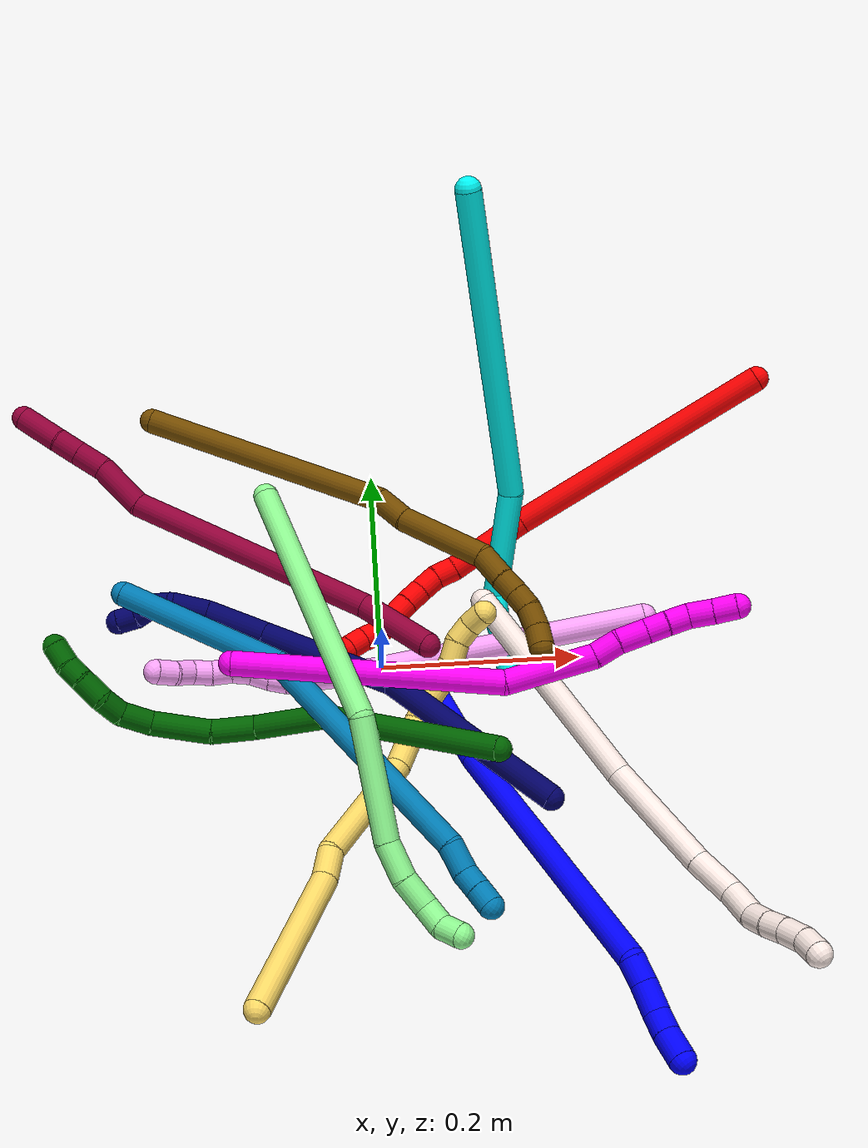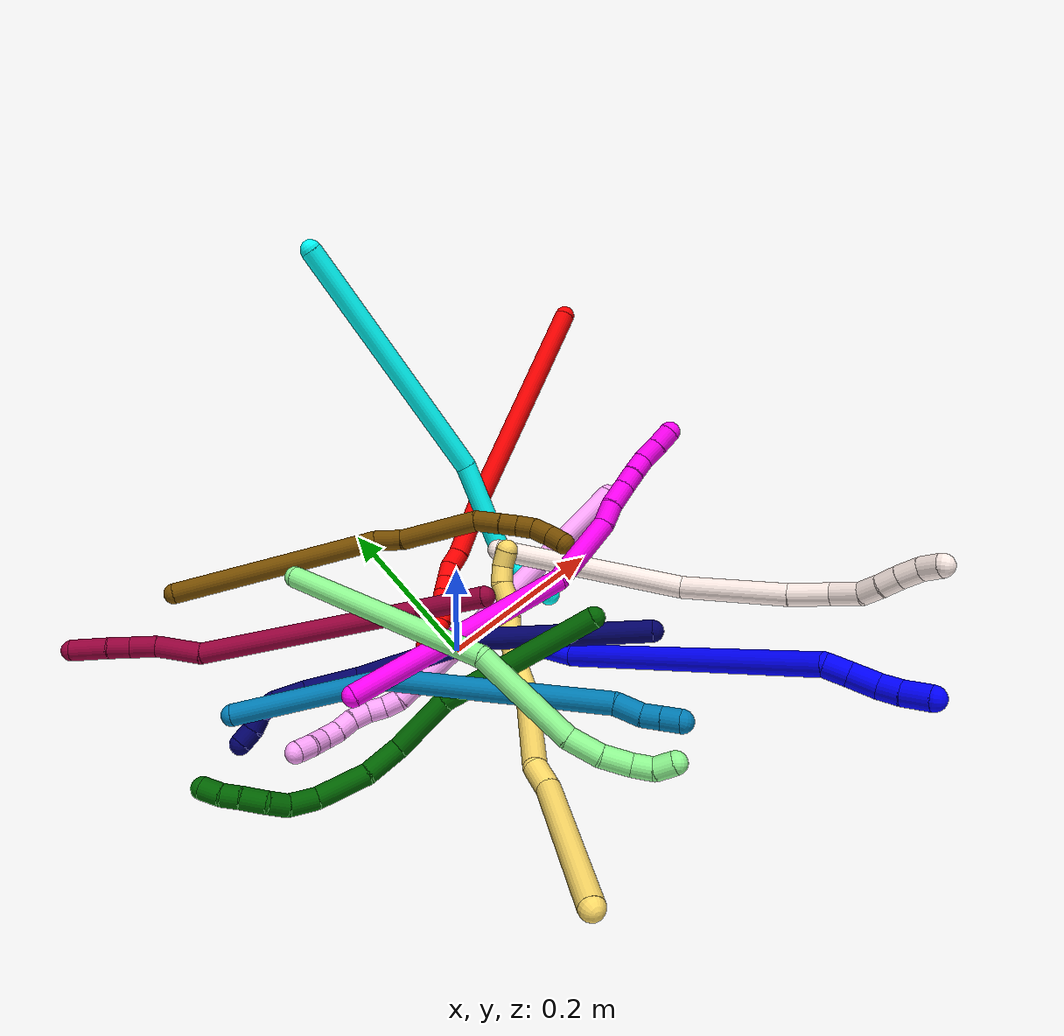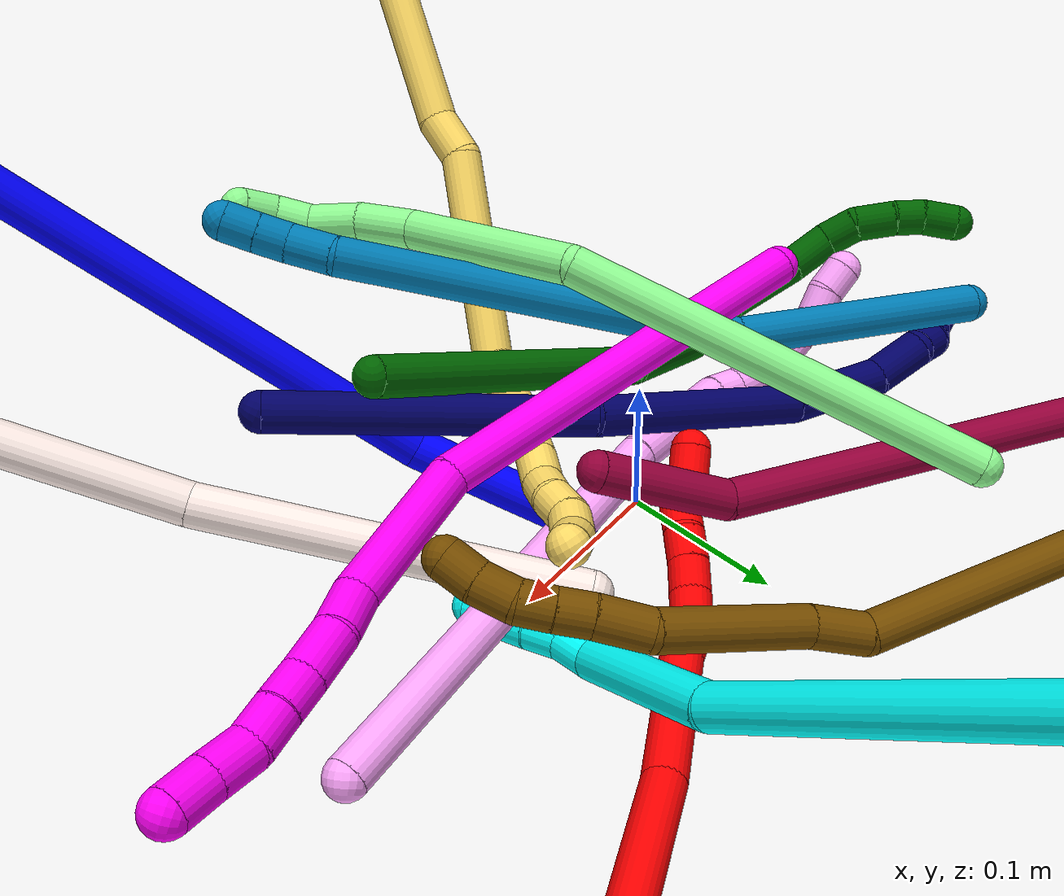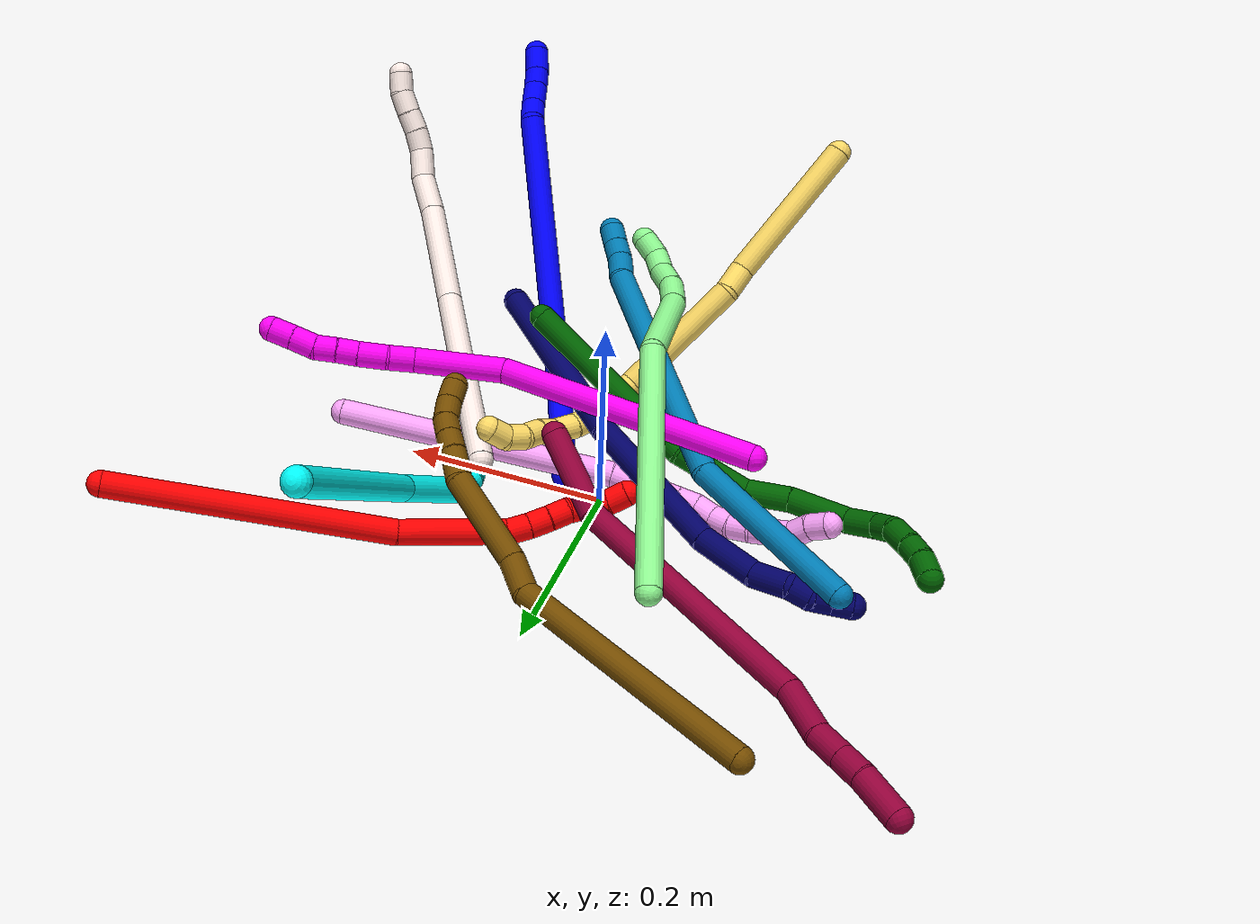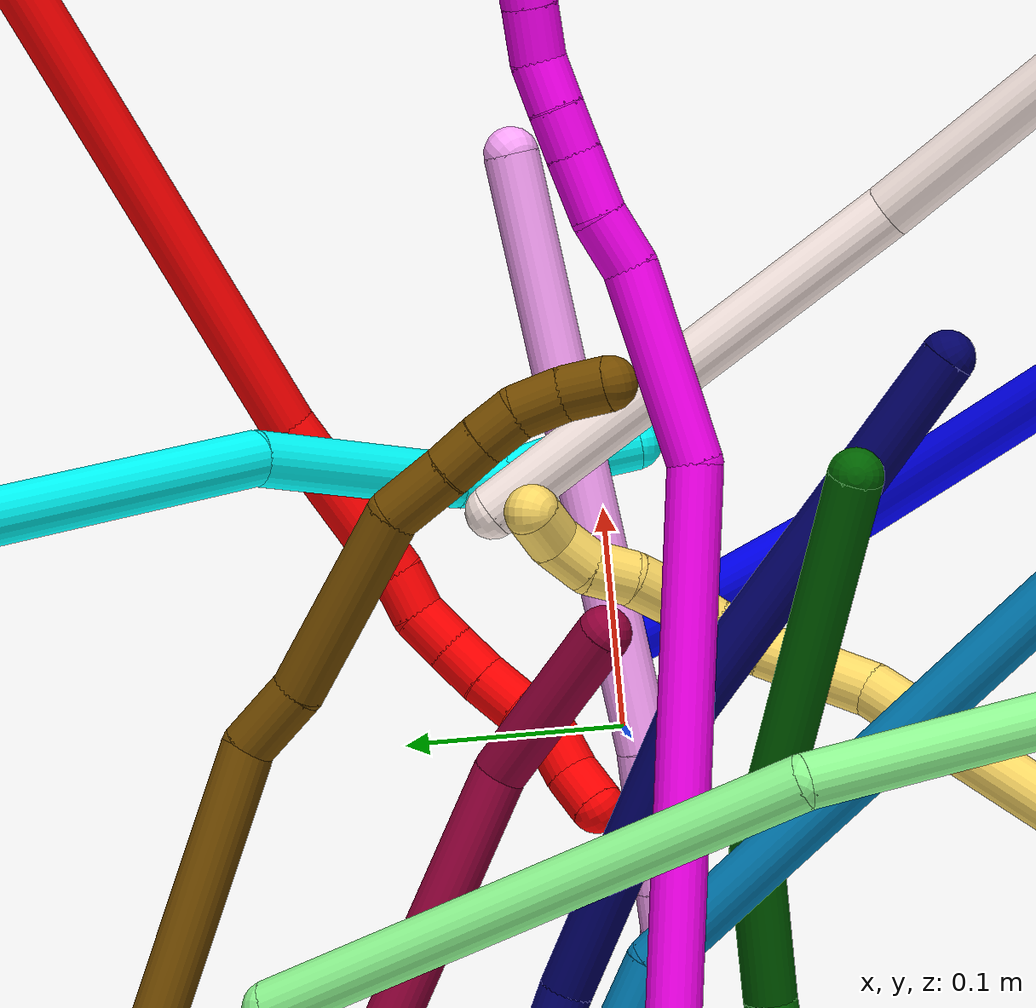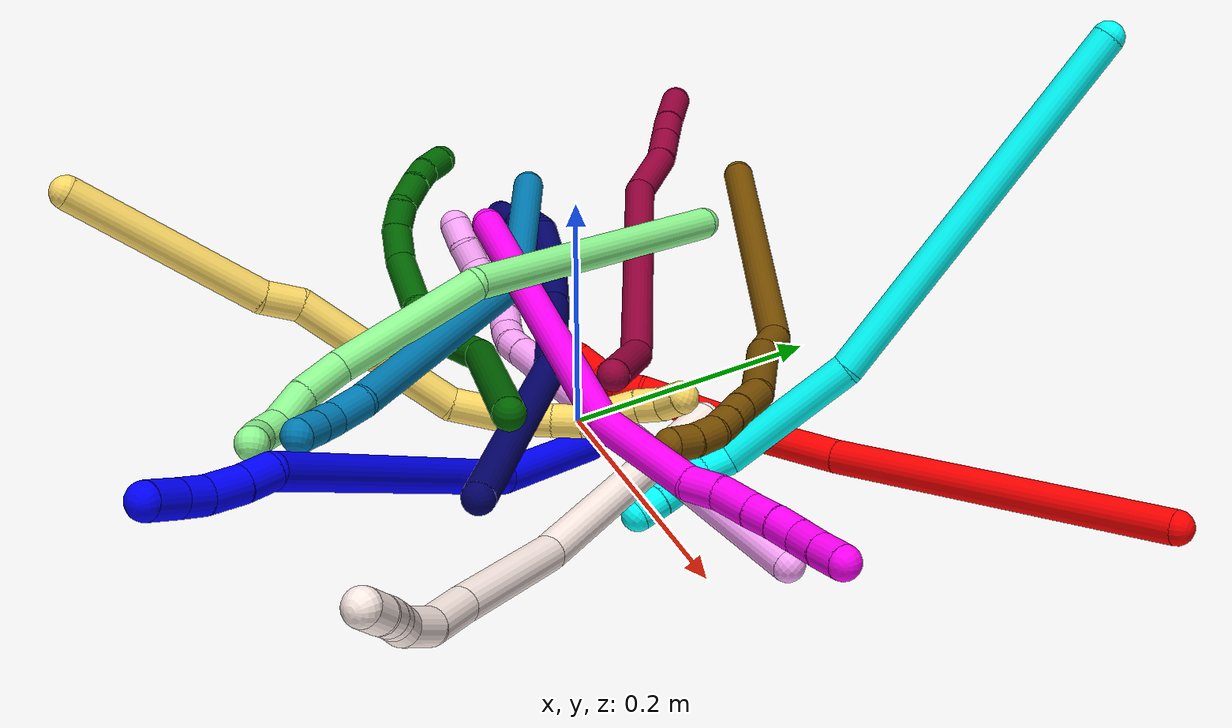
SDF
<sdf version="1.7">
 <world name="default">
  <plugin name="TubeGeneratorPlugin" filename="libtube_generator_plugin.so"/>
  <model name="photoneo_s_sensor">
   <static>1</static>
   <pose>0 0 2 1.57079 1.57079 3.14159</pose>
   <link name="link">
    <inertial><mass>0.1</mass></inertial>
    <sensor name="sensor" type="depth">
     <update_rate>30</update_rate>
     <camera>
      <horizontal_fov>1.22</horizontal_fov>
      <image><width>1920</width><height>1200</height><format>B8G8R8</format></image>
      <clip><near>0.1</near><far>4</far></clip>
      <depth_camera><output>points</output></depth_camera>
     </camera>
     <plugin name="camera_plugin" filename="libgazebo_ros_depth_camera.so">
      <baseline>0.2</baseline>
      <alwaysOn>1</alwaysOn>
      <updateRate>0.0</updateRate>
      <cameraName>camera_ir</cameraName>
      <imageTopicName>/camera/color/image_raw</imageTopicName>
      <cameraInfoTopicName>/camera/color/camera_info</cameraInfoTopicName>
      <depthImageTopicName>/camera/depth/image_raw</depthImageTopicName>
      <depthImageCameraInfoTopicName>/camera/depth/camera_info</depthImageCameraInfoTopicName>
      <pointCloudTopicName>/camera/depth/points</pointCloudTopicName>
      <frameName>fr_optical</frameName>
      <pointCloudCutoff>0.1</pointCloudCutoff>
      <pointCloudCutoffMax>2.0</pointCloudCutoffMax>
      <distortionK1>0</distortionK1>
      <distortionK2>0</distortionK2>
      <distortionK3>0</distortionK3>
      <distortionT1>0</distortionT1>
      <distortionT2>0</distortionT2>
      <CxPrime>0</CxPrime>
      <Cx>0</Cx>
      <Cy>0</Cy>
      <focalLength>0</focalLength>
      <hackBaseline>0</hackBaseline>
     </plugin>
    </sensor>
   </link>
  </model>
  <gravity>0 0 -9.8</gravity>
  <magnetic_field>6e-06 2.3e-05 -4.2e-05</magnetic_field>
  <atmosphere type="adiabatic"/>
  <physics name="default_physics" default="0" type="ode">
   <max_step_size>0.003</max_step_size>
   <real_time_factor>1</real_time_factor>
   <real_time_update_rate>1000</real_time_update_rate>
   <max_contacts>10000</max_contacts>
   <ode>
    <solver>
     <type>quick</type>
     <iters>100</iters>
     <sor>1.3</sor>
     <use_dynamic_moi_rescaling>0</use_dynamic_moi_rescaling>
    </solver>
    <constraints>
     <contact_max_correcting_vel>0</contact_max_correcting_vel>
     <contact_surface_layer>0.001</contact_surface_layer>
     <cfm>0</cfm>
     <erp>0.2</erp>
    </constraints>
   </ode>
  </physics>
  <scene><ambient>0.4 0.4 0.4 1</ambient><background>0.7 0.7 0.7 1</background><shadows>0</shadows></scene>
  <audio><device>default</device></audio>
  <spherical_coordinates>
   <surface_model>EARTH_WGS84</surface_model>
   <latitude_deg>0</latitude_deg>
   <longitude_deg>0</longitude_deg>
   <elevation>0</elevation>
   <heading_deg>0</heading_deg>
  </spherical_coordinates>
  <model name="bin">
   <static>1</static>
   <link name="bottom">
    <collision name="collision-bottom">
     <pose>0 0 -0.01 0 -0 0</pose>
     <geometry><box><size>0.8 0.6 0.02</size></box></geometry>
     <surface>
      <friction><ode><mu>100</mu><mu2>100</mu2></ode></friction>
      <contact><collide_bitmask>65535</collide_bitmask></contact>
     </surface>
    </collision>
   </link>
   <link name="west_wall">
    <collision name="collision-west_wall">
     <pose>-0.41 0 0.1 0 -0 0</pose>
     <geometry><box><size>0.02 0.6 0.2</size></box></geometry>
     <surface>
      <friction><ode><mu>100</mu><mu2>100</mu2></ode></friction>
      <contact><collide_bitmask>65535</collide_bitmask></contact>
     </surface>
    </collision>
   </link>
   <link name="east_wall">
    <collision name="collision-east_wall">
     <pose>0.41 0 0.1 0 -0 0</pose>
     <geometry><box><size>0.02 0.6 0.2</size></box></geometry>
     <surface>
      <friction><ode><mu>100</mu><mu2>100</mu2></ode></friction>
      <contact><collide_bitmask>65535</collide_bitmask></contact>
     </surface>
    </collision>
   </link>
   <link name="south_wall">
    <collision name="collision-south_wall">
     <pose>0 -0.31 0.1 0 -0 0</pose>
     <geometry><box><size>0.8 0.02 0.2</size></box></geometry>
     <surface>
      <friction><ode><mu>100</mu><mu2>100</mu2></ode></friction>
      <contact><collide_bitmask>65535</collide_bitmask></contact>
     </surface>
    </collision>
   </link>
   <link name="north_wall">
    <collision name="collision-north_wall">
     <pose>0 0.31 0.1 0 -0 0</pose>
     <geometry><box><size>0.8 0.02 0.2</size></box></geometry>
     <surface>
      <friction><ode><mu>100</mu><mu2>100</mu2></ode></friction>
      <contact><collide_bitmask>65535</collide_bitmask></contact>
     </surface>
    </collision>
   </link>
  </model>
  <model name="1">
   <static>0</static>
   <link name="1">
    <collision name="collision-cylinder-e_1_1_4">
     <pose>0.005986 -0.002206 0.053922 0.040888 0.110465 0.002261</pose>
     <geometry><cylinder><radius>0.0125</radius><length>0.108597</length></cylinder></geometry>
     <surface>
      <friction><ode><mu>1.16</mu><mu2>1.16</mu2><slip1>0</slip1><slip2>0</slip2></ode></friction>
      <contact><ode><kp>1e+06</kp><kd>1</kd><max_vel>0</max_vel><min_depth>0.001</min_depth></ode></contact>
     </surface>
    </collision>
    <visual name="visual-cylinder-e_1_1_4">
     <pose>0.005986 -0.002206 0.053922 0.040888 0.110465 0.002261</pose>
     <geometry><cylinder><radius>0.0125</radius><length>0.108597</length></cylinder></geometry>
     <material><ambient>0 0 1 1</ambient></material>
    </visual>
    <collision name="collision-cylinder-e_2_4_5">
     <pose>0.009596 -0.049845 0.246526 0.316591 -0.016279 -0.002599</pose>
     <geometry><cylinder><radius>0.0125</radius><length>0.291907</length></cylinder></geometry>
     <surface>
      <friction><ode><mu>1.16</mu><mu2>1.16</mu2><slip1>0</slip1><slip2>0</slip2></ode></friction>
      <contact><ode><kp>1e+06</kp><kd>1</kd><max_vel>0</max_vel><min_depth>0.001</min_depth></ode></contact>
     </surface>
    </collision>
    <visual name="visual-cylinder-e_2_4_5">
     <pose>0.009596 -0.049845 0.246526 0.316591 -0.016279 -0.002599</pose>
     <geometry><cylinder><radius>0.0125</radius><length>0.291907</length></cylinder></geometry>
     <material><ambient>0 0 1 1</ambient></material>
    </visual>
    <collision name="collision-cylinder-e_3_5_6">
     <pose>0.009707 -0.094182 0.396862 -0.093811 0.209351 -0.009863</pose>
     <geometry><cylinder><radius>0.0125</radius><length>0.023935</length></cylinder></geometry>
     <surface>
      <friction><ode><mu>1.16</mu><mu2>1.16</mu2><slip1>0</slip1><slip2>0</slip2></ode></friction>
      <contact><ode><kp>1e+06</kp><kd>1</kd><max_vel>0</max_vel><min_depth>0.001</min_depth></ode></contact>
     </surface>
    </collision>
    <visual name="visual-cylinder-e_3_5_6">
     <pose>0.009707 -0.094182 0.396862 -0.093811 0.209351 -0.009863</pose>
     <geometry><cylinder><radius>0.0125</radius><length>0.023935</length></cylinder></geometry>
     <material><ambient>0 0 1 1</ambient></material>
    </visual>
    <collision name="collision-cylinder-e_4_6_7">
     <pose>0.015733 -0.093077 0.422164 -0.000616 0.253696 -7.9e-05</pose>
     <geometry><cylinder><radius>0.0125</radius><length>0.028196</length></cylinder></geometry>
     <surface>
      <friction><ode><mu>1.16</mu><mu2>1.16</mu2><slip1>0</slip1><slip2>0</slip2></ode></friction>
      <contact><ode><kp>1e+06</kp><kd>1</kd><max_vel>0</max_vel><min_depth>0.001</min_depth></ode></contact>
     </surface>
    </collision>
    <visual name="visual-cylinder-e_4_6_7">
     <pose>0.015733 -0.093077 0.422164 -0.000616 0.253696 -7.9e-05</pose>
     <geometry><cylinder><radius>0.0125</radius><length>0.028196</length></cylinder></geometry>
     <material><ambient>0 0 1 1</ambient></material>
    </visual>
    <collision name="collision-cylinder-e_5_7_8">
     <pose>0.021267 -0.094911 0.445788 0.182526 0.194239 0.017832</pose>
     <geometry><cylinder><radius>0.0125</radius><length>0.020681</length></cylinder></geometry>
     <surface>
      <friction><ode><mu>1.16</mu><mu2>1.16</mu2><slip1>0</slip1><slip2>0</slip2></ode></friction>
      <contact><ode><kp>1e+06</kp><kd>1</kd><max_vel>0</max_vel><min_depth>0.001</min_depth></ode></contact>
     </surface>
    </collision>
    <visual name="visual-cylinder-e_5_7_8">
     <pose>0.021267 -0.094911 0.445788 0.182526 0.194239 0.017832</pose>
     <geometry><cylinder><radius>0.0125</radius><length>0.020681</length></cylinder></geometry>
     <material><ambient>0 0 1 1</ambient></material>
    </visual>
    <collision name="collision-cylinder-e_6_8_2">
     <pose>0.024396 -0.09988 0.468686 0.237503 0.085056 0.010154</pose>
     <geometry><cylinder><radius>0.0125</radius><length>0.026685</length></cylinder></geometry>
     <surface>
      <friction><ode><mu>1.16</mu><mu2>1.16</mu2><slip1>0</slip1><slip2>0</slip2></ode></friction>
      <contact><ode><kp>1e+06</kp><kd>1</kd><max_vel>0</max_vel><min_depth>0.001</min_depth></ode></contact>
     </surface>
    </collision>
    <visual name="visual-cylinder-e_6_8_2">
     <pose>0.024396 -0.09988 0.468686 0.237503 0.085056 0.010154</pose>
     <geometry><cylinder><radius>0.0125</radius><length>0.026685</length></cylinder></geometry>
     <material><ambient>0 0 1 1</ambient></material>
    </visual>
    <collision name="collision-sphere-2">
     <pose>0.02553 -0.103008 0.481607 0 -0 0</pose>
     <geometry><sphere><radius>0.0125</radius></sphere></geometry>
     <surface>
      <friction><ode><mu>1.16</mu><mu2>1.16</mu2><slip1>0</slip1><slip2>0</slip2></ode></friction>
      <contact><ode><kp>1e+06</kp><kd>1</kd><max_vel>0</max_vel><min_depth>0.001</min_depth></ode></contact>
     </surface>
    </collision>
    <visual name="visual-sphere-2">
     <pose>0.02553 -0.103008 0.481607 0 -0 0</pose>
     <geometry><sphere><radius>0.0125</radius></sphere></geometry>
     <material><ambient>0 0 1 1</ambient></material>
    </visual>
    <collision name="collision-sphere-4">
     <pose>0.011972 -0.004412 0.107845 0 -0 0</pose>
     <geometry><sphere><radius>0.0125</radius></sphere></geometry>
     <surface>
      <friction><ode><mu>1.16</mu><mu2>1.16</mu2><slip1>0</slip1><slip2>0</slip2></ode></friction>
      <contact><ode><kp>1e+06</kp><kd>1</kd><max_vel>0</max_vel><min_depth>0.001</min_depth></ode></contact>
     </surface>
    </collision>
    <visual name="visual-sphere-4">
     <pose>0.011972 -0.004412 0.107845 0 -0 0</pose>
     <geometry><sphere><radius>0.0125</radius></sphere></geometry>
     <material><ambient>0 0 1 1</ambient></material>
    </visual>
    <collision name="collision-sphere-1">
     <geometry><sphere><radius>0.0125</radius></sphere></geometry>
     <surface>
      <friction><ode><mu>1.16</mu><mu2>1.16</mu2><slip1>0</slip1><slip2>0</slip2></ode></friction>
      <contact><ode><kp>1e+06</kp><kd>1</kd><max_vel>0</max_vel><min_depth>0.001</min_depth></ode></contact>
     </surface>
    </collision>
    <visual name="visual-sphere-1">
     <geometry><sphere><radius>0.0125</radius></sphere></geometry>
     <material><ambient>0 0 1 1</ambient></material>
    </visual>
    <collision name="collision-sphere-8">
     <pose>0.023263 -0.096752 0.455765 0 -0 0</pose>
     <geometry><sphere><radius>0.0125</radius></sphere></geometry>
     <surface>
      <friction><ode><mu>1.16</mu><mu2>1.16</mu2><slip1>0</slip1><slip2>0</slip2></ode></friction>
      <contact><ode><kp>1e+06</kp><kd>1</kd><max_vel>0</max_vel><min_depth>0.001</min_depth></ode></contact>
     </surface>
    </collision>
    <visual name="visual-sphere-8">
     <pose>0.023263 -0.096752 0.455765 0 -0 0</pose>
     <geometry><sphere><radius>0.0125</radius></sphere></geometry>
     <material><ambient>0 0 1 1</ambient></material>
    </visual>
    <collision name="collision-sphere-5">
     <pose>0.00722 -0.095279 0.385207 0 -0 0</pose>
     <geometry><sphere><radius>0.0125</radius></sphere></geometry>
     <surface>
      <friction><ode><mu>1.16</mu><mu2>1.16</mu2><slip1>0</slip1><slip2>0</slip2></ode></friction>
      <contact><ode><kp>1e+06</kp><kd>1</kd><max_vel>0</max_vel><min_depth>0.001</min_depth></ode></contact>
     </surface>
    </collision>
    <visual name="visual-sphere-5">
     <pose>0.00722 -0.095279 0.385207 0 -0 0</pose>
     <geometry><sphere><radius>0.0125</radius></sphere></geometry>
     <material><ambient>0 0 1 1</ambient></material>
    </visual>
    <collision name="collision-sphere-6">
     <pose>0.012194 -0.093086 0.408517 0 -0 0</pose>
     <geometry><sphere><radius>0.0125</radius></sphere></geometry>
     <surface>
      <friction><ode><mu>1.16</mu><mu2>1.16</mu2><slip1>0</slip1><slip2>0</slip2></ode></friction>
      <contact><ode><kp>1e+06</kp><kd>1</kd><max_vel>0</max_vel><min_depth>0.001</min_depth></ode></contact>
     </surface>
    </collision>
    <visual name="visual-sphere-6">
     <pose>0.012194 -0.093086 0.408517 0 -0 0</pose>
     <geometry><sphere><radius>0.0125</radius></sphere></geometry>
     <material><ambient>0 0 1 1</ambient></material>
    </visual>
    <collision name="collision-sphere-7">
     <pose>0.019271 -0.093069 0.435811 0 -0 0</pose>
     <geometry><sphere><radius>0.0125</radius></sphere></geometry>
     <surface>
      <friction><ode><mu>1.16</mu><mu2>1.16</mu2><slip1>0</slip1><slip2>0</slip2></ode></friction>
      <contact><ode><kp>1e+06</kp><kd>1</kd><max_vel>0</max_vel><min_depth>0.001</min_depth></ode></contact>
     </surface>
    </collision>
    <visual name="visual-sphere-7">
     <pose>0.019271 -0.093069 0.435811 0 -0 0</pose>
     <geometry><sphere><radius>0.0125</radius></sphere></geometry>
     <material><ambient>0 0 1 1</ambient></material>
    </visual>
    <inertial>
     <pose>0.010436 -0.048593 0.241893 0 -0 0</pose>
     <mass>0.5</mass>
     <inertia><ixx>0.0022</ixx><ixy>0</ixy><ixz>0</ixz><iyy>0.002087</iyy><iyz>0</iyz><izz>0.000712</izz></inertia>
    </inertial>
   </link>
   <pose>0.04151 -0.010951 0.011478 -1.24228 0.156935 -2.53498</pose>
  </model>
  <model name="2">
   <static>0</static>
   <link name="2">
    <collision name="collision-cylinder-e_1_1_4">
     <pose>0.000146 -7.5e-05 -0.136751 3.14105 0.001065 2.19373</pose>
     <geometry><cylinder><radius>0.0125</radius><length>0.273503</length></cylinder></geometry>
     <surface>
      <friction><ode><mu>1.16</mu><mu2>1.16</mu2><slip1>0</slip1><slip2>0</slip2></ode></friction>
      <contact><ode><kp>1e+06</kp><kd>1</kd><max_vel>0</max_vel><min_depth>0.001</min_depth></ode></contact>
     </surface>
    </collision>
    <visual name="visual-cylinder-e_1_1_4">
     <pose>0.000146 -7.5e-05 -0.136751 3.14105 0.001065 2.19373</pose>
     <geometry><cylinder><radius>0.0125</radius><length>0.273503</length></cylinder></geometry>
     <material><ambient>1 0 0 1</ambient></material>
    </visual>
    <collision name="collision-cylinder-e_2_4_5">
     <pose>-0.00496 -0.004919 -0.314505 3.02578 -0.126531 -1.65943</pose>
     <geometry><cylinder><radius>0.0125</radius><length>0.083223</length></cylinder></geometry>
     <surface>
      <friction><ode><mu>1.16</mu><mu2>1.16</mu2><slip1>0</slip1><slip2>0</slip2></ode></friction>
      <contact><ode><kp>1e+06</kp><kd>1</kd><max_vel>0</max_vel><min_depth>0.001</min_depth></ode></contact>
     </surface>
    </collision>
    <visual name="visual-cylinder-e_2_4_5">
     <pose>-0.00496 -0.004919 -0.314505 3.02578 -0.126531 -1.65943</pose>
     <geometry><cylinder><radius>0.0125</radius><length>0.083223</length></cylinder></geometry>
     <material><ambient>1 0 0 1</ambient></material>
    </visual>
    <collision name="collision-cylinder-e_3_5_6">
     <pose>-0.012813 -0.009418 -0.365787 -3.11526 -0.247831 2.93097</pose>
     <geometry><cylinder><radius>0.0125</radius><length>0.021214</length></cylinder></geometry>
     <surface>
      <friction><ode><mu>1.16</mu><mu2>1.16</mu2><slip1>0</slip1><slip2>0</slip2></ode></friction>
      <contact><ode><kp>1e+06</kp><kd>1</kd><max_vel>0</max_vel><min_depth>0.001</min_depth></ode></contact>
     </surface>
    </collision>
    <visual name="visual-cylinder-e_3_5_6">
     <pose>-0.012813 -0.009418 -0.365787 -3.11526 -0.247831 2.93097</pose>
     <geometry><cylinder><radius>0.0125</radius><length>0.021214</length></cylinder></geometry>
     <material><ambient>1 0 0 1</ambient></material>
    </visual>
    <collision name="collision-cylinder-e_4_6_7">
     <pose>-0.018673 -0.012293 -0.38583 2.82997 -0.307532 -1.55737</pose>
     <geometry><cylinder><radius>0.0125</radius><length>0.021525</length></cylinder></geometry>
     <surface>
      <friction><ode><mu>1.16</mu><mu2>1.16</mu2><slip1>0</slip1><slip2>0</slip2></ode></friction>
      <contact><ode><kp>1e+06</kp><kd>1</kd><max_vel>0</max_vel><min_depth>0.001</min_depth></ode></contact>
     </surface>
    </collision>
    <visual name="visual-cylinder-e_4_6_7">
     <pose>-0.018673 -0.012293 -0.38583 2.82997 -0.307532 -1.55737</pose>
     <geometry><cylinder><radius>0.0125</radius><length>0.021525</length></cylinder></geometry>
     <material><ambient>1 0 0 1</ambient></material>
    </visual>
    <collision name="collision-cylinder-e_5_7_8">
     <pose>-0.025749 -0.018811 -0.40445 2.77768 -0.383024 -1.62316</pose>
     <geometry><cylinder><radius>0.0125</radius><length>0.020435</length></cylinder></geometry>
     <surface>
      <friction><ode><mu>1.16</mu><mu2>1.16</mu2><slip1>0</slip1><slip2>0</slip2></ode></friction>
      <contact><ode><kp>1e+06</kp><kd>1</kd><max_vel>0</max_vel><min_depth>0.001</min_depth></ode></contact>
     </surface>
    </collision>
    <visual name="visual-cylinder-e_5_7_8">
     <pose>-0.025749 -0.018811 -0.40445 2.77768 -0.383024 -1.62316</pose>
     <geometry><cylinder><radius>0.0125</radius><length>0.020435</length></cylinder></geometry>
     <material><ambient>1 0 0 1</ambient></material>
    </visual>
    <collision name="collision-cylinder-e_6_8_9">
     <pose>-0.033024 -0.026185 -0.421846 2.70343 -0.351336 -1.34605</pose>
     <geometry><cylinder><radius>0.0125</radius><length>0.020089</length></cylinder></geometry>
     <surface>
      <friction><ode><mu>1.16</mu><mu2>1.16</mu2><slip1>0</slip1><slip2>0</slip2></ode></friction>
      <contact><ode><kp>1e+06</kp><kd>1</kd><max_vel>0</max_vel><min_depth>0.001</min_depth></ode></contact>
     </surface>
    </collision>
    <visual name="visual-cylinder-e_6_8_9">
     <pose>-0.033024 -0.026185 -0.421846 2.70343 -0.351336 -1.34605</pose>
     <geometry><cylinder><radius>0.0125</radius><length>0.020089</length></cylinder></geometry>
     <material><ambient>1 0 0 1</ambient></material>
    </visual>
    <collision name="collision-cylinder-e_7_9_10">
     <pose>-0.038015 -0.033724 -0.439614 2.77554 -0.153956 -0.789644</pose>
     <geometry><cylinder><radius>0.0125</radius><length>0.020003</length></cylinder></geometry>
     <surface>
      <friction><ode><mu>1.16</mu><mu2>1.16</mu2><slip1>0</slip1><slip2>0</slip2></ode></friction>
      <contact><ode><kp>1e+06</kp><kd>1</kd><max_vel>0</max_vel><min_depth>0.001</min_depth></ode></contact>
     </surface>
    </collision>
    <visual name="visual-cylinder-e_7_9_10">
     <pose>-0.038015 -0.033724 -0.439614 2.77554 -0.153956 -0.789644</pose>
     <geometry><cylinder><radius>0.0125</radius><length>0.020003</length></cylinder></geometry>
     <material><ambient>1 0 0 1</ambient></material>
    </visual>
    <collision name="collision-cylinder-e_8_10_11">
     <pose>-0.044055 -0.037624 -0.457766 3.10104 -0.467371 -2.97161</pose>
     <geometry><cylinder><radius>0.0125</radius><length>0.020006</length></cylinder></geometry>
     <surface>
      <friction><ode><mu>1.16</mu><mu2>1.16</mu2><slip1>0</slip1><slip2>0</slip2></ode></friction>
      <contact><ode><kp>1e+06</kp><kd>1</kd><max_vel>0</max_vel><min_depth>0.001</min_depth></ode></contact>
     </surface>
    </collision>
    <visual name="visual-cylinder-e_8_10_11">
     <pose>-0.044055 -0.037624 -0.457766 3.10104 -0.467371 -2.97161</pose>
     <geometry><cylinder><radius>0.0125</radius><length>0.020006</length></cylinder></geometry>
     <material><ambient>1 0 0 1</ambient></material>
    </visual>
    <collision name="collision-cylinder-e_9_11_2">
     <pose>-0.054673 -0.040168 -0.474299 2.86232 -0.657337 -2.35976</pose>
     <geometry><cylinder><radius>0.0125</radius><length>0.020002</length></cylinder></geometry>
     <surface>
      <friction><ode><mu>1.16</mu><mu2>1.16</mu2><slip1>0</slip1><slip2>0</slip2></ode></friction>
      <contact><ode><kp>1e+06</kp><kd>1</kd><max_vel>0</max_vel><min_depth>0.001</min_depth></ode></contact>
     </surface>
    </collision>
    <visual name="visual-cylinder-e_9_11_2">
     <pose>-0.054673 -0.040168 -0.474299 2.86232 -0.657337 -2.35976</pose>
     <geometry><cylinder><radius>0.0125</radius><length>0.020002</length></cylinder></geometry>
     <material><ambient>1 0 0 1</ambient></material>
    </visual>
    <collision name="collision-sphere-2">
     <pose>-0.060784 -0.04235 -0.481909 0 -0 0</pose>
     <geometry><sphere><radius>0.0125</radius></sphere></geometry>
     <surface>
      <friction><ode><mu>1.16</mu><mu2>1.16</mu2><slip1>0</slip1><slip2>0</slip2></ode></friction>
      <contact><ode><kp>1e+06</kp><kd>1</kd><max_vel>0</max_vel><min_depth>0.001</min_depth></ode></contact>
     </surface>
    </collision>
    <visual name="visual-sphere-2">
     <pose>-0.060784 -0.04235 -0.481909 0 -0 0</pose>
     <geometry><sphere><radius>0.0125</radius></sphere></geometry>
     <material><ambient>1 0 0 1</ambient></material>
    </visual>
    <collision name="collision-sphere-11">
     <pose>-0.048562 -0.037986 -0.466689 0 -0 0</pose>
     <geometry><sphere><radius>0.0125</radius></sphere></geometry>
     <surface>
      <friction><ode><mu>1.16</mu><mu2>1.16</mu2><slip1>0</slip1><slip2>0</slip2></ode></friction>
      <contact><ode><kp>1e+06</kp><kd>1</kd><max_vel>0</max_vel><min_depth>0.001</min_depth></ode></contact>
     </surface>
    </collision>
    <visual name="visual-sphere-11">
     <pose>-0.048562 -0.037986 -0.466689 0 -0 0</pose>
     <geometry><sphere><radius>0.0125</radius></sphere></geometry>
     <material><ambient>1 0 0 1</ambient></material>
    </visual>
    <collision name="collision-sphere-10">
     <pose>-0.039549 -0.037261 -0.448843 0 -0 0</pose>
     <geometry><sphere><radius>0.0125</radius></sphere></geometry>
     <surface>
      <friction><ode><mu>1.16</mu><mu2>1.16</mu2><slip1>0</slip1><slip2>0</slip2></ode></friction>
      <contact><ode><kp>1e+06</kp><kd>1</kd><max_vel>0</max_vel><min_depth>0.001</min_depth></ode></contact>
     </surface>
    </collision>
    <visual name="visual-sphere-10">
     <pose>-0.039549 -0.037261 -0.448843 0 -0 0</pose>
     <geometry><sphere><radius>0.0125</radius></sphere></geometry>
     <material><ambient>1 0 0 1</ambient></material>
    </visual>
    <collision name="collision-sphere-9">
     <pose>-0.036481 -0.030186 -0.430386 0 -0 0</pose>
     <geometry><sphere><radius>0.0125</radius></sphere></geometry>
     <surface>
      <friction><ode><mu>1.16</mu><mu2>1.16</mu2><slip1>0</slip1><slip2>0</slip2></ode></friction>
      <contact><ode><kp>1e+06</kp><kd>1</kd><max_vel>0</max_vel><min_depth>0.001</min_depth></ode></contact>
     </surface>
    </collision>
    <visual name="visual-sphere-9">
     <pose>-0.036481 -0.030186 -0.430386 0 -0 0</pose>
     <geometry><sphere><radius>0.0125</radius></sphere></geometry>
     <material><ambient>1 0 0 1</ambient></material>
    </visual>
    <collision name="collision-sphere-4">
     <pose>0.000291 -0.000149 -0.273503 0 -0 0</pose>
     <geometry><sphere><radius>0.0125</radius></sphere></geometry>
     <surface>
      <friction><ode><mu>1.16</mu><mu2>1.16</mu2><slip1>0</slip1><slip2>0</slip2></ode></friction>
      <contact><ode><kp>1e+06</kp><kd>1</kd><max_vel>0</max_vel><min_depth>0.001</min_depth></ode></contact>
     </surface>
    </collision>
    <visual name="visual-sphere-4">
     <pose>0.000291 -0.000149 -0.273503 0 -0 0</pose>
     <geometry><sphere><radius>0.0125</radius></sphere></geometry>
     <material><ambient>1 0 0 1</ambient></material>
    </visual>
    <collision name="collision-sphere-1">
     <geometry><sphere><radius>0.0125</radius></sphere></geometry>
     <surface>
      <friction><ode><mu>1.16</mu><mu2>1.16</mu2><slip1>0</slip1><slip2>0</slip2></ode></friction>
      <contact><ode><kp>1e+06</kp><kd>1</kd><max_vel>0</max_vel><min_depth>0.001</min_depth></ode></contact>
     </surface>
    </collision>
    <visual name="visual-sphere-1">
     <geometry><sphere><radius>0.0125</radius></sphere></geometry>
     <material><ambient>1 0 0 1</ambient></material>
    </visual>
    <collision name="collision-sphere-8">
     <pose>-0.029568 -0.022184 -0.413306 0 -0 0</pose>
     <geometry><sphere><radius>0.0125</radius></sphere></geometry>
     <surface>
      <friction><ode><mu>1.16</mu><mu2>1.16</mu2><slip1>0</slip1><slip2>0</slip2></ode></friction>
      <contact><ode><kp>1e+06</kp><kd>1</kd><max_vel>0</max_vel><min_depth>0.001</min_depth></ode></contact>
     </surface>
    </collision>
    <visual name="visual-sphere-8">
     <pose>-0.029568 -0.022184 -0.413306 0 -0 0</pose>
     <geometry><sphere><radius>0.0125</radius></sphere></geometry>
     <material><ambient>1 0 0 1</ambient></material>
    </visual>
    <collision name="collision-sphere-5">
     <pose>-0.010211 -0.009689 -0.355508 0 -0 0</pose>
     <geometry><sphere><radius>0.0125</radius></sphere></geometry>
     <surface>
      <friction><ode><mu>1.16</mu><mu2>1.16</mu2><slip1>0</slip1><slip2>0</slip2></ode></friction>
      <contact><ode><kp>1e+06</kp><kd>1</kd><max_vel>0</max_vel><min_depth>0.001</min_depth></ode></contact>
     </surface>
    </collision>
    <visual name="visual-sphere-5">
     <pose>-0.010211 -0.009689 -0.355508 0 -0 0</pose>
     <geometry><sphere><radius>0.0125</radius></sphere></geometry>
     <material><ambient>1 0 0 1</ambient></material>
    </visual>
    <collision name="collision-sphere-6">
     <pose>-0.015415 -0.009148 -0.376066 0 -0 0</pose>
     <geometry><sphere><radius>0.0125</radius></sphere></geometry>
     <surface>
      <friction><ode><mu>1.16</mu><mu2>1.16</mu2><slip1>0</slip1><slip2>0</slip2></ode></friction>
      <contact><ode><kp>1e+06</kp><kd>1</kd><max_vel>0</max_vel><min_depth>0.001</min_depth></ode></contact>
     </surface>
    </collision>
    <visual name="visual-sphere-6">
     <pose>-0.015415 -0.009148 -0.376066 0 -0 0</pose>
     <geometry><sphere><radius>0.0125</radius></sphere></geometry>
     <material><ambient>1 0 0 1</ambient></material>
    </visual>
    <collision name="collision-sphere-7">
     <pose>-0.021931 -0.015438 -0.395593 0 -0 0</pose>
     <geometry><sphere><radius>0.0125</radius></sphere></geometry>
     <surface>
      <friction><ode><mu>1.16</mu><mu2>1.16</mu2><slip1>0</slip1><slip2>0</slip2></ode></friction>
      <contact><ode><kp>1e+06</kp><kd>1</kd><max_vel>0</max_vel><min_depth>0.001</min_depth></ode></contact>
     </surface>
    </collision>
    <visual name="visual-sphere-7">
     <pose>-0.021931 -0.015438 -0.395593 0 -0 0</pose>
     <geometry><sphere><radius>0.0125</radius></sphere></geometry>
     <material><ambient>1 0 0 1</ambient></material>
    </visual>
    <inertial>
     <pose>-0.009943 -0.008071 -0.247638 0 -0 0</pose>
     <mass>0.5</mass>
     <inertia><ixx>0.000324</ixx><ixy>0</ixy><ixz>0</ixz><iyy>0.002343</iyy><iyz>0</iyz><izz>-2e-05</izz></inertia>
    </inertial>
   </link>
   <pose>0.388406 0.254164 0.091844 -0.560455 1.26297 -0.133069</pose>
  </model>
  <model name="3">
   <static>0</static>
   <link name="3">
    <collision name="collision-cylinder-e_1_1_4">
     <pose>0.005842 -0.005156 -0.153022 3.10791 0.038135 1.69474</pose>
     <geometry><cylinder><radius>0.0125</radius><length>0.306441</length></cylinder></geometry>
     <surface>
      <friction><ode><mu>1.16</mu><mu2>1.16</mu2><slip1>0</slip1><slip2>0</slip2></ode></friction>
      <contact><ode><kp>1e+06</kp><kd>1</kd><max_vel>0</max_vel><min_depth>0.001</min_depth></ode></contact>
     </surface>
    </collision>
    <visual name="visual-cylinder-e_1_1_4">
     <pose>0.005842 -0.005156 -0.153022 3.10791 0.038135 1.69474</pose>
     <geometry><cylinder><radius>0.0125</radius><length>0.306441</length></cylinder></geometry>
     <material><ambient>0.003922 1 0.996078 1</ambient></material>
    </visual>
    <collision name="collision-cylinder-e_2_4_5">
     <pose>-0.00027 -0.018491 -0.358908 2.98808 -0.219838 -1.92439</pose>
     <geometry><cylinder><radius>0.0125</radius><length>0.109623</length></cylinder></geometry>
     <surface>
      <friction><ode><mu>1.16</mu><mu2>1.16</mu2><slip1>0</slip1><slip2>0</slip2></ode></friction>
      <contact><ode><kp>1e+06</kp><kd>1</kd><max_vel>0</max_vel><min_depth>0.001</min_depth></ode></contact>
     </surface>
    </collision>
    <visual name="visual-cylinder-e_2_4_5">
     <pose>-0.00027 -0.018491 -0.358908 2.98808 -0.219838 -1.92439</pose>
     <geometry><cylinder><radius>0.0125</radius><length>0.109623</length></cylinder></geometry>
     <material><ambient>0.003922 1 0.996078 1</ambient></material>
    </visual>
    <collision name="collision-cylinder-e_3_5_6">
     <pose>-0.012301 -0.033067 -0.421066 2.53882 -0.006981 -0.022457</pose>
     <geometry><cylinder><radius>0.0125</radius><length>0.022566</length></cylinder></geometry>
     <surface>
      <friction><ode><mu>1.16</mu><mu2>1.16</mu2><slip1>0</slip1><slip2>0</slip2></ode></friction>
      <contact><ode><kp>1e+06</kp><kd>1</kd><max_vel>0</max_vel><min_depth>0.001</min_depth></ode></contact>
     </surface>
    </collision>
    <visual name="visual-cylinder-e_3_5_6">
     <pose>-0.012301 -0.033067 -0.421066 2.53882 -0.006981 -0.022457</pose>
     <geometry><cylinder><radius>0.0125</radius><length>0.022566</length></cylinder></geometry>
     <material><ambient>0.003922 1 0.996078 1</ambient></material>
    </visual>
    <collision name="collision-cylinder-e_4_6_7">
     <pose>-0.009618 -0.044771 -0.43881 2.58076 0.270042 0.881476</pose>
     <geometry><cylinder><radius>0.0125</radius><length>0.020708</length></cylinder></geometry>
     <surface>
      <friction><ode><mu>1.16</mu><mu2>1.16</mu2><slip1>0</slip1><slip2>0</slip2></ode></friction>
      <contact><ode><kp>1e+06</kp><kd>1</kd><max_vel>0</max_vel><min_depth>0.001</min_depth></ode></contact>
     </surface>
    </collision>
    <visual name="visual-cylinder-e_4_6_7">
     <pose>-0.009618 -0.044771 -0.43881 2.58076 0.270042 0.881476</pose>
     <geometry><cylinder><radius>0.0125</radius><length>0.020708</length></cylinder></geometry>
     <material><ambient>0.003922 1 0.996078 1</ambient></material>
    </visual>
    <collision name="collision-cylinder-e_5_7_8">
     <pose>-0.004945 -0.05504 -0.455928 2.62169 0.189044 0.684815</pose>
     <geometry><cylinder><radius>0.0125</radius><length>0.020337</length></cylinder></geometry>
     <surface>
      <friction><ode><mu>1.16</mu><mu2>1.16</mu2><slip1>0</slip1><slip2>0</slip2></ode></friction>
      <contact><ode><kp>1e+06</kp><kd>1</kd><max_vel>0</max_vel><min_depth>0.001</min_depth></ode></contact>
     </surface>
    </collision>
    <visual name="visual-cylinder-e_5_7_8">
     <pose>-0.004945 -0.05504 -0.455928 2.62169 0.189044 0.684815</pose>
     <geometry><cylinder><radius>0.0125</radius><length>0.020337</length></cylinder></geometry>
     <material><ambient>0.003922 1 0.996078 1</ambient></material>
    </visual>
    <collision name="collision-cylinder-e_6_8_2">
     <pose>-0.001546 -0.065089 -0.473267 2.61105 0.1469 0.529006</pose>
     <geometry><cylinder><radius>0.0125</radius><length>0.020324</length></cylinder></geometry>
     <surface>
      <friction><ode><mu>1.16</mu><mu2>1.16</mu2><slip1>0</slip1><slip2>0</slip2></ode></friction>
      <contact><ode><kp>1e+06</kp><kd>1</kd><max_vel>0</max_vel><min_depth>0.001</min_depth></ode></contact>
     </surface>
    </collision>
    <visual name="visual-cylinder-e_6_8_2">
     <pose>-0.001546 -0.065089 -0.473267 2.61105 0.1469 0.529006</pose>
     <geometry><cylinder><radius>0.0125</radius><length>0.020324</length></cylinder></geometry>
     <material><ambient>0.003922 1 0.996078 1</ambient></material>
    </visual>
    <collision name="collision-sphere-2">
     <pose>-5.9e-05 -0.070175 -0.481938 0 -0 0</pose>
     <geometry><sphere><radius>0.0125</radius></sphere></geometry>
     <surface>
      <friction><ode><mu>1.16</mu><mu2>1.16</mu2><slip1>0</slip1><slip2>0</slip2></ode></friction>
      <contact><ode><kp>1e+06</kp><kd>1</kd><max_vel>0</max_vel><min_depth>0.001</min_depth></ode></contact>
     </surface>
    </collision>
    <visual name="visual-sphere-2">
     <pose>-5.9e-05 -0.070175 -0.481938 0 -0 0</pose>
     <geometry><sphere><radius>0.0125</radius></sphere></geometry>
     <material><ambient>0.003922 1 0.996078 1</ambient></material>
    </visual>
    <collision name="collision-sphere-4">
     <pose>0.011683 -0.010311 -0.306045 0 -0 0</pose>
     <geometry><sphere><radius>0.0125</radius></sphere></geometry>
     <surface>
      <friction><ode><mu>1.16</mu><mu2>1.16</mu2><slip1>0</slip1><slip2>0</slip2></ode></friction>
      <contact><ode><kp>1e+06</kp><kd>1</kd><max_vel>0</max_vel><min_depth>0.001</min_depth></ode></contact>
     </surface>
    </collision>
    <visual name="visual-sphere-4">
     <pose>0.011683 -0.010311 -0.306045 0 -0 0</pose>
     <geometry><sphere><radius>0.0125</radius></sphere></geometry>
     <material><ambient>0.003922 1 0.996078 1</ambient></material>
    </visual>
    <collision name="collision-sphere-1">
     <geometry><sphere><radius>0.0125</radius></sphere></geometry>
     <surface>
      <friction><ode><mu>1.16</mu><mu2>1.16</mu2><slip1>0</slip1><slip2>0</slip2></ode></friction>
      <contact><ode><kp>1e+06</kp><kd>1</kd><max_vel>0</max_vel><min_depth>0.001</min_depth></ode></contact>
     </surface>
    </collision>
    <visual name="visual-sphere-1">
     <geometry><sphere><radius>0.0125</radius></sphere></geometry>
     <material><ambient>0.003922 1 0.996078 1</ambient></material>
    </visual>
    <collision name="collision-sphere-8">
     <pose>-0.003034 -0.060002 -0.464596 0 -0 0</pose>
     <geometry><sphere><radius>0.0125</radius></sphere></geometry>
     <surface>
      <friction><ode><mu>1.16</mu><mu2>1.16</mu2><slip1>0</slip1><slip2>0</slip2></ode></friction>
      <contact><ode><kp>1e+06</kp><kd>1</kd><max_vel>0</max_vel><min_depth>0.001</min_depth></ode></contact>
     </surface>
    </collision>
    <visual name="visual-sphere-8">
     <pose>-0.003034 -0.060002 -0.464596 0 -0 0</pose>
     <geometry><sphere><radius>0.0125</radius></sphere></geometry>
     <material><ambient>0.003922 1 0.996078 1</ambient></material>
    </visual>
    <collision name="collision-sphere-5">
     <pose>-0.012223 -0.02667 -0.411772 0 -0 0</pose>
     <geometry><sphere><radius>0.0125</radius></sphere></geometry>
     <surface>
      <friction><ode><mu>1.16</mu><mu2>1.16</mu2><slip1>0</slip1><slip2>0</slip2></ode></friction>
      <contact><ode><kp>1e+06</kp><kd>1</kd><max_vel>0</max_vel><min_depth>0.001</min_depth></ode></contact>
     </surface>
    </collision>
    <visual name="visual-sphere-5">
     <pose>-0.012223 -0.02667 -0.411772 0 -0 0</pose>
     <geometry><sphere><radius>0.0125</radius></sphere></geometry>
     <material><ambient>0.003922 1 0.996078 1</ambient></material>
    </visual>
    <collision name="collision-sphere-6">
     <pose>-0.01238 -0.039463 -0.43036 0 -0 0</pose>
     <geometry><sphere><radius>0.0125</radius></sphere></geometry>
     <surface>
      <friction><ode><mu>1.16</mu><mu2>1.16</mu2><slip1>0</slip1><slip2>0</slip2></ode></friction>
      <contact><ode><kp>1e+06</kp><kd>1</kd><max_vel>0</max_vel><min_depth>0.001</min_depth></ode></contact>
     </surface>
    </collision>
    <visual name="visual-sphere-6">
     <pose>-0.01238 -0.039463 -0.43036 0 -0 0</pose>
     <geometry><sphere><radius>0.0125</radius></sphere></geometry>
     <material><ambient>0.003922 1 0.996078 1</ambient></material>
    </visual>
    <collision name="collision-sphere-7">
     <pose>-0.006856 -0.050079 -0.447261 0 -0 0</pose>
     <geometry><sphere><radius>0.0125</radius></sphere></geometry>
     <surface>
      <friction><ode><mu>1.16</mu><mu2>1.16</mu2><slip1>0</slip1><slip2>0</slip2></ode></friction>
      <contact><ode><kp>1e+06</kp><kd>1</kd><max_vel>0</max_vel><min_depth>0.001</min_depth></ode></contact>
     </surface>
    </collision>
    <visual name="visual-sphere-7">
     <pose>-0.006856 -0.050079 -0.447261 0 -0 0</pose>
     <geometry><sphere><radius>0.0125</radius></sphere></geometry>
     <material><ambient>0.003922 1 0.996078 1</ambient></material>
    </visual>
    <inertial>
     <pose>0.002304 -0.015445 -0.247434 0 -0 0</pose>
     <mass>0.5</mass>
     <inertia><ixx>0.001957</ixx><ixy>0</ixy><ixz>0</ixz><iyy>0.002622</iyy><iyz>0</iyz><izz>-4e-06</izz></inertia>
    </inertial>
   </link>
   <pose>0.100941 0.384141 0.286449 -0.814203 -0.186144 -0.06001</pose>
  </model>
  <model name="4">
   <static>0</static>
   <link name="4">
    <collision name="collision-cylinder-e_1_1_4">
     <pose>-0.098628 -0.025709 0.091666 0.273437 -0.803067 -0.116698</pose>
     <geometry><cylinder><radius>0.0125</radius><length>0.274162</length></cylinder></geometry>
     <surface>
      <friction><ode><mu>1.16</mu><mu2>1.16</mu2><slip1>0</slip1><slip2>0</slip2></ode></friction>
      <contact><ode><kp>1e+06</kp><kd>1</kd><max_vel>0</max_vel><min_depth>0.001</min_depth></ode></contact>
     </surface>
    </collision>
    <visual name="visual-cylinder-e_1_1_4">
     <pose>-0.098628 -0.025709 0.091666 0.273437 -0.803067 -0.116698</pose>
     <geometry><cylinder><radius>0.0125</radius><length>0.274162</length></cylinder></geometry>
     <material><ambient>1 0.65098 0.996078 1</ambient></material>
    </visual>
    <collision name="collision-cylinder-e_2_4_5">
     <pose>-0.223533 -0.057559 0.201718 0.322399 -0.935208 -0.163855</pose>
     <geometry><cylinder><radius>0.0125</radius><length>0.065305</length></cylinder></geometry>
     <surface>
      <friction><ode><mu>1.16</mu><mu2>1.16</mu2><slip1>0</slip1><slip2>0</slip2></ode></friction>
      <contact><ode><kp>1e+06</kp><kd>1</kd><max_vel>0</max_vel><min_depth>0.001</min_depth></ode></contact>
     </surface>
    </collision>
    <visual name="visual-cylinder-e_2_4_5">
     <pose>-0.223533 -0.057559 0.201718 0.322399 -0.935208 -0.163855</pose>
     <geometry><cylinder><radius>0.0125</radius><length>0.065305</length></cylinder></geometry>
     <material><ambient>1 0.65098 0.996078 1</ambient></material>
    </visual>
    <collision name="collision-cylinder-e_3_5_6">
     <pose>-0.257923 -0.065652 0.225806 0.329588 -0.931904 -0.166873</pose>
     <geometry><cylinder><radius>0.0125</radius><length>0.020215</length></cylinder></geometry>
     <surface>
      <friction><ode><mu>1.16</mu><mu2>1.16</mu2><slip1>0</slip1><slip2>0</slip2></ode></friction>
      <contact><ode><kp>1e+06</kp><kd>1</kd><max_vel>0</max_vel><min_depth>0.001</min_depth></ode></contact>
     </surface>
    </collision>
    <visual name="visual-cylinder-e_3_5_6">
     <pose>-0.257923 -0.065652 0.225806 0.329588 -0.931904 -0.166873</pose>
     <geometry><cylinder><radius>0.0125</radius><length>0.020215</length></cylinder></geometry>
     <material><ambient>1 0.65098 0.996078 1</ambient></material>
    </visual>
    <collision name="collision-cylinder-e_4_6_7">
     <pose>-0.275242 -0.067081 0.235555 -0.128299 -1.15367 0.083544</pose>
     <geometry><cylinder><radius>0.0125</radius><length>0.020137</length></cylinder></geometry>
     <surface>
      <friction><ode><mu>1.16</mu><mu2>1.16</mu2><slip1>0</slip1><slip2>0</slip2></ode></friction>
      <contact><ode><kp>1e+06</kp><kd>1</kd><max_vel>0</max_vel><min_depth>0.001</min_depth></ode></contact>
     </surface>
    </collision>
    <visual name="visual-cylinder-e_4_6_7">
     <pose>-0.275242 -0.067081 0.235555 -0.128299 -1.15367 0.083544</pose>
     <geometry><cylinder><radius>0.0125</radius><length>0.020137</length></cylinder></geometry>
     <material><ambient>1 0.65098 0.996078 1</ambient></material>
    </visual>
    <collision name="collision-cylinder-e_5_7_8">
     <pose>-0.292434 -0.063577 0.24493 -0.510178 -0.917932 0.256313</pose>
     <geometry><cylinder><radius>0.0125</radius><length>0.020107</length></cylinder></geometry>
     <surface>
      <friction><ode><mu>1.16</mu><mu2>1.16</mu2><slip1>0</slip1><slip2>0</slip2></ode></friction>
      <contact><ode><kp>1e+06</kp><kd>1</kd><max_vel>0</max_vel><min_depth>0.001</min_depth></ode></contact>
     </surface>
    </collision>
    <visual name="visual-cylinder-e_5_7_8">
     <pose>-0.292434 -0.063577 0.24493 -0.510178 -0.917932 0.256313</pose>
     <geometry><cylinder><radius>0.0125</radius><length>0.020107</length></cylinder></geometry>
     <material><ambient>1 0.65098 0.996078 1</ambient></material>
    </visual>
    <collision name="collision-cylinder-e_6_8_9">
     <pose>-0.307301 -0.058994 0.257352 -0.221941 -0.757803 0.08867</pose>
     <geometry><cylinder><radius>0.0125</radius><length>0.020023</length></cylinder></geometry>
     <surface>
      <friction><ode><mu>1.16</mu><mu2>1.16</mu2><slip1>0</slip1><slip2>0</slip2></ode></friction>
      <contact><ode><kp>1e+06</kp><kd>1</kd><max_vel>0</max_vel><min_depth>0.001</min_depth></ode></contact>
     </surface>
    </collision>
    <visual name="visual-cylinder-e_6_8_9">
     <pose>-0.307301 -0.058994 0.257352 -0.221941 -0.757803 0.08867</pose>
     <geometry><cylinder><radius>0.0125</radius><length>0.020023</length></cylinder></geometry>
     <material><ambient>1 0.65098 0.996078 1</ambient></material>
    </visual>
    <collision name="collision-cylinder-e_7_9_10">
     <pose>-0.320694 -0.057807 0.272041 0.05454 -0.708081 -0.020163</pose>
     <geometry><cylinder><radius>0.0125</radius><length>0.020026</length></cylinder></geometry>
     <surface>
      <friction><ode><mu>1.16</mu><mu2>1.16</mu2><slip1>0</slip1><slip2>0</slip2></ode></friction>
      <contact><ode><kp>1e+06</kp><kd>1</kd><max_vel>0</max_vel><min_depth>0.001</min_depth></ode></contact>
     </surface>
    </collision>
    <visual name="visual-cylinder-e_7_9_10">
     <pose>-0.320694 -0.057807 0.272041 0.05454 -0.708081 -0.020163</pose>
     <geometry><cylinder><radius>0.0125</radius><length>0.020026</length></cylinder></geometry>
     <material><ambient>1 0.65098 0.996078 1</ambient></material>
    </visual>
    <collision name="collision-cylinder-e_8_10_11">
     <pose>-0.333502 -0.056709 0.287272 -0.195596 -0.680022 0.069386</pose>
     <geometry><cylinder><radius>0.0125</radius><length>0.020024</length></cylinder></geometry>
     <surface>
      <friction><ode><mu>1.16</mu><mu2>1.16</mu2><slip1>0</slip1><slip2>0</slip2></ode></friction>
      <contact><ode><kp>1e+06</kp><kd>1</kd><max_vel>0</max_vel><min_depth>0.001</min_depth></ode></contact>
     </surface>
    </collision>
    <visual name="visual-cylinder-e_8_10_11">
     <pose>-0.333502 -0.056709 0.287272 -0.195596 -0.680022 0.069386</pose>
     <geometry><cylinder><radius>0.0125</radius><length>0.020024</length></cylinder></geometry>
     <material><ambient>1 0.65098 0.996078 1</ambient></material>
    </visual>
    <collision name="collision-cylinder-e_9_11_12">
     <pose>-0.341913 -0.052588 0.304328 -0.270093 -0.213123 0.029066</pose>
     <geometry><cylinder><radius>0.0125</radius><length>0.02</length></cylinder></geometry>
     <surface>
      <friction><ode><mu>1.16</mu><mu2>1.16</mu2><slip1>0</slip1><slip2>0</slip2></ode></friction>
      <contact><ode><kp>1e+06</kp><kd>1</kd><max_vel>0</max_vel><min_depth>0.001</min_depth></ode></contact>
     </surface>
    </collision>
    <visual name="visual-cylinder-e_9_11_12">
     <pose>-0.341913 -0.052588 0.304328 -0.270093 -0.213123 0.029066</pose>
     <geometry><cylinder><radius>0.0125</radius><length>0.02</length></cylinder></geometry>
     <material><ambient>1 0.65098 0.996078 1</ambient></material>
    </visual>
    <collision name="collision-cylinder-e_10_12_2">
     <pose>-0.348532 -0.047162 0.322219 -0.321133 -0.467179 0.077033</pose>
     <geometry><cylinder><radius>0.0125</radius><length>0.02</length></cylinder></geometry>
     <surface>
      <friction><ode><mu>1.16</mu><mu2>1.16</mu2><slip1>0</slip1><slip2>0</slip2></ode></friction>
      <contact><ode><kp>1e+06</kp><kd>1</kd><max_vel>0</max_vel><min_depth>0.001</min_depth></ode></contact>
     </surface>
    </collision>
    <visual name="visual-cylinder-e_10_12_2">
     <pose>-0.348532 -0.047162 0.322219 -0.321133 -0.467179 0.077033</pose>
     <geometry><cylinder><radius>0.0125</radius><length>0.02</length></cylinder></geometry>
     <material><ambient>1 0.65098 0.996078 1</ambient></material>
    </visual>
    <collision name="collision-sphere-2">
     <pose>-0.353036 -0.044344 0.330692 0 -0 0</pose>
     <geometry><sphere><radius>0.0125</radius></sphere></geometry>
     <surface>
      <friction><ode><mu>1.16</mu><mu2>1.16</mu2><slip1>0</slip1><slip2>0</slip2></ode></friction>
      <contact><ode><kp>1e+06</kp><kd>1</kd><max_vel>0</max_vel><min_depth>0.001</min_depth></ode></contact>
     </surface>
    </collision>
    <visual name="visual-sphere-2">
     <pose>-0.353036 -0.044344 0.330692 0 -0 0</pose>
     <geometry><sphere><radius>0.0125</radius></sphere></geometry>
     <material><ambient>1 0.65098 0.996078 1</ambient></material>
    </visual>
    <collision name="collision-sphere-12">
     <pose>-0.344028 -0.04998 0.313747 0 -0 0</pose>
     <geometry><sphere><radius>0.0125</radius></sphere></geometry>
     <surface>
      <friction><ode><mu>1.16</mu><mu2>1.16</mu2><slip1>0</slip1><slip2>0</slip2></ode></friction>
      <contact><ode><kp>1e+06</kp><kd>1</kd><max_vel>0</max_vel><min_depth>0.001</min_depth></ode></contact>
     </surface>
    </collision>
    <visual name="visual-sphere-12">
     <pose>-0.344028 -0.04998 0.313747 0 -0 0</pose>
     <geometry><sphere><radius>0.0125</radius></sphere></geometry>
     <material><ambient>1 0.65098 0.996078 1</ambient></material>
    </visual>
    <collision name="collision-sphere-11">
     <pose>-0.339798 -0.055196 0.294908 0 -0 0</pose>
     <geometry><sphere><radius>0.0125</radius></sphere></geometry>
     <surface>
      <friction><ode><mu>1.16</mu><mu2>1.16</mu2><slip1>0</slip1><slip2>0</slip2></ode></friction>
      <contact><ode><kp>1e+06</kp><kd>1</kd><max_vel>0</max_vel><min_depth>0.001</min_depth></ode></contact>
     </surface>
    </collision>
    <visual name="visual-sphere-11">
     <pose>-0.339798 -0.055196 0.294908 0 -0 0</pose>
     <geometry><sphere><radius>0.0125</radius></sphere></geometry>
     <material><ambient>1 0.65098 0.996078 1</ambient></material>
    </visual>
    <collision name="collision-sphere-10">
     <pose>-0.327207 -0.058222 0.279635 0 -0 0</pose>
     <geometry><sphere><radius>0.0125</radius></sphere></geometry>
     <surface>
      <friction><ode><mu>1.16</mu><mu2>1.16</mu2><slip1>0</slip1><slip2>0</slip2></ode></friction>
      <contact><ode><kp>1e+06</kp><kd>1</kd><max_vel>0</max_vel><min_depth>0.001</min_depth></ode></contact>
     </surface>
    </collision>
    <visual name="visual-sphere-10">
     <pose>-0.327207 -0.058222 0.279635 0 -0 0</pose>
     <geometry><sphere><radius>0.0125</radius></sphere></geometry>
     <material><ambient>1 0.65098 0.996078 1</ambient></material>
    </visual>
    <collision name="collision-sphere-9">
     <pose>-0.314182 -0.057393 0.264446 0 -0 0</pose>
     <geometry><sphere><radius>0.0125</radius></sphere></geometry>
     <surface>
      <friction><ode><mu>1.16</mu><mu2>1.16</mu2><slip1>0</slip1><slip2>0</slip2></ode></friction>
      <contact><ode><kp>1e+06</kp><kd>1</kd><max_vel>0</max_vel><min_depth>0.001</min_depth></ode></contact>
     </surface>
    </collision>
    <visual name="visual-sphere-9">
     <pose>-0.314182 -0.057393 0.264446 0 -0 0</pose>
     <geometry><sphere><radius>0.0125</radius></sphere></geometry>
     <material><ambient>1 0.65098 0.996078 1</ambient></material>
    </visual>
    <collision name="collision-sphere-4">
     <pose>-0.197256 -0.051418 0.183332 0 -0 0</pose>
     <geometry><sphere><radius>0.0125</radius></sphere></geometry>
     <surface>
      <friction><ode><mu>1.16</mu><mu2>1.16</mu2><slip1>0</slip1><slip2>0</slip2></ode></friction>
      <contact><ode><kp>1e+06</kp><kd>1</kd><max_vel>0</max_vel><min_depth>0.001</min_depth></ode></contact>
     </surface>
    </collision>
    <visual name="visual-sphere-4">
     <pose>-0.197256 -0.051418 0.183332 0 -0 0</pose>
     <geometry><sphere><radius>0.0125</radius></sphere></geometry>
     <material><ambient>1 0.65098 0.996078 1</ambient></material>
    </visual>
    <collision name="collision-sphere-1">
     <geometry><sphere><radius>0.0125</radius></sphere></geometry>
     <surface>
      <friction><ode><mu>1.16</mu><mu2>1.16</mu2><slip1>0</slip1><slip2>0</slip2></ode></friction>
      <contact><ode><kp>1e+06</kp><kd>1</kd><max_vel>0</max_vel><min_depth>0.001</min_depth></ode></contact>
     </surface>
    </collision>
    <visual name="visual-sphere-1">
     <geometry><sphere><radius>0.0125</radius></sphere></geometry>
     <material><ambient>1 0.65098 0.996078 1</ambient></material>
    </visual>
    <collision name="collision-sphere-8">
     <pose>-0.30042 -0.060594 0.250259 0 -0 0</pose>
     <geometry><sphere><radius>0.0125</radius></sphere></geometry>
     <surface>
      <friction><ode><mu>1.16</mu><mu2>1.16</mu2><slip1>0</slip1><slip2>0</slip2></ode></friction>
      <contact><ode><kp>1e+06</kp><kd>1</kd><max_vel>0</max_vel><min_depth>0.001</min_depth></ode></contact>
     </surface>
    </collision>
    <visual name="visual-sphere-8">
     <pose>-0.30042 -0.060594 0.250259 0 -0 0</pose>
     <geometry><sphere><radius>0.0125</radius></sphere></geometry>
     <material><ambient>1 0.65098 0.996078 1</ambient></material>
    </visual>
    <collision name="collision-sphere-5">
     <pose>-0.249809 -0.063701 0.220103 0 -0 0</pose>
     <geometry><sphere><radius>0.0125</radius></sphere></geometry>
     <surface>
      <friction><ode><mu>1.16</mu><mu2>1.16</mu2><slip1>0</slip1><slip2>0</slip2></ode></friction>
      <contact><ode><kp>1e+06</kp><kd>1</kd><max_vel>0</max_vel><min_depth>0.001</min_depth></ode></contact>
     </surface>
    </collision>
    <visual name="visual-sphere-5">
     <pose>-0.249809 -0.063701 0.220103 0 -0 0</pose>
     <geometry><sphere><radius>0.0125</radius></sphere></geometry>
     <material><ambient>1 0.65098 0.996078 1</ambient></material>
    </visual>
    <collision name="collision-sphere-6">
     <pose>-0.266037 -0.067603 0.231509 0 -0 0</pose>
     <geometry><sphere><radius>0.0125</radius></sphere></geometry>
     <surface>
      <friction><ode><mu>1.16</mu><mu2>1.16</mu2><slip1>0</slip1><slip2>0</slip2></ode></friction>
      <contact><ode><kp>1e+06</kp><kd>1</kd><max_vel>0</max_vel><min_depth>0.001</min_depth></ode></contact>
     </surface>
    </collision>
    <visual name="visual-sphere-6">
     <pose>-0.266037 -0.067603 0.231509 0 -0 0</pose>
     <geometry><sphere><radius>0.0125</radius></sphere></geometry>
     <material><ambient>1 0.65098 0.996078 1</ambient></material>
    </visual>
    <collision name="collision-sphere-7">
     <pose>-0.284448 -0.066559 0.2396 0 -0 0</pose>
     <geometry><sphere><radius>0.0125</radius></sphere></geometry>
     <surface>
      <friction><ode><mu>1.16</mu><mu2>1.16</mu2><slip1>0</slip1><slip2>0</slip2></ode></friction>
      <contact><ode><kp>1e+06</kp><kd>1</kd><max_vel>0</max_vel><min_depth>0.001</min_depth></ode></contact>
     </surface>
    </collision>
    <visual name="visual-sphere-7">
     <pose>-0.284448 -0.066559 0.2396 0 -0 0</pose>
     <geometry><sphere><radius>0.0125</radius></sphere></geometry>
     <material><ambient>1 0.65098 0.996078 1</ambient></material>
    </visual>
    <inertial>
     <pose>-0.182674 -0.040466 0.162844 0 -0 0</pose>
     <mass>0.5</mass>
     <inertia>
      <ixx>0.001046</ixx>
      <ixy>0</ixy>
      <ixz>0</ixz>
      <iyy>0.001583</iyy>
      <iyz>0</iyz>
      <izz>0.001625</izz>
     </inertia>
    </inertial>
   </link>
   <pose>0.261395 0.027919 0.051767 0.797942 -0.528993 -0.528189</pose>
  </model>
  <model name="5">
   <static>0</static>
   <link name="5">
    <collision name="collision-cylinder-e_1_1_4">
     <pose>0.016928 0.011769 -0.075087 -2.98612 0.219153 -1.90943</pose>
     <geometry><cylinder><radius>0.0125</radius><length>0.155733</length></cylinder></geometry>
     <surface>
      <friction><ode><mu>1.16</mu><mu2>1.16</mu2><slip1>0</slip1><slip2>0</slip2></ode></friction>
      <contact><ode><kp>1e+06</kp><kd>1</kd><max_vel>0</max_vel><min_depth>0.001</min_depth></ode></contact>
     </surface>
    </collision>
    <visual name="visual-cylinder-e_1_1_4">
     <pose>0.016928 0.011769 -0.075087 -2.98612 0.219153 -1.90943</pose>
     <geometry><cylinder><radius>0.0125</radius><length>0.155733</length></cylinder></geometry>
     <material><ambient>1 0.858824 0.4 1</ambient></material>
    </visual>
    <collision name="collision-cylinder-e_2_4_5">
     <pose>0.033238 0.027689 -0.164211 -2.85405 -0.042244 0.289799</pose>
     <geometry><cylinder><radius>0.0125</radius><length>0.029302</length></cylinder></geometry>
     <surface>
      <friction><ode><mu>1.16</mu><mu2>1.16</mu2><slip1>0</slip1><slip2>0</slip2></ode></friction>
      <contact><ode><kp>1e+06</kp><kd>1</kd><max_vel>0</max_vel><min_depth>0.001</min_depth></ode></contact>
     </surface>
    </collision>
    <visual name="visual-cylinder-e_2_4_5">
     <pose>0.033238 0.027689 -0.164211 -2.85405 -0.042244 0.289799</pose>
     <geometry><cylinder><radius>0.0125</radius><length>0.029302</length></cylinder></geometry>
     <material><ambient>1 0.858824 0.4 1</ambient></material>
    </visual>
    <collision name="collision-cylinder-e_3_5_6">
     <pose>0.056115 0.043132 -0.2388 -2.95724 0.364406 -2.21157</pose>
     <geometry><cylinder><radius>0.0125</radius><length>0.131849</length></cylinder></geometry>
     <surface>
      <friction><ode><mu>1.16</mu><mu2>1.16</mu2><slip1>0</slip1><slip2>0</slip2></ode></friction>
      <contact><ode><kp>1e+06</kp><kd>1</kd><max_vel>0</max_vel><min_depth>0.001</min_depth></ode></contact>
     </surface>
    </collision>
    <visual name="visual-cylinder-e_3_5_6">
     <pose>0.056115 0.043132 -0.2388 -2.95724 0.364406 -2.21157</pose>
     <geometry><cylinder><radius>0.0125</radius><length>0.131849</length></cylinder></geometry>
     <material><ambient>1 0.858824 0.4 1</ambient></material>
    </visual>
    <collision name="collision-cylinder-e_4_6_7">
     <pose>0.081934 0.065676 -0.323155 -2.69998 0.088058 -0.387624</pose>
     <geometry><cylinder><radius>0.0125</radius><length>0.052863</length></cylinder></geometry>
     <surface>
      <friction><ode><mu>1.16</mu><mu2>1.16</mu2><slip1>0</slip1><slip2>0</slip2></ode></friction>
      <contact><ode><kp>1e+06</kp><kd>1</kd><max_vel>0</max_vel><min_depth>0.001</min_depth></ode></contact>
     </surface>
    </collision>
    <visual name="visual-cylinder-e_4_6_7">
     <pose>0.081934 0.065676 -0.323155 -2.69998 0.088058 -0.387624</pose>
     <geometry><cylinder><radius>0.0125</radius><length>0.052863</length></cylinder></geometry>
     <material><ambient>1 0.858824 0.4 1</ambient></material>
    </visual>
    <collision name="collision-cylinder-e_5_7_8">
     <pose>0.085594 0.085524 -0.355941 -2.37823 0.107026 -0.265343</pose>
     <geometry><cylinder><radius>0.0125</radius><length>0.025006</length></cylinder></geometry>
     <surface>
      <friction><ode><mu>1.16</mu><mu2>1.16</mu2><slip1>0</slip1><slip2>0</slip2></ode></friction>
      <contact><ode><kp>1e+06</kp><kd>1</kd><max_vel>0</max_vel><min_depth>0.001</min_depth></ode></contact>
     </surface>
    </collision>
    <visual name="visual-cylinder-e_5_7_8">
     <pose>0.085594 0.085524 -0.355941 -2.37823 0.107026 -0.265343</pose>
     <geometry><cylinder><radius>0.0125</radius><length>0.025006</length></cylinder></geometry>
     <material><ambient>1 0.858824 0.4 1</ambient></material>
    </visual>
    <collision name="collision-cylinder-e_6_8_9">
     <pose>0.088852 0.102854 -0.372094 -2.25815 0.168471 -0.353383</pose>
     <geometry><cylinder><radius>0.0125</radius><length>0.022928</length></cylinder></geometry>
     <surface>
      <friction><ode><mu>1.16</mu><mu2>1.16</mu2><slip1>0</slip1><slip2>0</slip2></ode></friction>
      <contact><ode><kp>1e+06</kp><kd>1</kd><max_vel>0</max_vel><min_depth>0.001</min_depth></ode></contact>
     </surface>
    </collision>
    <visual name="visual-cylinder-e_6_8_9">
     <pose>0.088852 0.102854 -0.372094 -2.25815 0.168471 -0.353383</pose>
     <geometry><cylinder><radius>0.0125</radius><length>0.022928</length></cylinder></geometry>
     <material><ambient>1 0.858824 0.4 1</ambient></material>
    </visual>
    <collision name="collision-cylinder-e_7_9_10">
     <pose>0.090302 0.12131 -0.383654 -1.99496 -0.044238 0.0685</pose>
     <geometry><cylinder><radius>0.0125</radius><length>0.021353</length></cylinder></geometry>
     <surface>
      <friction><ode><mu>1.16</mu><mu2>1.16</mu2><slip1>0</slip1><slip2>0</slip2></ode></friction>
      <contact><ode><kp>1e+06</kp><kd>1</kd><max_vel>0</max_vel><min_depth>0.001</min_depth></ode></contact>
     </surface>
    </collision>
    <visual name="visual-cylinder-e_7_9_10">
     <pose>0.090302 0.12131 -0.383654 -1.99496 -0.044238 0.0685</pose>
     <geometry><cylinder><radius>0.0125</radius><length>0.021353</length></cylinder></geometry>
     <material><ambient>1 0.858824 0.4 1</ambient></material>
    </visual>
    <collision name="collision-cylinder-e_8_10_11">
     <pose>0.088048 0.139239 -0.394016 -2.1998 -0.173815 0.338999</pose>
     <geometry><cylinder><radius>0.0125</radius><length>0.020614</length></cylinder></geometry>
     <surface>
      <friction><ode><mu>1.16</mu><mu2>1.16</mu2><slip1>0</slip1><slip2>0</slip2></ode></friction>
      <contact><ode><kp>1e+06</kp><kd>1</kd><max_vel>0</max_vel><min_depth>0.001</min_depth></ode></contact>
     </surface>
    </collision>
    <visual name="visual-cylinder-e_8_10_11">
     <pose>0.088048 0.139239 -0.394016 -2.1998 -0.173815 0.338999</pose>
     <geometry><cylinder><radius>0.0125</radius><length>0.020614</length></cylinder></geometry>
     <material><ambient>1 0.858824 0.4 1</ambient></material>
    </visual>
    <collision name="collision-cylinder-e_9_11_12">
     <pose>0.087993 0.156369 -0.404495 -2.03855 0.171158 -0.277108</pose>
     <geometry><cylinder><radius>0.0125</radius><length>0.020286</length></cylinder></geometry>
     <surface>
      <friction><ode><mu>1.16</mu><mu2>1.16</mu2><slip1>0</slip1><slip2>0</slip2></ode></friction>
      <contact><ode><kp>1e+06</kp><kd>1</kd><max_vel>0</max_vel><min_depth>0.001</min_depth></ode></contact>
     </surface>
    </collision>
    <visual name="visual-cylinder-e_9_11_12">
     <pose>0.087993 0.156369 -0.404495 -2.03855 0.171158 -0.277108</pose>
     <geometry><cylinder><radius>0.0125</radius><length>0.020286</length></cylinder></geometry>
     <material><ambient>1 0.858824 0.4 1</ambient></material>
    </visual>
    <collision name="collision-cylinder-e_10_12_2">
     <pose>0.091694 0.175126 -0.40917 -1.5879 0.197961 -0.201353</pose>
     <geometry><cylinder><radius>0.0125</radius><length>0.020066</length></cylinder></geometry>
     <surface>
      <friction><ode><mu>1.16</mu><mu2>1.16</mu2><slip1>0</slip1><slip2>0</slip2></ode></friction>
      <contact><ode><kp>1e+06</kp><kd>1</kd><max_vel>0</max_vel><min_depth>0.001</min_depth></ode></contact>
     </surface>
    </collision>
    <visual name="visual-cylinder-e_10_12_2">
     <pose>0.091694 0.175126 -0.40917 -1.5879 0.197961 -0.201353</pose>
     <geometry><cylinder><radius>0.0125</radius><length>0.020066</length></cylinder></geometry>
     <material><ambient>1 0.858824 0.4 1</ambient></material>
    </visual>
    <collision name="collision-sphere-2">
     <pose>0.093667 0.184962 -0.409338 0 -0 0</pose>
     <geometry><sphere><radius>0.0125</radius></sphere></geometry>
     <surface>
      <friction><ode><mu>1.16</mu><mu2>1.16</mu2><slip1>0</slip1><slip2>0</slip2></ode></friction>
      <contact><ode><kp>1e+06</kp><kd>1</kd><max_vel>0</max_vel><min_depth>0.001</min_depth></ode></contact>
     </surface>
    </collision>
    <visual name="visual-sphere-2">
     <pose>0.093667 0.184962 -0.409338 0 -0 0</pose>
     <geometry><sphere><radius>0.0125</radius></sphere></geometry>
     <material><ambient>1 0.858824 0.4 1</ambient></material>
    </visual>
    <collision name="collision-sphere-12">
     <pose>0.08972 0.16529 -0.409002 0 -0 0</pose>
     <geometry><sphere><radius>0.0125</radius></sphere></geometry>
     <surface>
      <friction><ode><mu>1.16</mu><mu2>1.16</mu2><slip1>0</slip1><slip2>0</slip2></ode></friction>
      <contact><ode><kp>1e+06</kp><kd>1</kd><max_vel>0</max_vel><min_depth>0.001</min_depth></ode></contact>
     </surface>
    </collision>
    <visual name="visual-sphere-12">
     <pose>0.08972 0.16529 -0.409002 0 -0 0</pose>
     <geometry><sphere><radius>0.0125</radius></sphere></geometry>
     <material><ambient>1 0.858824 0.4 1</ambient></material>
    </visual>
    <collision name="collision-sphere-11">
     <pose>0.086265 0.147448 -0.399989 0 -0 0</pose>
     <geometry><sphere><radius>0.0125</radius></sphere></geometry>
     <surface>
      <friction><ode><mu>1.16</mu><mu2>1.16</mu2><slip1>0</slip1><slip2>0</slip2></ode></friction>
      <contact><ode><kp>1e+06</kp><kd>1</kd><max_vel>0</max_vel><min_depth>0.001</min_depth></ode></contact>
     </surface>
    </collision>
    <visual name="visual-sphere-11">
     <pose>0.086265 0.147448 -0.399989 0 -0 0</pose>
     <geometry><sphere><radius>0.0125</radius></sphere></geometry>
     <material><ambient>1 0.858824 0.4 1</ambient></material>
    </visual>
    <collision name="collision-sphere-10">
     <pose>0.08983 0.131031 -0.388044 0 -0 0</pose>
     <geometry><sphere><radius>0.0125</radius></sphere></geometry>
     <surface>
      <friction><ode><mu>1.16</mu><mu2>1.16</mu2><slip1>0</slip1><slip2>0</slip2></ode></friction>
      <contact><ode><kp>1e+06</kp><kd>1</kd><max_vel>0</max_vel><min_depth>0.001</min_depth></ode></contact>
     </surface>
    </collision>
    <visual name="visual-sphere-10">
     <pose>0.08983 0.131031 -0.388044 0 -0 0</pose>
     <geometry><sphere><radius>0.0125</radius></sphere></geometry>
     <material><ambient>1 0.858824 0.4 1</ambient></material>
    </visual>
    <collision name="collision-sphere-9">
     <pose>0.090774 0.111589 -0.379264 0 -0 0</pose>
     <geometry><sphere><radius>0.0125</radius></sphere></geometry>
     <surface>
      <friction><ode><mu>1.16</mu><mu2>1.16</mu2><slip1>0</slip1><slip2>0</slip2></ode></friction>
      <contact><ode><kp>1e+06</kp><kd>1</kd><max_vel>0</max_vel><min_depth>0.001</min_depth></ode></contact>
     </surface>
    </collision>
    <visual name="visual-sphere-9">
     <pose>0.090774 0.111589 -0.379264 0 -0 0</pose>
     <geometry><sphere><radius>0.0125</radius></sphere></geometry>
     <material><ambient>1 0.858824 0.4 1</ambient></material>
    </visual>
    <collision name="collision-sphere-4">
     <pose>0.033857 0.023538 -0.150174 0 -0 0</pose>
     <geometry><sphere><radius>0.0125</radius></sphere></geometry>
     <surface>
      <friction><ode><mu>1.16</mu><mu2>1.16</mu2><slip1>0</slip1><slip2>0</slip2></ode></friction>
      <contact><ode><kp>1e+06</kp><kd>1</kd><max_vel>0</max_vel><min_depth>0.001</min_depth></ode></contact>
     </surface>
    </collision>
    <visual name="visual-sphere-4">
     <pose>0.033857 0.023538 -0.150174 0 -0 0</pose>
     <geometry><sphere><radius>0.0125</radius></sphere></geometry>
     <material><ambient>1 0.858824 0.4 1</ambient></material>
    </visual>
    <collision name="collision-sphere-1">
     <geometry><sphere><radius>0.0125</radius></sphere></geometry>
     <surface>
      <friction><ode><mu>1.16</mu><mu2>1.16</mu2><slip1>0</slip1><slip2>0</slip2></ode></friction>
      <contact><ode><kp>1e+06</kp><kd>1</kd><max_vel>0</max_vel><min_depth>0.001</min_depth></ode></contact>
     </surface>
    </collision>
    <visual name="visual-sphere-1">
     <geometry><sphere><radius>0.0125</radius></sphere></geometry>
     <material><ambient>1 0.858824 0.4 1</ambient></material>
    </visual>
    <collision name="collision-sphere-8">
     <pose>0.08693 0.094118 -0.364923 0 -0 0</pose>
     <geometry><sphere><radius>0.0125</radius></sphere></geometry>
     <surface>
      <friction><ode><mu>1.16</mu><mu2>1.16</mu2><slip1>0</slip1><slip2>0</slip2></ode></friction>
      <contact><ode><kp>1e+06</kp><kd>1</kd><max_vel>0</max_vel><min_depth>0.001</min_depth></ode></contact>
     </surface>
    </collision>
    <visual name="visual-sphere-8">
     <pose>0.08693 0.094118 -0.364923 0 -0 0</pose>
     <geometry><sphere><radius>0.0125</radius></sphere></geometry>
     <material><ambient>1 0.858824 0.4 1</ambient></material>
    </visual>
    <collision name="collision-sphere-5">
     <pose>0.032619 0.03184 -0.178248 0 -0 0</pose>
     <geometry><sphere><radius>0.0125</radius></sphere></geometry>
     <surface>
      <friction><ode><mu>1.16</mu><mu2>1.16</mu2><slip1>0</slip1><slip2>0</slip2></ode></friction>
      <contact><ode><kp>1e+06</kp><kd>1</kd><max_vel>0</max_vel><min_depth>0.001</min_depth></ode></contact>
     </surface>
    </collision>
    <visual name="visual-sphere-5">
     <pose>0.032619 0.03184 -0.178248 0 -0 0</pose>
     <geometry><sphere><radius>0.0125</radius></sphere></geometry>
     <material><ambient>1 0.858824 0.4 1</ambient></material>
    </visual>
    <collision name="collision-sphere-6">
     <pose>0.07961 0.054423 -0.299352 0 -0 0</pose>
     <geometry><sphere><radius>0.0125</radius></sphere></geometry>
     <surface>
      <friction><ode><mu>1.16</mu><mu2>1.16</mu2><slip1>0</slip1><slip2>0</slip2></ode></friction>
      <contact><ode><kp>1e+06</kp><kd>1</kd><max_vel>0</max_vel><min_depth>0.001</min_depth></ode></contact>
     </surface>
    </collision>
    <visual name="visual-sphere-6">
     <pose>0.07961 0.054423 -0.299352 0 -0 0</pose>
     <geometry><sphere><radius>0.0125</radius></sphere></geometry>
     <material><ambient>1 0.858824 0.4 1</ambient></material>
    </visual>
    <collision name="collision-sphere-7">
     <pose>0.084259 0.076929 -0.346959 0 -0 0</pose>
     <geometry><sphere><radius>0.0125</radius></sphere></geometry>
     <surface>
      <friction><ode><mu>1.16</mu><mu2>1.16</mu2><slip1>0</slip1><slip2>0</slip2></ode></friction>
      <contact><ode><kp>1e+06</kp><kd>1</kd><max_vel>0</max_vel><min_depth>0.001</min_depth></ode></contact>
     </surface>
    </collision>
    <visual name="visual-sphere-7">
     <pose>0.084259 0.076929 -0.346959 0 -0 0</pose>
     <geometry><sphere><radius>0.0125</radius></sphere></geometry>
     <material><ambient>1 0.858824 0.4 1</ambient></material>
    </visual>
    <inertial>
     <pose>0.053772 0.056893 -0.230473 0 -0 0</pose>
     <mass>0.5</mass>
     <inertia>
      <ixx>-0.000628</ixx>
      <ixy>0</ixy>
      <ixz>0</ixz>
      <iyy>-0.000212</iyy>
      <iyz>0</iyz>
      <izz>-0.000271</izz>
     </inertia>
    </inertial>
   </link>
   <pose>-0.125227 -0.332698 0.240583 0.840241 0.326784 -0.449005</pose>
  </model>
  <model name="6">
   <static>0</static>
   <link name="6">
    <collision name="collision-cylinder-e_1_1_4">
     <pose>-0.084932 0.02001 -0.039286 -2.6705 -1.09199 2.38922</pose>
     <geometry><cylinder><radius>0.0125</radius><length>0.191387</length></cylinder></geometry>
     <surface>
      <friction><ode><mu>1.16</mu><mu2>1.16</mu2><slip1>0</slip1><slip2>0</slip2></ode></friction>
      <contact><ode><kp>1e+06</kp><kd>1</kd><max_vel>0</max_vel><min_depth>0.001</min_depth></ode></contact>
     </surface>
    </collision>
    <visual name="visual-cylinder-e_1_1_4">
     <pose>-0.084932 0.02001 -0.039286 -2.6705 -1.09199 2.38922</pose>
     <geometry><cylinder><radius>0.0125</radius><length>0.191387</length></cylinder></geometry>
     <material><ambient>0 0.392157 0.003922 1</ambient></material>
    </visual>
    <collision name="collision-cylinder-e_2_4_5">
     <pose>-0.203846 0.036254 -0.093369 2.89243 -1.14849 -2.7592</pose>
     <geometry><cylinder><radius>0.0125</radius><length>0.07451</length></cylinder></geometry>
     <surface>
      <friction><ode><mu>1.16</mu><mu2>1.16</mu2><slip1>0</slip1><slip2>0</slip2></ode></friction>
      <contact><ode><kp>1e+06</kp><kd>1</kd><max_vel>0</max_vel><min_depth>0.001</min_depth></ode></contact>
     </surface>
    </collision>
    <visual name="visual-cylinder-e_2_4_5">
     <pose>-0.203846 0.036254 -0.093369 2.89243 -1.14849 -2.7592</pose>
     <geometry><cylinder><radius>0.0125</radius><length>0.07451</length></cylinder></geometry>
     <material><ambient>0 0.392157 0.003922 1</ambient></material>
    </visual>
    <collision name="collision-cylinder-e_3_5_6">
     <pose>-0.260049 0.02874 -0.107101 1.29359 -1.39714 -1.1304</pose>
     <geometry><cylinder><radius>0.0125</radius><length>0.04512</length></cylinder></geometry>
     <surface>
      <friction><ode><mu>1.16</mu><mu2>1.16</mu2><slip1>0</slip1><slip2>0</slip2></ode></friction>
      <contact><ode><kp>1e+06</kp><kd>1</kd><max_vel>0</max_vel><min_depth>0.001</min_depth></ode></contact>
     </surface>
    </collision>
    <visual name="visual-cylinder-e_3_5_6">
     <pose>-0.260049 0.02874 -0.107101 1.29359 -1.39714 -1.1304</pose>
     <geometry><cylinder><radius>0.0125</radius><length>0.04512</length></cylinder></geometry>
     <material><ambient>0 0.392157 0.003922 1</ambient></material>
    </visual>
    <collision name="collision-cylinder-e_4_6_7">
     <pose>-0.312223 0.027591 -0.10442 -1.01541 -1.46897 0.931126</pose>
     <geometry><cylinder><radius>0.0125</radius><length>0.060218</length></cylinder></geometry>
     <surface>
      <friction><ode><mu>1.16</mu><mu2>1.16</mu2><slip1>0</slip1><slip2>0</slip2></ode></friction>
      <contact><ode><kp>1e+06</kp><kd>1</kd><max_vel>0</max_vel><min_depth>0.001</min_depth></ode></contact>
     </surface>
    </collision>
    <visual name="visual-cylinder-e_4_6_7">
     <pose>-0.312223 0.027591 -0.10442 -1.01541 -1.46897 0.931126</pose>
     <geometry><cylinder><radius>0.0125</radius><length>0.060218</length></cylinder></geometry>
     <material><ambient>0 0.392157 0.003922 1</ambient></material>
    </visual>
    <collision name="collision-cylinder-e_5_7_8">
     <pose>-0.357358 0.033035 -0.097072 -0.460296 -1.17181 0.30851</pose>
     <geometry><cylinder><radius>0.0125</radius><length>0.032952</length></cylinder></geometry>
     <surface>
      <friction><ode><mu>1.16</mu><mu2>1.16</mu2><slip1>0</slip1><slip2>0</slip2></ode></friction>
      <contact><ode><kp>1e+06</kp><kd>1</kd><max_vel>0</max_vel><min_depth>0.001</min_depth></ode></contact>
     </surface>
    </collision>
    <visual name="visual-cylinder-e_5_7_8">
     <pose>-0.357358 0.033035 -0.097072 -0.460296 -1.17181 0.30851</pose>
     <geometry><cylinder><radius>0.0125</radius><length>0.032952</length></cylinder></geometry>
     <material><ambient>0 0.392157 0.003922 1</ambient></material>
    </visual>
    <collision name="collision-cylinder-e_6_8_9">
     <pose>-0.381203 0.041123 -0.085181 -0.705641 -0.819738 0.317284</pose>
     <geometry><cylinder><radius>0.0125</radius><length>0.023702</length></cylinder></geometry>
     <surface>
      <friction><ode><mu>1.16</mu><mu2>1.16</mu2><slip1>0</slip1><slip2>0</slip2></ode></friction>
      <contact><ode><kp>1e+06</kp><kd>1</kd><max_vel>0</max_vel><min_depth>0.001</min_depth></ode></contact>
     </surface>
    </collision>
    <visual name="visual-cylinder-e_6_8_9">
     <pose>-0.381203 0.041123 -0.085181 -0.705641 -0.819738 0.317284</pose>
     <geometry><cylinder><radius>0.0125</radius><length>0.023702</length></cylinder></geometry>
     <material><ambient>0 0.392157 0.003922 1</ambient></material>
    </visual>
    <collision name="collision-cylinder-e_7_9_10">
     <pose>-0.400299 0.055265 -0.07621 -1.26436 -0.841075 0.633107</pose>
     <geometry><cylinder><radius>0.0125</radius><length>0.027996</length></cylinder></geometry>
     <surface>
      <friction><ode><mu>1.16</mu><mu2>1.16</mu2><slip1>0</slip1><slip2>0</slip2></ode></friction>
      <contact><ode><kp>1e+06</kp><kd>1</kd><max_vel>0</max_vel><min_depth>0.001</min_depth></ode></contact>
     </surface>
    </collision>
    <visual name="visual-cylinder-e_7_9_10">
     <pose>-0.400299 0.055265 -0.07621 -1.26436 -0.841075 0.633107</pose>
     <geometry><cylinder><radius>0.0125</radius><length>0.027996</length></cylinder></geometry>
     <material><ambient>0 0.392157 0.003922 1</ambient></material>
    </visual>
    <collision name="collision-cylinder-e_8_10_11">
     <pose>-0.418369 0.070717 -0.072781 -1.47749 -0.85932 0.790719</pose>
     <geometry><cylinder><radius>0.0125</radius><length>0.020166</length></cylinder></geometry>
     <surface>
      <friction><ode><mu>1.16</mu><mu2>1.16</mu2><slip1>0</slip1><slip2>0</slip2></ode></friction>
      <contact><ode><kp>1e+06</kp><kd>1</kd><max_vel>0</max_vel><min_depth>0.001</min_depth></ode></contact>
     </surface>
    </collision>
    <visual name="visual-cylinder-e_8_10_11">
     <pose>-0.418369 0.070717 -0.072781 -1.47749 -0.85932 0.790719</pose>
     <geometry><cylinder><radius>0.0125</radius><length>0.020166</length></cylinder></geometry>
     <material><ambient>0 0.392157 0.003922 1</ambient></material>
    </visual>
    <collision name="collision-cylinder-e_9_11_2">
     <pose>-0.433164 0.086861 -0.072622 -1.61813 -0.64072 0.669568</pose>
     <geometry><cylinder><radius>0.0125</radius><length>0.023949</length></cylinder></geometry>
     <surface>
      <friction><ode><mu>1.16</mu><mu2>1.16</mu2><slip1>0</slip1><slip2>0</slip2></ode></friction>
      <contact><ode><kp>1e+06</kp><kd>1</kd><max_vel>0</max_vel><min_depth>0.001</min_depth></ode></contact>
     </surface>
    </collision>
    <visual name="visual-cylinder-e_9_11_2">
     <pose>-0.433164 0.086861 -0.072622 -1.61813 -0.64072 0.669568</pose>
     <geometry><cylinder><radius>0.0125</radius><length>0.023949</length></cylinder></geometry>
     <material><ambient>0 0.392157 0.003922 1</ambient></material>
    </visual>
    <collision name="collision-sphere-2">
     <pose>-0.440322 0.09645 -0.073076 0 -0 0</pose>
     <geometry><sphere><radius>0.0125</radius></sphere></geometry>
     <surface>
      <friction><ode><mu>1.16</mu><mu2>1.16</mu2><slip1>0</slip1><slip2>0</slip2></ode></friction>
      <contact><ode><kp>1e+06</kp><kd>1</kd><max_vel>0</max_vel><min_depth>0.001</min_depth></ode></contact>
     </surface>
    </collision>
    <visual name="visual-sphere-2">
     <pose>-0.440322 0.09645 -0.073076 0 -0 0</pose>
     <geometry><sphere><radius>0.0125</radius></sphere></geometry>
     <material><ambient>0 0.392157 0.003922 1</ambient></material>
    </visual>
    <collision name="collision-sphere-11">
     <pose>-0.426006 0.077272 -0.072168 0 -0 0</pose>
     <geometry><sphere><radius>0.0125</radius></sphere></geometry>
     <surface>
      <friction><ode><mu>1.16</mu><mu2>1.16</mu2><slip1>0</slip1><slip2>0</slip2></ode></friction>
      <contact><ode><kp>1e+06</kp><kd>1</kd><max_vel>0</max_vel><min_depth>0.001</min_depth></ode></contact>
     </surface>
    </collision>
    <visual name="visual-sphere-11">
     <pose>-0.426006 0.077272 -0.072168 0 -0 0</pose>
     <geometry><sphere><radius>0.0125</radius></sphere></geometry>
     <material><ambient>0 0.392157 0.003922 1</ambient></material>
    </visual>
    <collision name="collision-sphere-10">
     <pose>-0.410732 0.064162 -0.073395 0 -0 0</pose>
     <geometry><sphere><radius>0.0125</radius></sphere></geometry>
     <surface>
      <friction><ode><mu>1.16</mu><mu2>1.16</mu2><slip1>0</slip1><slip2>0</slip2></ode></friction>
      <contact><ode><kp>1e+06</kp><kd>1</kd><max_vel>0</max_vel><min_depth>0.001</min_depth></ode></contact>
     </surface>
    </collision>
    <visual name="visual-sphere-10">
     <pose>-0.410732 0.064162 -0.073395 0 -0 0</pose>
     <geometry><sphere><radius>0.0125</radius></sphere></geometry>
     <material><ambient>0 0.392157 0.003922 1</ambient></material>
    </visual>
    <collision name="collision-sphere-9">
     <pose>-0.389865 0.046368 -0.079025 0 -0 0</pose>
     <geometry><sphere><radius>0.0125</radius></sphere></geometry>
     <surface>
      <friction><ode><mu>1.16</mu><mu2>1.16</mu2><slip1>0</slip1><slip2>0</slip2></ode></friction>
      <contact><ode><kp>1e+06</kp><kd>1</kd><max_vel>0</max_vel><min_depth>0.001</min_depth></ode></contact>
     </surface>
    </collision>
    <visual name="visual-sphere-9">
     <pose>-0.389865 0.046368 -0.079025 0 -0 0</pose>
     <geometry><sphere><radius>0.0125</radius></sphere></geometry>
     <material><ambient>0 0.392157 0.003922 1</ambient></material>
    </visual>
    <collision name="collision-sphere-4">
     <pose>-0.169864 0.04002 -0.078572 0 -0 0</pose>
     <geometry><sphere><radius>0.0125</radius></sphere></geometry>
     <surface>
      <friction><ode><mu>1.16</mu><mu2>1.16</mu2><slip1>0</slip1><slip2>0</slip2></ode></friction>
      <contact><ode><kp>1e+06</kp><kd>1</kd><max_vel>0</max_vel><min_depth>0.001</min_depth></ode></contact>
     </surface>
    </collision>
    <visual name="visual-sphere-4">
     <pose>-0.169864 0.04002 -0.078572 0 -0 0</pose>
     <geometry><sphere><radius>0.0125</radius></sphere></geometry>
     <material><ambient>0 0.392157 0.003922 1</ambient></material>
    </visual>
    <collision name="collision-sphere-1">
     <geometry><sphere><radius>0.0125</radius></sphere></geometry>
     <surface>
      <friction><ode><mu>1.16</mu><mu2>1.16</mu2><slip1>0</slip1><slip2>0</slip2></ode></friction>
      <contact><ode><kp>1e+06</kp><kd>1</kd><max_vel>0</max_vel><min_depth>0.001</min_depth></ode></contact>
     </surface>
    </collision>
    <visual name="visual-sphere-1">
     <geometry><sphere><radius>0.0125</radius></sphere></geometry>
     <material><ambient>0 0.392157 0.003922 1</ambient></material>
    </visual>
    <collision name="collision-sphere-8">
     <pose>-0.37254 0.035878 -0.091337 0 -0 0</pose>
     <geometry><sphere><radius>0.0125</radius></sphere></geometry>
     <surface>
      <friction><ode><mu>1.16</mu><mu2>1.16</mu2><slip1>0</slip1><slip2>0</slip2></ode></friction>
      <contact><ode><kp>1e+06</kp><kd>1</kd><max_vel>0</max_vel><min_depth>0.001</min_depth></ode></contact>
     </surface>
    </collision>
    <visual name="visual-sphere-8">
     <pose>-0.37254 0.035878 -0.091337 0 -0 0</pose>
     <geometry><sphere><radius>0.0125</radius></sphere></geometry>
     <material><ambient>0 0.392157 0.003922 1</ambient></material>
    </visual>
    <collision name="collision-sphere-5">
     <pose>-0.237829 0.032489 -0.108167 0 -0 0</pose>
     <geometry><sphere><radius>0.0125</radius></sphere></geometry>
     <surface>
      <friction><ode><mu>1.16</mu><mu2>1.16</mu2><slip1>0</slip1><slip2>0</slip2></ode></friction>
      <contact><ode><kp>1e+06</kp><kd>1</kd><max_vel>0</max_vel><min_depth>0.001</min_depth></ode></contact>
     </surface>
    </collision>
    <visual name="visual-sphere-5">
     <pose>-0.237829 0.032489 -0.108167 0 -0 0</pose>
     <geometry><sphere><radius>0.0125</radius></sphere></geometry>
     <material><ambient>0 0.392157 0.003922 1</ambient></material>
    </visual>
    <collision name="collision-sphere-6">
     <pose>-0.28227 0.02499 -0.106034 0 -0 0</pose>
     <geometry><sphere><radius>0.0125</radius></sphere></geometry>
     <surface>
      <friction><ode><mu>1.16</mu><mu2>1.16</mu2><slip1>0</slip1><slip2>0</slip2></ode></friction>
      <contact><ode><kp>1e+06</kp><kd>1</kd><max_vel>0</max_vel><min_depth>0.001</min_depth></ode></contact>
     </surface>
    </collision>
    <visual name="visual-sphere-6">
     <pose>-0.28227 0.02499 -0.106034 0 -0 0</pose>
     <geometry><sphere><radius>0.0125</radius></sphere></geometry>
     <material><ambient>0 0.392157 0.003922 1</ambient></material>
    </visual>
    <collision name="collision-sphere-7">
     <pose>-0.342176 0.030192 -0.102806 0 -0 0</pose>
     <geometry><sphere><radius>0.0125</radius></sphere></geometry>
     <surface>
      <friction><ode><mu>1.16</mu><mu2>1.16</mu2><slip1>0</slip1><slip2>0</slip2></ode></friction>
      <contact><ode><kp>1e+06</kp><kd>1</kd><max_vel>0</max_vel><min_depth>0.001</min_depth></ode></contact>
     </surface>
    </collision>
    <visual name="visual-sphere-7">
     <pose>-0.342176 0.030192 -0.102806 0 -0 0</pose>
     <geometry><sphere><radius>0.0125</radius></sphere></geometry>
     <material><ambient>0 0.392157 0.003922 1</ambient></material>
    </visual>
    <inertial>
     <pose>-0.225613 0.033212 -0.072309 0 -0 0</pose>
     <mass>0.5</mass>
     <inertia>
      <ixx>-5.5e-05</ixx>
      <ixy>0</ixy>
      <ixz>0</ixz>
      <iyy>0.000816</iyy>
      <iyz>0</iyz>
      <izz>0.000467</izz>
     </inertia>
    </inertial>
   </link>
   <pose>0.104324 -0.105816 0.122195 -0.067072 -0.002505 -0.109021</pose>
  </model>
  <model name="7">
   <static>0</static>
   <link name="7">
    <collision name="collision-cylinder-e_1_1_4">
     <pose>-0.04088 -0.00314 0.087763 0.035762 -0.435676 -0.007917</pose>
     <geometry><cylinder><radius>0.0125</radius><length>0.193735</length></cylinder></geometry>
     <surface>
      <friction><ode><mu>1.16</mu><mu2>1.16</mu2><slip1>0</slip1><slip2>0</slip2></ode></friction>
      <contact><ode><kp>1e+06</kp><kd>1</kd><max_vel>0</max_vel><min_depth>0.001</min_depth></ode></contact>
     </surface>
    </collision>
    <visual name="visual-cylinder-e_1_1_4">
     <pose>-0.04088 -0.00314 0.087763 0.035762 -0.435676 -0.007917</pose>
     <geometry><cylinder><radius>0.0125</radius><length>0.193735</length></cylinder></geometry>
     <material><ambient>0.003922 0 0.403922 1</ambient></material>
    </visual>
    <collision name="collision-cylinder-e_2_4_5">
     <pose>-0.121463 0.006873 0.235189 -0.216978 -0.576256 0.064538</pose>
     <geometry><cylinder><radius>0.0125</radius><length>0.145726</length></cylinder></geometry>
     <surface>
      <friction><ode><mu>1.16</mu><mu2>1.16</mu2><slip1>0</slip1><slip2>0</slip2></ode></friction>
      <contact><ode><kp>1e+06</kp><kd>1</kd><max_vel>0</max_vel><min_depth>0.001</min_depth></ode></contact>
     </surface>
    </collision>
    <visual name="visual-cylinder-e_2_4_5">
     <pose>-0.121463 0.006873 0.235189 -0.216978 -0.576256 0.064538</pose>
     <geometry><cylinder><radius>0.0125</radius><length>0.145726</length></cylinder></geometry>
     <material><ambient>0.003922 0 0.403922 1</ambient></material>
    </visual>
    <collision name="collision-cylinder-e_3_5_6">
     <pose>-0.182873 0.018722 0.317945 0.056418 -0.753717 -0.022334</pose>
     <geometry><cylinder><radius>0.0125</radius><length>0.063441</length></cylinder></geometry>
     <surface>
      <friction><ode><mu>1.16</mu><mu2>1.16</mu2><slip1>0</slip1><slip2>0</slip2></ode></friction>
      <contact><ode><kp>1e+06</kp><kd>1</kd><max_vel>0</max_vel><min_depth>0.001</min_depth></ode></contact>
     </surface>
    </collision>
    <visual name="visual-cylinder-e_3_5_6">
     <pose>-0.182873 0.018722 0.317945 0.056418 -0.753717 -0.022334</pose>
     <geometry><cylinder><radius>0.0125</radius><length>0.063441</length></cylinder></geometry>
     <material><ambient>0.003922 0 0.403922 1</ambient></material>
    </visual>
    <collision name="collision-cylinder-e_4_6_7">
     <pose>-0.220097 0.014888 0.350842 0.252474 -0.992586 -0.137229</pose>
     <geometry><cylinder><radius>0.0125</radius><length>0.037054</length></cylinder></geometry>
     <surface>
      <friction><ode><mu>1.16</mu><mu2>1.16</mu2><slip1>0</slip1><slip2>0</slip2></ode></friction>
      <contact><ode><kp>1e+06</kp><kd>1</kd><max_vel>0</max_vel><min_depth>0.001</min_depth></ode></contact>
     </surface>
    </collision>
    <visual name="visual-cylinder-e_4_6_7">
     <pose>-0.220097 0.014888 0.350842 0.252474 -0.992586 -0.137229</pose>
     <geometry><cylinder><radius>0.0125</radius><length>0.037054</length></cylinder></geometry>
     <material><ambient>0.003922 0 0.403922 1</ambient></material>
    </visual>
    <collision name="collision-cylinder-e_5_7_8">
     <pose>-0.243417 0.015918 0.36582 -0.60262 -0.893317 0.295513</pose>
     <geometry><cylinder><radius>0.0125</radius><length>0.020035</length></cylinder></geometry>
     <surface>
      <friction><ode><mu>1.16</mu><mu2>1.16</mu2><slip1>0</slip1><slip2>0</slip2></ode></friction>
      <contact><ode><kp>1e+06</kp><kd>1</kd><max_vel>0</max_vel><min_depth>0.001</min_depth></ode></contact>
     </surface>
    </collision>
    <visual name="visual-cylinder-e_5_7_8">
     <pose>-0.243417 0.015918 0.36582 -0.60262 -0.893317 0.295513</pose>
     <geometry><cylinder><radius>0.0125</radius><length>0.020035</length></cylinder></geometry>
     <material><ambient>0.003922 0 0.403922 1</ambient></material>
    </visual>
    <collision name="collision-cylinder-e_6_8_9">
     <pose>-0.259374 0.025189 0.371991 -1.39778 -0.952476 0.81811</pose>
     <geometry><cylinder><radius>0.0125</radius><length>0.020008</length></cylinder></geometry>
     <surface>
      <friction><ode><mu>1.16</mu><mu2>1.16</mu2><slip1>0</slip1><slip2>0</slip2></ode></friction>
      <contact><ode><kp>1e+06</kp><kd>1</kd><max_vel>0</max_vel><min_depth>0.001</min_depth></ode></contact>
     </surface>
    </collision>
    <visual name="visual-cylinder-e_6_8_9">
     <pose>-0.259374 0.025189 0.371991 -1.39778 -0.952476 0.81811</pose>
     <geometry><cylinder><radius>0.0125</radius><length>0.020008</length></cylinder></geometry>
     <material><ambient>0.003922 0 0.403922 1</ambient></material>
    </visual>
    <collision name="collision-cylinder-e_7_9_2">
     <pose>-0.276685 0.034051 0.375479 -0.901847 -1.15763 0.612884</pose>
     <geometry><cylinder><radius>0.0125</radius><length>0.02</length></cylinder></geometry>
     <surface>
      <friction><ode><mu>1.16</mu><mu2>1.16</mu2><slip1>0</slip1><slip2>0</slip2></ode></friction>
      <contact><ode><kp>1e+06</kp><kd>1</kd><max_vel>0</max_vel><min_depth>0.001</min_depth></ode></contact>
     </surface>
    </collision>
    <visual name="visual-cylinder-e_7_9_2">
     <pose>-0.276685 0.034051 0.375479 -0.901847 -1.15763 0.612884</pose>
     <geometry><cylinder><radius>0.0125</radius><length>0.02</length></cylinder></geometry>
     <material><ambient>0.003922 0 0.403922 1</ambient></material>
    </visual>
    <collision name="collision-sphere-2">
     <pose>-0.285843 0.037201 0.37797 0 -0 0</pose>
     <geometry><sphere><radius>0.0125</radius></sphere></geometry>
     <surface>
      <friction><ode><mu>1.16</mu><mu2>1.16</mu2><slip1>0</slip1><slip2>0</slip2></ode></friction>
      <contact><ode><kp>1e+06</kp><kd>1</kd><max_vel>0</max_vel><min_depth>0.001</min_depth></ode></contact>
     </surface>
    </collision>
    <visual name="visual-sphere-2">
     <pose>-0.285843 0.037201 0.37797 0 -0 0</pose>
     <geometry><sphere><radius>0.0125</radius></sphere></geometry>
     <material><ambient>0.003922 0 0.403922 1</ambient></material>
    </visual>
    <collision name="collision-sphere-9">
     <pose>-0.267526 0.030902 0.372989 0 -0 0</pose>
     <geometry><sphere><radius>0.0125</radius></sphere></geometry>
     <surface>
      <friction><ode><mu>1.16</mu><mu2>1.16</mu2><slip1>0</slip1><slip2>0</slip2></ode></friction>
      <contact><ode><kp>1e+06</kp><kd>1</kd><max_vel>0</max_vel><min_depth>0.001</min_depth></ode></contact>
     </surface>
    </collision>
    <visual name="visual-sphere-9">
     <pose>-0.267526 0.030902 0.372989 0 -0 0</pose>
     <geometry><sphere><radius>0.0125</radius></sphere></geometry>
     <material><ambient>0.003922 0 0.403922 1</ambient></material>
    </visual>
    <collision name="collision-sphere-4">
     <pose>-0.081761 -0.00628 0.175525 0 -0 0</pose>
     <geometry><sphere><radius>0.0125</radius></sphere></geometry>
     <surface>
      <friction><ode><mu>1.16</mu><mu2>1.16</mu2><slip1>0</slip1><slip2>0</slip2></ode></friction>
      <contact><ode><kp>1e+06</kp><kd>1</kd><max_vel>0</max_vel><min_depth>0.001</min_depth></ode></contact>
     </surface>
    </collision>
    <visual name="visual-sphere-4">
     <pose>-0.081761 -0.00628 0.175525 0 -0 0</pose>
     <geometry><sphere><radius>0.0125</radius></sphere></geometry>
     <material><ambient>0.003922 0 0.403922 1</ambient></material>
    </visual>
    <collision name="collision-sphere-1">
     <geometry><sphere><radius>0.0125</radius></sphere></geometry>
     <surface>
      <friction><ode><mu>1.16</mu><mu2>1.16</mu2><slip1>0</slip1><slip2>0</slip2></ode></friction>
      <contact><ode><kp>1e+06</kp><kd>1</kd><max_vel>0</max_vel><min_depth>0.001</min_depth></ode></contact>
     </surface>
    </collision>
    <visual name="visual-sphere-1">
     <geometry><sphere><radius>0.0125</radius></sphere></geometry>
     <material><ambient>0.003922 0 0.403922 1</ambient></material>
    </visual>
    <collision name="collision-sphere-8">
     <pose>-0.251222 0.019477 0.370993 0 -0 0</pose>
     <geometry><sphere><radius>0.0125</radius></sphere></geometry>
     <surface>
      <friction><ode><mu>1.16</mu><mu2>1.16</mu2><slip1>0</slip1><slip2>0</slip2></ode></friction>
      <contact><ode><kp>1e+06</kp><kd>1</kd><max_vel>0</max_vel><min_depth>0.001</min_depth></ode></contact>
     </surface>
    </collision>
    <visual name="visual-sphere-8">
     <pose>-0.251222 0.019477 0.370993 0 -0 0</pose>
     <geometry><sphere><radius>0.0125</radius></sphere></geometry>
     <material><ambient>0.003922 0 0.403922 1</ambient></material>
    </visual>
    <collision name="collision-sphere-5">
     <pose>-0.161165 0.020026 0.294853 0 -0 0</pose>
     <geometry><sphere><radius>0.0125</radius></sphere></geometry>
     <surface>
      <friction><ode><mu>1.16</mu><mu2>1.16</mu2><slip1>0</slip1><slip2>0</slip2></ode></friction>
      <contact><ode><kp>1e+06</kp><kd>1</kd><max_vel>0</max_vel><min_depth>0.001</min_depth></ode></contact>
     </surface>
    </collision>
    <visual name="visual-sphere-5">
     <pose>-0.161165 0.020026 0.294853 0 -0 0</pose>
     <geometry><sphere><radius>0.0125</radius></sphere></geometry>
     <material><ambient>0.003922 0 0.403922 1</ambient></material>
    </visual>
    <collision name="collision-sphere-6">
     <pose>-0.204581 0.017417 0.341037 0 -0 0</pose>
     <geometry><sphere><radius>0.0125</radius></sphere></geometry>
     <surface>
      <friction><ode><mu>1.16</mu><mu2>1.16</mu2><slip1>0</slip1><slip2>0</slip2></ode></friction>
      <contact><ode><kp>1e+06</kp><kd>1</kd><max_vel>0</max_vel><min_depth>0.001</min_depth></ode></contact>
     </surface>
    </collision>
    <visual name="visual-sphere-6">
     <pose>-0.204581 0.017417 0.341037 0 -0 0</pose>
     <geometry><sphere><radius>0.0125</radius></sphere></geometry>
     <material><ambient>0.003922 0 0.403922 1</ambient></material>
    </visual>
    <collision name="collision-sphere-7">
     <pose>-0.235612 0.012359 0.360646 0 -0 0</pose>
     <geometry><sphere><radius>0.0125</radius></sphere></geometry>
     <surface>
      <friction><ode><mu>1.16</mu><mu2>1.16</mu2><slip1>0</slip1><slip2>0</slip2></ode></friction>
      <contact><ode><kp>1e+06</kp><kd>1</kd><max_vel>0</max_vel><min_depth>0.001</min_depth></ode></contact>
     </surface>
    </collision>
    <visual name="visual-sphere-7">
     <pose>-0.235612 0.012359 0.360646 0 -0 0</pose>
     <geometry><sphere><radius>0.0125</radius></sphere></geometry>
     <material><ambient>0.003922 0 0.403922 1</ambient></material>
    </visual>
    <inertial>
     <pose>-0.121955 0.007273 0.213457 0 -0 0</pose>
     <mass>0.5</mass>
     <inertia>
      <ixx>0.000787</ixx>
      <ixy>0</ixy>
      <ixz>0</ixz>
      <iyy>0.000918</iyy>
      <iyz>0</iyz>
      <izz>0.000429</izz>
     </inertia>
    </inertial>
   </link>
   <pose>0.151695 -0.151995 0.100908 -1.95796 0.285682 0.329891</pose>
  </model>
  <model name="8">
   <static>0</static>
   <link name="8">
    <collision name="collision-cylinder-e_1_1_4">
     <pose>-0.002419 0.002781 0.043756 -0.063469 -0.05512 0.00175</pose>
     <geometry><cylinder><radius>0.0125</radius><length>0.087821</length></cylinder></geometry>
     <surface>
      <friction><ode><mu>1.16</mu><mu2>1.16</mu2><slip1>0</slip1><slip2>0</slip2></ode></friction>
      <contact><ode><kp>1e+06</kp><kd>1</kd><max_vel>0</max_vel><min_depth>0.001</min_depth></ode></contact>
     </surface>
    </collision>
    <visual name="visual-cylinder-e_1_1_4">
     <pose>-0.002419 0.002781 0.043756 -0.063469 -0.05512 0.00175</pose>
     <geometry><cylinder><radius>0.0125</radius><length>0.087821</length></cylinder></geometry>
     <material><ambient>0.584314 0 0.227451 1</ambient></material>
    </visual>
    <collision name="collision-cylinder-e_2_4_5">
     <pose>-0.062694 0.032105 0.200119 -0.231487 -0.463713 0.054886</pose>
     <geometry><cylinder><radius>0.0125</radius><length>0.258707</length></cylinder></geometry>
     <surface>
      <friction><ode><mu>1.16</mu><mu2>1.16</mu2><slip1>0</slip1><slip2>0</slip2></ode></friction>
      <contact><ode><kp>1e+06</kp><kd>1</kd><max_vel>0</max_vel><min_depth>0.001</min_depth></ode></contact>
     </surface>
    </collision>
    <visual name="visual-cylinder-e_2_4_5">
     <pose>-0.062694 0.032105 0.200119 -0.231487 -0.463713 0.054886</pose>
     <geometry><cylinder><radius>0.0125</radius><length>0.258707</length></cylinder></geometry>
     <material><ambient>0.584314 0 0.227451 1</ambient></material>
    </visual>
    <collision name="collision-cylinder-e_3_5_6">
     <pose>-0.133504 0.054626 0.335726 0.173095 -0.506493 -0.044902</pose>
     <geometry><cylinder><radius>0.0125</radius><length>0.053401</length></cylinder></geometry>
     <surface>
      <friction><ode><mu>1.16</mu><mu2>1.16</mu2><slip1>0</slip1><slip2>0</slip2></ode></friction>
      <contact><ode><kp>1e+06</kp><kd>1</kd><max_vel>0</max_vel><min_depth>0.001</min_depth></ode></contact>
     </surface>
    </collision>
    <visual name="visual-cylinder-e_3_5_6">
     <pose>-0.133504 0.054626 0.335726 0.173095 -0.506493 -0.044902</pose>
     <geometry><cylinder><radius>0.0125</radius><length>0.053401</length></cylinder></geometry>
     <material><ambient>0.584314 0 0.227451 1</ambient></material>
    </visual>
    <collision name="collision-cylinder-e_4_6_7">
     <pose>-0.154819 0.051729 0.37128 -0.089318 -0.585751 0.02695</pose>
     <geometry><cylinder><radius>0.0125</radius><length>0.030252</length></cylinder></geometry>
     <surface>
      <friction><ode><mu>1.16</mu><mu2>1.16</mu2><slip1>0</slip1><slip2>0</slip2></ode></friction>
      <contact><ode><kp>1e+06</kp><kd>1</kd><max_vel>0</max_vel><min_depth>0.001</min_depth></ode></contact>
     </surface>
    </collision>
    <visual name="visual-cylinder-e_4_6_7">
     <pose>-0.154819 0.051729 0.37128 -0.089318 -0.585751 0.02695</pose>
     <geometry><cylinder><radius>0.0125</radius><length>0.030252</length></cylinder></geometry>
     <material><ambient>0.584314 0 0.227451 1</ambient></material>
    </visual>
    <collision name="collision-cylinder-e_5_7_8">
     <pose>-0.170316 0.053703 0.394394 -0.080226 -0.592768 0.024511</pose>
     <geometry><cylinder><radius>0.0125</radius><length>0.025545</length></cylinder></geometry>
     <surface>
      <friction><ode><mu>1.16</mu><mu2>1.16</mu2><slip1>0</slip1><slip2>0</slip2></ode></friction>
      <contact><ode><kp>1e+06</kp><kd>1</kd><max_vel>0</max_vel><min_depth>0.001</min_depth></ode></contact>
     </surface>
    </collision>
    <visual name="visual-cylinder-e_5_7_8">
     <pose>-0.170316 0.053703 0.394394 -0.080226 -0.592768 0.024511</pose>
     <geometry><cylinder><radius>0.0125</radius><length>0.025545</length></cylinder></geometry>
     <material><ambient>0.584314 0 0.227451 1</ambient></material>
    </visual>
    <collision name="collision-cylinder-e_6_8_2">
     <pose>-0.187031 0.055845 0.424868 -0.064869 -0.447515 0.014767</pose>
     <geometry><cylinder><radius>0.0125</radius><length>0.044273</length></cylinder></geometry>
     <surface>
      <friction><ode><mu>1.16</mu><mu2>1.16</mu2><slip1>0</slip1><slip2>0</slip2></ode></friction>
      <contact><ode><kp>1e+06</kp><kd>1</kd><max_vel>0</max_vel><min_depth>0.001</min_depth></ode></contact>
     </surface>
    </collision>
    <visual name="visual-cylinder-e_6_8_2">
     <pose>-0.187031 0.055845 0.424868 -0.064869 -0.447515 0.014767</pose>
     <geometry><cylinder><radius>0.0125</radius><length>0.044273</length></cylinder></geometry>
     <material><ambient>0.584314 0 0.227451 1</ambient></material>
    </visual>
    <collision name="collision-sphere-2">
     <pose>-0.19661 0.057139 0.444782 0 -0 0</pose>
     <geometry><sphere><radius>0.0125</radius></sphere></geometry>
     <surface>
      <friction><ode><mu>1.16</mu><mu2>1.16</mu2><slip1>0</slip1><slip2>0</slip2></ode></friction>
      <contact><ode><kp>1e+06</kp><kd>1</kd><max_vel>0</max_vel><min_depth>0.001</min_depth></ode></contact>
     </surface>
    </collision>
    <visual name="visual-sphere-2">
     <pose>-0.19661 0.057139 0.444782 0 -0 0</pose>
     <geometry><sphere><radius>0.0125</radius></sphere></geometry>
     <material><ambient>0.584314 0 0.227451 1</ambient></material>
    </visual>
    <collision name="collision-sphere-4">
     <pose>-0.004838 0.005562 0.087511 0 -0 0</pose>
     <geometry><sphere><radius>0.0125</radius></sphere></geometry>
     <surface>
      <friction><ode><mu>1.16</mu><mu2>1.16</mu2><slip1>0</slip1><slip2>0</slip2></ode></friction>
      <contact><ode><kp>1e+06</kp><kd>1</kd><max_vel>0</max_vel><min_depth>0.001</min_depth></ode></contact>
     </surface>
    </collision>
    <visual name="visual-sphere-4">
     <pose>-0.004838 0.005562 0.087511 0 -0 0</pose>
     <geometry><sphere><radius>0.0125</radius></sphere></geometry>
     <material><ambient>0.584314 0 0.227451 1</ambient></material>
    </visual>
    <collision name="collision-sphere-1">
     <geometry><sphere><radius>0.0125</radius></sphere></geometry>
     <surface>
      <friction><ode><mu>1.16</mu><mu2>1.16</mu2><slip1>0</slip1><slip2>0</slip2></ode></friction>
      <contact><ode><kp>1e+06</kp><kd>1</kd><max_vel>0</max_vel><min_depth>0.001</min_depth></ode></contact>
     </surface>
    </collision>
    <visual name="visual-sphere-1">
     <geometry><sphere><radius>0.0125</radius></sphere></geometry>
     <material><ambient>0.584314 0 0.227451 1</ambient></material>
    </visual>
    <collision name="collision-sphere-8">
     <pose>-0.177452 0.054552 0.404953 0 -0 0</pose>
     <geometry><sphere><radius>0.0125</radius></sphere></geometry>
     <surface>
      <friction><ode><mu>1.16</mu><mu2>1.16</mu2><slip1>0</slip1><slip2>0</slip2></ode></friction>
      <contact><ode><kp>1e+06</kp><kd>1</kd><max_vel>0</max_vel><min_depth>0.001</min_depth></ode></contact>
     </surface>
    </collision>
    <visual name="visual-sphere-8">
     <pose>-0.177452 0.054552 0.404953 0 -0 0</pose>
     <geometry><sphere><radius>0.0125</radius></sphere></geometry>
     <material><ambient>0.584314 0 0.227451 1</ambient></material>
    </visual>
    <collision name="collision-sphere-5">
     <pose>-0.120551 0.058648 0.312726 0 -0 0</pose>
     <geometry><sphere><radius>0.0125</radius></sphere></geometry>
     <surface>
      <friction><ode><mu>1.16</mu><mu2>1.16</mu2><slip1>0</slip1><slip2>0</slip2></ode></friction>
      <contact><ode><kp>1e+06</kp><kd>1</kd><max_vel>0</max_vel><min_depth>0.001</min_depth></ode></contact>
     </surface>
    </collision>
    <visual name="visual-sphere-5">
     <pose>-0.120551 0.058648 0.312726 0 -0 0</pose>
     <geometry><sphere><radius>0.0125</radius></sphere></geometry>
     <material><ambient>0.584314 0 0.227451 1</ambient></material>
    </visual>
    <collision name="collision-sphere-6">
     <pose>-0.146456 0.050605 0.358725 0 -0 0</pose>
     <geometry><sphere><radius>0.0125</radius></sphere></geometry>
     <surface>
      <friction><ode><mu>1.16</mu><mu2>1.16</mu2><slip1>0</slip1><slip2>0</slip2></ode></friction>
      <contact><ode><kp>1e+06</kp><kd>1</kd><max_vel>0</max_vel><min_depth>0.001</min_depth></ode></contact>
     </surface>
    </collision>
    <visual name="visual-sphere-6">
     <pose>-0.146456 0.050605 0.358725 0 -0 0</pose>
     <geometry><sphere><radius>0.0125</radius></sphere></geometry>
     <material><ambient>0.584314 0 0.227451 1</ambient></material>
    </visual>
    <collision name="collision-sphere-7">
     <pose>-0.163181 0.052854 0.383834 0 -0 0</pose>
     <geometry><sphere><radius>0.0125</radius></sphere></geometry>
     <surface>
      <friction><ode><mu>1.16</mu><mu2>1.16</mu2><slip1>0</slip1><slip2>0</slip2></ode></friction>
      <contact><ode><kp>1e+06</kp><kd>1</kd><max_vel>0</max_vel><min_depth>0.001</min_depth></ode></contact>
     </surface>
    </collision>
    <visual name="visual-sphere-7">
     <pose>-0.163181 0.052854 0.383834 0 -0 0</pose>
     <geometry><sphere><radius>0.0125</radius></sphere></geometry>
     <material><ambient>0.584314 0 0.227451 1</ambient></material>
    </visual>
    <inertial>
     <pose>-0.081752 0.033753 0.22732 0 -0 0</pose>
     <mass>0.5</mass>
     <inertia>
      <ixx>0.001439</ixx>
      <ixy>0</ixy>
      <ixz>0</ixz>
      <iyy>0.001585</iyy>
      <iyz>0</iyz>
      <izz>0.000402</izz>
     </inertia>
    </inertial>
   </link>
   <pose>0.045393 0.006823 0.073626 -2.81784 1.02314 -0.421249</pose>
  </model>
  <model name="9">
   <static>0</static>
   <link name="9">
    <collision name="collision-cylinder-e_1_1_4">
     <pose>0.035838 -0.0498 0.063419 0.665681 0.418232 0.146466</pose>
     <geometry><cylinder><radius>0.0125</radius><length>0.17648</length></cylinder></geometry>
     <surface>
      <friction><ode><mu>1.16</mu><mu2>1.16</mu2><slip1>0</slip1><slip2>0</slip2></ode></friction>
      <contact><ode><kp>1e+06</kp><kd>1</kd><max_vel>0</max_vel><min_depth>0.001</min_depth></ode></contact>
     </surface>
    </collision>
    <visual name="visual-cylinder-e_1_1_4">
     <pose>0.035838 -0.0498 0.063419 0.665681 0.418232 0.146466</pose>
     <geometry><cylinder><radius>0.0125</radius><length>0.17648</length></cylinder></geometry>
     <material><ambient>0 0.490196 0.709804 1</ambient></material>
    </visual>
    <collision name="collision-cylinder-e_2_4_5">
     <pose>0.161095 -0.141953 0.205776 0.492457 0.784478 0.207192</pose>
     <geometry><cylinder><radius>0.0125</radius><length>0.253145</length></cylinder></geometry>
     <surface>
      <friction><ode><mu>1.16</mu><mu2>1.16</mu2><slip1>0</slip1><slip2>0</slip2></ode></friction>
      <contact><ode><kp>1e+06</kp><kd>1</kd><max_vel>0</max_vel><min_depth>0.001</min_depth></ode></contact>
     </surface>
    </collision>
    <visual name="visual-cylinder-e_2_4_5">
     <pose>0.161095 -0.141953 0.205776 0.492457 0.784478 0.207192</pose>
     <geometry><cylinder><radius>0.0125</radius><length>0.253145</length></cylinder></geometry>
     <material><ambient>0 0.490196 0.709804 1</ambient></material>
    </visual>
    <collision name="collision-cylinder-e_3_5_6">
     <pose>0.261885 -0.184846 0.294121 0.057186 0.878847 0.026888</pose>
     <geometry><cylinder><radius>0.0125</radius><length>0.029537</length></cylinder></geometry>
     <surface>
      <friction><ode><mu>1.16</mu><mu2>1.16</mu2><slip1>0</slip1><slip2>0</slip2></ode></friction>
      <contact><ode><kp>1e+06</kp><kd>1</kd><max_vel>0</max_vel><min_depth>0.001</min_depth></ode></contact>
     </surface>
    </collision>
    <visual name="visual-cylinder-e_3_5_6">
     <pose>0.261885 -0.184846 0.294121 0.057186 0.878847 0.026888</pose>
     <geometry><cylinder><radius>0.0125</radius><length>0.029537</length></cylinder></geometry>
     <material><ambient>0 0.490196 0.709804 1</ambient></material>
    </visual>
    <collision name="collision-cylinder-e_4_6_7">
     <pose>0.281253 -0.188642 0.309024 0.535181 0.896753 0.262264</pose>
     <geometry><cylinder><radius>0.0125</radius><length>0.02047</length></cylinder></geometry>
     <surface>
      <friction><ode><mu>1.16</mu><mu2>1.16</mu2><slip1>0</slip1><slip2>0</slip2></ode></friction>
      <contact><ode><kp>1e+06</kp><kd>1</kd><max_vel>0</max_vel><min_depth>0.001</min_depth></ode></contact>
     </surface>
    </collision>
    <visual name="visual-cylinder-e_4_6_7">
     <pose>0.281253 -0.188642 0.309024 0.535181 0.896753 0.262264</pose>
     <geometry><cylinder><radius>0.0125</radius><length>0.02047</length></cylinder></geometry>
     <material><ambient>0 0.490196 0.709804 1</ambient></material>
    </visual>
    <collision name="collision-cylinder-e_5_7_2">
     <pose>0.297365 -0.195121 0.319759 0.551082 0.922204 0.27911</pose>
     <geometry><cylinder><radius>0.0125</radius><length>0.020367</length></cylinder></geometry>
     <surface>
      <friction><ode><mu>1.16</mu><mu2>1.16</mu2><slip1>0</slip1><slip2>0</slip2></ode></friction>
      <contact><ode><kp>1e+06</kp><kd>1</kd><max_vel>0</max_vel><min_depth>0.001</min_depth></ode></contact>
     </surface>
    </collision>
    <visual name="visual-cylinder-e_5_7_2">
     <pose>0.297365 -0.195121 0.319759 0.551082 0.922204 0.27911</pose>
     <geometry><cylinder><radius>0.0125</radius><length>0.020367</length></cylinder></geometry>
     <material><ambient>0 0.490196 0.709804 1</ambient></material>
    </visual>
    <collision name="collision-sphere-2">
     <pose>0.305481 -0.198342 0.325 0 -0 0</pose>
     <geometry><sphere><radius>0.0125</radius></sphere></geometry>
     <surface>
      <friction><ode><mu>1.16</mu><mu2>1.16</mu2><slip1>0</slip1><slip2>0</slip2></ode></friction>
      <contact><ode><kp>1e+06</kp><kd>1</kd><max_vel>0</max_vel><min_depth>0.001</min_depth></ode></contact>
     </surface>
    </collision>
    <visual name="visual-sphere-2">
     <pose>0.305481 -0.198342 0.325 0 -0 0</pose>
     <geometry><sphere><radius>0.0125</radius></sphere></geometry>
     <material><ambient>0 0.490196 0.709804 1</ambient></material>
    </visual>
    <collision name="collision-sphere-7">
     <pose>0.28925 -0.1919 0.314519 0 -0 0</pose>
     <geometry><sphere><radius>0.0125</radius></sphere></geometry>
     <surface>
      <friction><ode><mu>1.16</mu><mu2>1.16</mu2><slip1>0</slip1><slip2>0</slip2></ode></friction>
      <contact><ode><kp>1e+06</kp><kd>1</kd><max_vel>0</max_vel><min_depth>0.001</min_depth></ode></contact>
     </surface>
    </collision>
    <visual name="visual-sphere-7">
     <pose>0.28925 -0.1919 0.314519 0 -0 0</pose>
     <geometry><sphere><radius>0.0125</radius></sphere></geometry>
     <material><ambient>0 0.490196 0.709804 1</ambient></material>
    </visual>
    <collision name="collision-sphere-6">
     <pose>0.273256 -0.185384 0.303529 0 -0 0</pose>
     <geometry><sphere><radius>0.0125</radius></sphere></geometry>
     <surface>
      <friction><ode><mu>1.16</mu><mu2>1.16</mu2><slip1>0</slip1><slip2>0</slip2></ode></friction>
      <contact><ode><kp>1e+06</kp><kd>1</kd><max_vel>0</max_vel><min_depth>0.001</min_depth></ode></contact>
     </surface>
    </collision>
    <visual name="visual-sphere-6">
     <pose>0.273256 -0.185384 0.303529 0 -0 0</pose>
     <geometry><sphere><radius>0.0125</radius></sphere></geometry>
     <material><ambient>0 0.490196 0.709804 1</ambient></material>
    </visual>
    <collision name="collision-sphere-5">
     <pose>0.250513 -0.184307 0.284714 0 -0 0</pose>
     <geometry><sphere><radius>0.0125</radius></sphere></geometry>
     <surface>
      <friction><ode><mu>1.16</mu><mu2>1.16</mu2><slip1>0</slip1><slip2>0</slip2></ode></friction>
      <contact><ode><kp>1e+06</kp><kd>1</kd><max_vel>0</max_vel><min_depth>0.001</min_depth></ode></contact>
     </surface>
    </collision>
    <visual name="visual-sphere-5">
     <pose>0.250513 -0.184307 0.284714 0 -0 0</pose>
     <geometry><sphere><radius>0.0125</radius></sphere></geometry>
     <material><ambient>0 0.490196 0.709804 1</ambient></material>
    </visual>
    <collision name="collision-sphere-1">
     <geometry><sphere><radius>0.0125</radius></sphere></geometry>
     <surface>
      <friction><ode><mu>1.16</mu><mu2>1.16</mu2><slip1>0</slip1><slip2>0</slip2></ode></friction>
      <contact><ode><kp>1e+06</kp><kd>1</kd><max_vel>0</max_vel><min_depth>0.001</min_depth></ode></contact>
     </surface>
    </collision>
    <visual name="visual-sphere-1">
     <geometry><sphere><radius>0.0125</radius></sphere></geometry>
     <material><ambient>0 0.490196 0.709804 1</ambient></material>
    </visual>
    <collision name="collision-sphere-4">
     <pose>0.071677 -0.099599 0.126838 0 -0 0</pose>
     <geometry><sphere><radius>0.0125</radius></sphere></geometry>
     <surface>
      <friction><ode><mu>1.16</mu><mu2>1.16</mu2><slip1>0</slip1><slip2>0</slip2></ode></friction>
      <contact><ode><kp>1e+06</kp><kd>1</kd><max_vel>0</max_vel><min_depth>0.001</min_depth></ode></contact>
     </surface>
    </collision>
    <visual name="visual-sphere-4">
     <pose>0.071677 -0.099599 0.126838 0 -0 0</pose>
     <geometry><sphere><radius>0.0125</radius></sphere></geometry>
     <material><ambient>0 0.490196 0.709804 1</ambient></material>
    </visual>
    <inertial>
     <pose>0.133308 -0.116038 0.169618 0 -0 0</pose>
     <mass>0.5</mass>
     <inertia>
      <ixx>0.001652</ixx>
      <ixy>0</ixy>
      <ixz>0</ixz>
      <iyy>0.001898</iyy>
      <iyz>0</iyz>
      <izz>-0.000411</izz>
     </inertia>
    </inertial>
   </link>
   <pose>-0.253956 0.082807 0.040582 -2.33551 -0.599141 -1.67406</pose>
  </model>
  <model name="10">
   <static>0</static>
   <link name="10">
    <collision name="collision-cylinder-e_1_1_4">
     <pose>0.10039 0.033776 0.07878 -0.405033 0.86409 -0.188793</pose>
     <geometry><cylinder><radius>0.0125</radius><length>0.26401</length></cylinder></geometry>
     <surface>
      <friction><ode><mu>1.16</mu><mu2>1.16</mu2><slip1>0</slip1><slip2>0</slip2></ode></friction>
      <contact><ode><kp>1e+06</kp><kd>1</kd><max_vel>0</max_vel><min_depth>0.001</min_depth></ode></contact>
     </surface>
    </collision>
    <visual name="visual-cylinder-e_1_1_4">
     <pose>0.10039 0.033776 0.07878 -0.405033 0.86409 -0.188793</pose>
     <geometry><cylinder><radius>0.0125</radius><length>0.26401</length></cylinder></geometry>
     <material><ambient>1 0 0.964706 1</ambient></material>
    </visual>
    <collision name="collision-cylinder-e_2_4_5">
     <pose>0.238549 0.087738 0.17132 -0.972476 0.996646 -0.560097</pose>
     <geometry><cylinder><radius>0.0125</radius><length>0.08996</length></cylinder></geometry>
     <surface>
      <friction><ode><mu>1.16</mu><mu2>1.16</mu2><slip1>0</slip1><slip2>0</slip2></ode></friction>
      <contact><ode><kp>1e+06</kp><kd>1</kd><max_vel>0</max_vel><min_depth>0.001</min_depth></ode></contact>
     </surface>
    </collision>
    <visual name="visual-cylinder-e_2_4_5">
     <pose>0.238549 0.087738 0.17132 -0.972476 0.996646 -0.560097</pose>
     <geometry><cylinder><radius>0.0125</radius><length>0.08996</length></cylinder></geometry>
     <material><ambient>1 0 0.964706 1</ambient></material>
    </visual>
    <collision name="collision-cylinder-e_3_5_6">
     <pose>0.286253 0.116479 0.186755 -1.37746 0.850633 -0.713828</pose>
     <geometry><cylinder><radius>0.0125</radius><length>0.026438</length></cylinder></geometry>
     <surface>
      <friction><ode><mu>1.16</mu><mu2>1.16</mu2><slip1>0</slip1><slip2>0</slip2></ode></friction>
      <contact><ode><kp>1e+06</kp><kd>1</kd><max_vel>0</max_vel><min_depth>0.001</min_depth></ode></contact>
     </surface>
    </collision>
    <visual name="visual-cylinder-e_3_5_6">
     <pose>0.286253 0.116479 0.186755 -1.37746 0.850633 -0.713828</pose>
     <geometry><cylinder><radius>0.0125</radius><length>0.026438</length></cylinder></geometry>
     <material><ambient>1 0 0.964706 1</ambient></material>
    </visual>
    <collision name="collision-cylinder-e_4_6_7">
     <pose>0.307979 0.132519 0.192281 -1.09559 0.950812 -0.608607</pose>
     <geometry><cylinder><radius>0.0125</radius><length>0.028972</length></cylinder></geometry>
     <surface>
      <friction><ode><mu>1.16</mu><mu2>1.16</mu2><slip1>0</slip1><slip2>0</slip2></ode></friction>
      <contact><ode><kp>1e+06</kp><kd>1</kd><max_vel>0</max_vel><min_depth>0.001</min_depth></ode></contact>
     </surface>
    </collision>
    <visual name="visual-cylinder-e_4_6_7">
     <pose>0.307979 0.132519 0.192281 -1.09559 0.950812 -0.608607</pose>
     <geometry><cylinder><radius>0.0125</radius><length>0.028972</length></cylinder></geometry>
     <material><ambient>1 0 0.964706 1</ambient></material>
    </visual>
    <collision name="collision-cylinder-e_5_7_8">
     <pose>0.328001 0.145935 0.199193 -1.0944 0.889363 -0.565105</pose>
     <geometry><cylinder><radius>0.0125</radius><length>0.021196</length></cylinder></geometry>
     <surface>
      <friction><ode><mu>1.16</mu><mu2>1.16</mu2><slip1>0</slip1><slip2>0</slip2></ode></friction>
      <contact><ode><kp>1e+06</kp><kd>1</kd><max_vel>0</max_vel><min_depth>0.001</min_depth></ode></contact>
     </surface>
    </collision>
    <visual name="visual-cylinder-e_5_7_8">
     <pose>0.328001 0.145935 0.199193 -1.0944 0.889363 -0.565105</pose>
     <geometry><cylinder><radius>0.0125</radius><length>0.021196</length></cylinder></geometry>
     <material><ambient>1 0 0.964706 1</ambient></material>
    </visual>
    <collision name="collision-cylinder-e_6_8_9">
     <pose>0.345165 0.157283 0.20533 -1.05427 0.961968 -0.589813</pose>
     <geometry><cylinder><radius>0.0125</radius><length>0.021779</length></cylinder></geometry>
     <surface>
      <friction><ode><mu>1.16</mu><mu2>1.16</mu2><slip1>0</slip1><slip2>0</slip2></ode></friction>
      <contact><ode><kp>1e+06</kp><kd>1</kd><max_vel>0</max_vel><min_depth>0.001</min_depth></ode></contact>
     </surface>
    </collision>
    <visual name="visual-cylinder-e_6_8_9">
     <pose>0.345165 0.157283 0.20533 -1.05427 0.961968 -0.589813</pose>
     <geometry><cylinder><radius>0.0125</radius><length>0.021779</length></cylinder></geometry>
     <material><ambient>1 0 0.964706 1</ambient></material>
    </visual>
    <collision name="collision-cylinder-e_7_9_10">
     <pose>0.362258 0.169533 0.214658 -0.829846 0.72218 -0.329686</pose>
     <geometry><cylinder><radius>0.0125</radius><length>0.02469</length></cylinder></geometry>
     <surface>
      <friction><ode><mu>1.16</mu><mu2>1.16</mu2><slip1>0</slip1><slip2>0</slip2></ode></friction>
      <contact><ode><kp>1e+06</kp><kd>1</kd><max_vel>0</max_vel><min_depth>0.001</min_depth></ode></contact>
     </surface>
    </collision>
    <visual name="visual-cylinder-e_7_9_10">
     <pose>0.362258 0.169533 0.214658 -0.829846 0.72218 -0.329686</pose>
     <geometry><cylinder><radius>0.0125</radius><length>0.02469</length></cylinder></geometry>
     <material><ambient>1 0 0.964706 1</ambient></material>
    </visual>
    <collision name="collision-cylinder-e_8_10_2">
     <pose>0.378018 0.183067 0.226304 -0.892986 0.7237 -0.358529</pose>
     <geometry><cylinder><radius>0.0125</radius><length>0.022955</length></cylinder></geometry>
     <surface>
      <friction><ode><mu>1.16</mu><mu2>1.16</mu2><slip1>0</slip1><slip2>0</slip2></ode></friction>
      <contact><ode><kp>1e+06</kp><kd>1</kd><max_vel>0</max_vel><min_depth>0.001</min_depth></ode></contact>
     </surface>
    </collision>
    <visual name="visual-cylinder-e_8_10_2">
     <pose>0.378018 0.183067 0.226304 -0.892986 0.7237 -0.358529</pose>
     <geometry><cylinder><radius>0.0125</radius><length>0.022955</length></cylinder></geometry>
     <material><ambient>1 0 0.964706 1</ambient></material>
    </visual>
    <collision name="collision-sphere-2">
     <pose>0.385618 0.189767 0.231698 0 -0 0</pose>
     <geometry><sphere><radius>0.0125</radius></sphere></geometry>
     <surface>
      <friction><ode><mu>1.16</mu><mu2>1.16</mu2><slip1>0</slip1><slip2>0</slip2></ode></friction>
      <contact><ode><kp>1e+06</kp><kd>1</kd><max_vel>0</max_vel><min_depth>0.001</min_depth></ode></contact>
     </surface>
    </collision>
    <visual name="visual-sphere-2">
     <pose>0.385618 0.189767 0.231698 0 -0 0</pose>
     <geometry><sphere><radius>0.0125</radius></sphere></geometry>
     <material><ambient>1 0 0.964706 1</ambient></material>
    </visual>
    <collision name="collision-sphere-10">
     <pose>0.370418 0.176367 0.220911 0 -0 0</pose>
     <geometry><sphere><radius>0.0125</radius></sphere></geometry>
     <surface>
      <friction><ode><mu>1.16</mu><mu2>1.16</mu2><slip1>0</slip1><slip2>0</slip2></ode></friction>
      <contact><ode><kp>1e+06</kp><kd>1</kd><max_vel>0</max_vel><min_depth>0.001</min_depth></ode></contact>
     </surface>
    </collision>
    <visual name="visual-sphere-10">
     <pose>0.370418 0.176367 0.220911 0 -0 0</pose>
     <geometry><sphere><radius>0.0125</radius></sphere></geometry>
     <material><ambient>1 0 0.964706 1</ambient></material>
    </visual>
    <collision name="collision-sphere-9">
     <pose>0.354098 0.162698 0.208406 0 -0 0</pose>
     <geometry><sphere><radius>0.0125</radius></sphere></geometry>
     <surface>
      <friction><ode><mu>1.16</mu><mu2>1.16</mu2><slip1>0</slip1><slip2>0</slip2></ode></friction>
      <contact><ode><kp>1e+06</kp><kd>1</kd><max_vel>0</max_vel><min_depth>0.001</min_depth></ode></contact>
     </surface>
    </collision>
    <visual name="visual-sphere-9">
     <pose>0.354098 0.162698 0.208406 0 -0 0</pose>
     <geometry><sphere><radius>0.0125</radius></sphere></geometry>
     <material><ambient>1 0 0.964706 1</ambient></material>
    </visual>
    <collision name="collision-sphere-4">
     <pose>0.200781 0.067552 0.15756 0 -0 0</pose>
     <geometry><sphere><radius>0.0125</radius></sphere></geometry>
     <surface>
      <friction><ode><mu>1.16</mu><mu2>1.16</mu2><slip1>0</slip1><slip2>0</slip2></ode></friction>
      <contact><ode><kp>1e+06</kp><kd>1</kd><max_vel>0</max_vel><min_depth>0.001</min_depth></ode></contact>
     </surface>
    </collision>
    <visual name="visual-sphere-4">
     <pose>0.200781 0.067552 0.15756 0 -0 0</pose>
     <geometry><sphere><radius>0.0125</radius></sphere></geometry>
     <material><ambient>1 0 0.964706 1</ambient></material>
    </visual>
    <collision name="collision-sphere-1">
     <geometry><sphere><radius>0.0125</radius></sphere></geometry>
     <surface>
      <friction><ode><mu>1.16</mu><mu2>1.16</mu2><slip1>0</slip1><slip2>0</slip2></ode></friction>
      <contact><ode><kp>1e+06</kp><kd>1</kd><max_vel>0</max_vel><min_depth>0.001</min_depth></ode></contact>
     </surface>
    </collision>
    <visual name="visual-sphere-1">
     <geometry><sphere><radius>0.0125</radius></sphere></geometry>
     <material><ambient>1 0 0.964706 1</ambient></material>
    </visual>
    <collision name="collision-sphere-8">
     <pose>0.336232 0.151868 0.202254 0 -0 0</pose>
     <geometry><sphere><radius>0.0125</radius></sphere></geometry>
     <surface>
      <friction><ode><mu>1.16</mu><mu2>1.16</mu2><slip1>0</slip1><slip2>0</slip2></ode></friction>
      <contact><ode><kp>1e+06</kp><kd>1</kd><max_vel>0</max_vel><min_depth>0.001</min_depth></ode></contact>
     </surface>
    </collision>
    <visual name="visual-sphere-8">
     <pose>0.336232 0.151868 0.202254 0 -0 0</pose>
     <geometry><sphere><radius>0.0125</radius></sphere></geometry>
     <material><ambient>1 0 0.964706 1</ambient></material>
    </visual>
    <collision name="collision-sphere-5">
     <pose>0.276316 0.107924 0.18508 0 -0 0</pose>
     <geometry><sphere><radius>0.0125</radius></sphere></geometry>
     <surface>
      <friction><ode><mu>1.16</mu><mu2>1.16</mu2><slip1>0</slip1><slip2>0</slip2></ode></friction>
      <contact><ode><kp>1e+06</kp><kd>1</kd><max_vel>0</max_vel><min_depth>0.001</min_depth></ode></contact>
     </surface>
    </collision>
    <visual name="visual-sphere-5">
     <pose>0.276316 0.107924 0.18508 0 -0 0</pose>
     <geometry><sphere><radius>0.0125</radius></sphere></geometry>
     <material><ambient>1 0 0.964706 1</ambient></material>
    </visual>
    <collision name="collision-sphere-6">
     <pose>0.296189 0.125034 0.18843 0 -0 0</pose>
     <geometry><sphere><radius>0.0125</radius></sphere></geometry>
     <surface>
      <friction><ode><mu>1.16</mu><mu2>1.16</mu2><slip1>0</slip1><slip2>0</slip2></ode></friction>
      <contact><ode><kp>1e+06</kp><kd>1</kd><max_vel>0</max_vel><min_depth>0.001</min_depth></ode></contact>
     </surface>
    </collision>
    <visual name="visual-sphere-6">
     <pose>0.296189 0.125034 0.18843 0 -0 0</pose>
     <geometry><sphere><radius>0.0125</radius></sphere></geometry>
     <material><ambient>1 0 0.964706 1</ambient></material>
    </visual>
    <collision name="collision-sphere-7">
     <pose>0.31977 0.140003 0.196132 0 -0 0</pose>
     <geometry><sphere><radius>0.0125</radius></sphere></geometry>
     <surface>
      <friction><ode><mu>1.16</mu><mu2>1.16</mu2><slip1>0</slip1><slip2>0</slip2></ode></friction>
      <contact><ode><kp>1e+06</kp><kd>1</kd><max_vel>0</max_vel><min_depth>0.001</min_depth></ode></contact>
     </surface>
    </collision>
    <visual name="visual-sphere-7">
     <pose>0.31977 0.140003 0.196132 0 -0 0</pose>
     <geometry><sphere><radius>0.0125</radius></sphere></geometry>
     <material><ambient>1 0 0.964706 1</ambient></material>
    </visual>
    <inertial>
     <pose>0.193092 0.077271 0.131815 0 -0 0</pose>
     <mass>0.5</mass>
     <inertia>
      <ixx>0.000841</ixx>
      <ixy>0</ixy>
      <ixz>0</ixz>
      <iyy>0.001349</iyy>
      <iyz>0</iyz>
      <izz>-0.001651</izz>
     </inertia>
    </inertial>
   </link>
   <pose>-0.145624 -0.00452 0.09604 1.17395 0.54281 0.337799</pose>
  </model>
  <model name="11">
   <static>0</static>
   <link name="11">
    <collision name="collision-cylinder-e_1_1_4">
     <pose>0.00685 -0.023804 0.106882 0.219137 0.062471 0.006875</pose>
     <geometry><cylinder><radius>0.0125</radius><length>0.21943</length></cylinder></geometry>
     <surface>
      <friction><ode><mu>1.16</mu><mu2>1.16</mu2><slip1>0</slip1><slip2>0</slip2></ode></friction>
      <contact><ode><kp>1e+06</kp><kd>1</kd><max_vel>0</max_vel><min_depth>0.001</min_depth></ode></contact>
     </surface>
    </collision>
    <visual name="visual-cylinder-e_1_1_4">
     <pose>0.00685 -0.023804 0.106882 0.219137 0.062471 0.006875</pose>
     <geometry><cylinder><radius>0.0125</radius><length>0.21943</length></cylinder></geometry>
     <material><ambient>1 0.933333 0.909804 1</ambient></material>
    </visual>
    <collision name="collision-cylinder-e_2_4_5">
     <pose>0.018412 -0.048237 0.271585 0.010885 0.081323 0.000443</pose>
     <geometry><cylinder><radius>0.0125</radius><length>0.116032</length></cylinder></geometry>
     <surface>
      <friction><ode><mu>1.16</mu><mu2>1.16</mu2><slip1>0</slip1><slip2>0</slip2></ode></friction>
      <contact><ode><kp>1e+06</kp><kd>1</kd><max_vel>0</max_vel><min_depth>0.001</min_depth></ode></contact>
     </surface>
    </collision>
    <visual name="visual-cylinder-e_2_4_5">
     <pose>0.018412 -0.048237 0.271585 0.010885 0.081323 0.000443</pose>
     <geometry><cylinder><radius>0.0125</radius><length>0.116032</length></cylinder></geometry>
     <material><ambient>1 0.933333 0.909804 1</ambient></material>
    </visual>
    <collision name="collision-cylinder-e_3_5_6">
     <pose>0.026626 -0.048097 0.351196 -0.03533 0.159208 -0.002819</pose>
     <geometry><cylinder><radius>0.0125</radius><length>0.044165</length></cylinder></geometry>
     <surface>
      <friction><ode><mu>1.16</mu><mu2>1.16</mu2><slip1>0</slip1><slip2>0</slip2></ode></friction>
      <contact><ode><kp>1e+06</kp><kd>1</kd><max_vel>0</max_vel><min_depth>0.001</min_depth></ode></contact>
     </surface>
    </collision>
    <visual name="visual-cylinder-e_3_5_6">
     <pose>0.026626 -0.048097 0.351196 -0.03533 0.159208 -0.002819</pose>
     <geometry><cylinder><radius>0.0125</radius><length>0.044165</length></cylinder></geometry>
     <material><ambient>1 0.933333 0.909804 1</ambient></material>
    </visual>
    <collision name="collision-cylinder-e_4_6_7">
     <pose>0.029844 -0.042784 0.388629 -0.28261 -0.017324 0.002464</pose>
     <geometry><cylinder><radius>0.0125</radius><length>0.032585</length></cylinder></geometry>
     <surface>
      <friction><ode><mu>1.16</mu><mu2>1.16</mu2><slip1>0</slip1><slip2>0</slip2></ode></friction>
      <contact><ode><kp>1e+06</kp><kd>1</kd><max_vel>0</max_vel><min_depth>0.001</min_depth></ode></contact>
     </surface>
    </collision>
    <visual name="visual-cylinder-e_4_6_7">
     <pose>0.029844 -0.042784 0.388629 -0.28261 -0.017324 0.002464</pose>
     <geometry><cylinder><radius>0.0125</radius><length>0.032585</length></cylinder></geometry>
     <material><ambient>1 0.933333 0.909804 1</ambient></material>
    </visual>
    <collision name="collision-cylinder-e_5_7_8">
     <pose>0.031622 -0.032271 0.413554 -0.571677 0.184565 -0.054382</pose>
     <geometry><cylinder><radius>0.0125</radius><length>0.022452</length></cylinder></geometry>
     <surface>
      <friction><ode><mu>1.16</mu><mu2>1.16</mu2><slip1>0</slip1><slip2>0</slip2></ode></friction>
      <contact><ode><kp>1e+06</kp><kd>1</kd><max_vel>0</max_vel><min_depth>0.001</min_depth></ode></contact>
     </surface>
    </collision>
    <visual name="visual-cylinder-e_5_7_8">
     <pose>0.031622 -0.032271 0.413554 -0.571677 0.184565 -0.054382</pose>
     <geometry><cylinder><radius>0.0125</radius><length>0.022452</length></cylinder></geometry>
     <material><ambient>1 0.933333 0.909804 1</ambient></material>
    </visual>
    <collision name="collision-cylinder-e_6_8_9">
     <pose>0.036867 -0.021269 0.431455 -0.528241 0.308836 -0.084142</pose>
     <geometry><cylinder><radius>0.0125</radius><length>0.020953</length></cylinder></geometry>
     <surface>
      <friction><ode><mu>1.16</mu><mu2>1.16</mu2><slip1>0</slip1><slip2>0</slip2></ode></friction>
      <contact><ode><kp>1e+06</kp><kd>1</kd><max_vel>0</max_vel><min_depth>0.001</min_depth></ode></contact>
     </surface>
    </collision>
    <visual name="visual-cylinder-e_6_8_9">
     <pose>0.036867 -0.021269 0.431455 -0.528241 0.308836 -0.084142</pose>
     <geometry><cylinder><radius>0.0125</radius><length>0.020953</length></cylinder></geometry>
     <material><ambient>1 0.933333 0.909804 1</ambient></material>
    </visual>
    <collision name="collision-cylinder-e_7_9_10">
     <pose>0.043013 -0.01105 0.449924 -0.484934 0.260077 -0.064668</pose>
     <geometry><cylinder><radius>0.0125</radius><length>0.023039</length></cylinder></geometry>
     <surface>
      <friction><ode><mu>1.16</mu><mu2>1.16</mu2><slip1>0</slip1><slip2>0</slip2></ode></friction>
      <contact><ode><kp>1e+06</kp><kd>1</kd><max_vel>0</max_vel><min_depth>0.001</min_depth></ode></contact>
     </surface>
    </collision>
    <visual name="visual-cylinder-e_7_9_10">
     <pose>0.043013 -0.01105 0.449924 -0.484934 0.260077 -0.064668</pose>
     <geometry><cylinder><radius>0.0125</radius><length>0.023039</length></cylinder></geometry>
     <material><ambient>1 0.933333 0.909804 1</ambient></material>
    </visual>
    <collision name="collision-cylinder-e_8_10_2">
     <pose>0.045782 -0.000978 0.46926 -0.475275 -0.018133 0.004392</pose>
     <geometry><cylinder><radius>0.0125</radius><length>0.021344</length></cylinder></geometry>
     <surface>
      <friction><ode><mu>1.16</mu><mu2>1.16</mu2><slip1>0</slip1><slip2>0</slip2></ode></friction>
      <contact><ode><kp>1e+06</kp><kd>1</kd><max_vel>0</max_vel><min_depth>0.001</min_depth></ode></contact>
     </surface>
    </collision>
    <visual name="visual-cylinder-e_8_10_2">
     <pose>0.045782 -0.000978 0.46926 -0.475275 -0.018133 0.004392</pose>
     <geometry><cylinder><radius>0.0125</radius><length>0.021344</length></cylinder></geometry>
     <material><ambient>1 0.933333 0.909804 1</ambient></material>
    </visual>
    <collision name="collision-sphere-2">
     <pose>0.045589 0.003905 0.478748 0 -0 0</pose>
     <geometry><sphere><radius>0.0125</radius></sphere></geometry>
     <surface>
      <friction><ode><mu>1.16</mu><mu2>1.16</mu2><slip1>0</slip1><slip2>0</slip2></ode></friction>
      <contact><ode><kp>1e+06</kp><kd>1</kd><max_vel>0</max_vel><min_depth>0.001</min_depth></ode></contact>
     </surface>
    </collision>
    <visual name="visual-sphere-2">
     <pose>0.045589 0.003905 0.478748 0 -0 0</pose>
     <geometry><sphere><radius>0.0125</radius></sphere></geometry>
     <material><ambient>1 0.933333 0.909804 1</ambient></material>
    </visual>
    <collision name="collision-sphere-10">
     <pose>0.045976 -0.005861 0.459772 0 -0 0</pose>
     <geometry><sphere><radius>0.0125</radius></sphere></geometry>
     <surface>
      <friction><ode><mu>1.16</mu><mu2>1.16</mu2><slip1>0</slip1><slip2>0</slip2></ode></friction>
      <contact><ode><kp>1e+06</kp><kd>1</kd><max_vel>0</max_vel><min_depth>0.001</min_depth></ode></contact>
     </surface>
    </collision>
    <visual name="visual-sphere-10">
     <pose>0.045976 -0.005861 0.459772 0 -0 0</pose>
     <geometry><sphere><radius>0.0125</radius></sphere></geometry>
     <material><ambient>1 0.933333 0.909804 1</ambient></material>
    </visual>
    <collision name="collision-sphere-9">
     <pose>0.040051 -0.016239 0.440075 0 -0 0</pose>
     <geometry><sphere><radius>0.0125</radius></sphere></geometry>
     <surface>
      <friction><ode><mu>1.16</mu><mu2>1.16</mu2><slip1>0</slip1><slip2>0</slip2></ode></friction>
      <contact><ode><kp>1e+06</kp><kd>1</kd><max_vel>0</max_vel><min_depth>0.001</min_depth></ode></contact>
     </surface>
    </collision>
    <visual name="visual-sphere-9">
     <pose>0.040051 -0.016239 0.440075 0 -0 0</pose>
     <geometry><sphere><radius>0.0125</radius></sphere></geometry>
     <material><ambient>1 0.933333 0.909804 1</ambient></material>
    </visual>
    <collision name="collision-sphere-4">
     <pose>0.013699 -0.047608 0.213764 0 -0 0</pose>
     <geometry><sphere><radius>0.0125</radius></sphere></geometry>
     <surface>
      <friction><ode><mu>1.16</mu><mu2>1.16</mu2><slip1>0</slip1><slip2>0</slip2></ode></friction>
      <contact><ode><kp>1e+06</kp><kd>1</kd><max_vel>0</max_vel><min_depth>0.001</min_depth></ode></contact>
     </surface>
    </collision>
    <visual name="visual-sphere-4">
     <pose>0.013699 -0.047608 0.213764 0 -0 0</pose>
     <geometry><sphere><radius>0.0125</radius></sphere></geometry>
     <material><ambient>1 0.933333 0.909804 1</ambient></material>
    </visual>
    <collision name="collision-sphere-1">
     <geometry><sphere><radius>0.0125</radius></sphere></geometry>
     <surface>
      <friction><ode><mu>1.16</mu><mu2>1.16</mu2><slip1>0</slip1><slip2>0</slip2></ode></friction>
      <contact><ode><kp>1e+06</kp><kd>1</kd><max_vel>0</max_vel><min_depth>0.001</min_depth></ode></contact>
     </surface>
    </collision>
    <visual name="visual-sphere-1">
     <geometry><sphere><radius>0.0125</radius></sphere></geometry>
     <material><ambient>1 0.933333 0.909804 1</ambient></material>
    </visual>
    <collision name="collision-sphere-8">
     <pose>0.033683 -0.0263 0.422835 0 -0 0</pose>
     <geometry><sphere><radius>0.0125</radius></sphere></geometry>
     <surface>
      <friction><ode><mu>1.16</mu><mu2>1.16</mu2><slip1>0</slip1><slip2>0</slip2></ode></friction>
      <contact><ode><kp>1e+06</kp><kd>1</kd><max_vel>0</max_vel><min_depth>0.001</min_depth></ode></contact>
     </surface>
    </collision>
    <visual name="visual-sphere-8">
     <pose>0.033683 -0.0263 0.422835 0 -0 0</pose>
     <geometry><sphere><radius>0.0125</radius></sphere></geometry>
     <material><ambient>1 0.933333 0.909804 1</ambient></material>
    </visual>
    <collision name="collision-sphere-5">
     <pose>0.023125 -0.048867 0.329406 0 -0 0</pose>
     <geometry><sphere><radius>0.0125</radius></sphere></geometry>
     <surface>
      <friction><ode><mu>1.16</mu><mu2>1.16</mu2><slip1>0</slip1><slip2>0</slip2></ode></friction>
      <contact><ode><kp>1e+06</kp><kd>1</kd><max_vel>0</max_vel><min_depth>0.001</min_depth></ode></contact>
     </surface>
    </collision>
    <visual name="visual-sphere-5">
     <pose>0.023125 -0.048867 0.329406 0 -0 0</pose>
     <geometry><sphere><radius>0.0125</radius></sphere></geometry>
     <material><ambient>1 0.933333 0.909804 1</ambient></material>
    </visual>
    <collision name="collision-sphere-6">
     <pose>0.030127 -0.047327 0.372986 0 -0 0</pose>
     <geometry><sphere><radius>0.0125</radius></sphere></geometry>
     <surface>
      <friction><ode><mu>1.16</mu><mu2>1.16</mu2><slip1>0</slip1><slip2>0</slip2></ode></friction>
      <contact><ode><kp>1e+06</kp><kd>1</kd><max_vel>0</max_vel><min_depth>0.001</min_depth></ode></contact>
     </surface>
    </collision>
    <visual name="visual-sphere-6">
     <pose>0.030127 -0.047327 0.372986 0 -0 0</pose>
     <geometry><sphere><radius>0.0125</radius></sphere></geometry>
     <material><ambient>1 0.933333 0.909804 1</ambient></material>
    </visual>
    <collision name="collision-sphere-7">
     <pose>0.029562 -0.038241 0.404273 0 -0 0</pose>
     <geometry><sphere><radius>0.0125</radius></sphere></geometry>
     <surface>
      <friction><ode><mu>1.16</mu><mu2>1.16</mu2><slip1>0</slip1><slip2>0</slip2></ode></friction>
      <contact><ode><kp>1e+06</kp><kd>1</kd><max_vel>0</max_vel><min_depth>0.001</min_depth></ode></contact>
     </surface>
    </collision>
    <visual name="visual-sphere-7">
     <pose>0.029562 -0.038241 0.404273 0 -0 0</pose>
     <geometry><sphere><radius>0.0125</radius></sphere></geometry>
     <material><ambient>1 0.933333 0.909804 1</ambient></material>
    </visual>
    <inertial>
     <pose>0.018477 -0.031569 0.243694 0 -0 0</pose>
     <mass>0.5</mass>
     <inertia>
      <ixx>0.001051</ixx>
      <ixy>0</ixy>
      <ixz>0</ixz>
      <iyy>0.001028</iyy>
      <iyz>0</iyz>
      <izz>0.000158</izz>
     </inertia>
    </inertial>
   </link>
   <pose>0.103426 0.05066 0.057599 1.17592 0.027682 0.49027</pose>
  </model>
  <model name="12">
   <static>0</static>
   <link name="12">
    <collision name="collision-cylinder-e_1_1_4">
     <pose>0.056733 -0.099245 0.053125 1.07932 0.466827 0.282903</pose>
     <geometry><cylinder><radius>0.0125</radius><length>0.252114</length></cylinder></geometry>
     <surface>
      <friction><ode><mu>1.16</mu><mu2>1.16</mu2><slip1>0</slip1><slip2>0</slip2></ode></friction>
      <contact><ode><kp>1e+06</kp><kd>1</kd><max_vel>0</max_vel><min_depth>0.001</min_depth></ode></contact>
     </surface>
    </collision>
    <visual name="visual-cylinder-e_1_1_4">
     <pose>0.056733 -0.099245 0.053125 1.07932 0.466827 0.282903</pose>
     <geometry><cylinder><radius>0.0125</radius><length>0.252114</length></cylinder></geometry>
     <material><ambient>0.466667 0.301961 0 1</ambient></material>
    </visual>
    <collision name="collision-cylinder-e_2_4_5">
     <pose>0.126575 -0.206198 0.115766 0.680779 0.819434 0.305241</pose>
     <geometry><cylinder><radius>0.0125</radius><length>0.03588</length></cylinder></geometry>
     <surface>
      <friction><ode><mu>1.16</mu><mu2>1.16</mu2><slip1>0</slip1><slip2>0</slip2></ode></friction>
      <contact><ode><kp>1e+06</kp><kd>1</kd><max_vel>0</max_vel><min_depth>0.001</min_depth></ode></contact>
     </surface>
    </collision>
    <visual name="visual-cylinder-e_2_4_5">
     <pose>0.126575 -0.206198 0.115766 0.680779 0.819434 0.305241</pose>
     <geometry><cylinder><radius>0.0125</radius><length>0.03588</length></cylinder></geometry>
     <material><ambient>0.466667 0.301961 0 1</ambient></material>
    </visual>
    <collision name="collision-cylinder-e_3_5_6">
     <pose>0.173858 -0.2419 0.143238 1.00049 0.798971 0.453613</pose>
     <geometry><cylinder><radius>0.0125</radius><length>0.095371</length></cylinder></geometry>
     <surface>
      <friction><ode><mu>1.16</mu><mu2>1.16</mu2><slip1>0</slip1><slip2>0</slip2></ode></friction>
      <contact><ode><kp>1e+06</kp><kd>1</kd><max_vel>0</max_vel><min_depth>0.001</min_depth></ode></contact>
     </surface>
    </collision>
    <visual name="visual-cylinder-e_3_5_6">
     <pose>0.173858 -0.2419 0.143238 1.00049 0.798971 0.453613</pose>
     <geometry><cylinder><radius>0.0125</radius><length>0.095371</length></cylinder></geometry>
     <material><ambient>0.466667 0.301961 0 1</ambient></material>
    </visual>
    <collision name="collision-cylinder-e_4_6_7">
     <pose>0.21953 -0.274715 0.171234 0.447574 0.801344 0.192221</pose>
     <geometry><cylinder><radius>0.0125</radius><length>0.032017</length></cylinder></geometry>
     <surface>
      <friction><ode><mu>1.16</mu><mu2>1.16</mu2><slip1>0</slip1><slip2>0</slip2></ode></friction>
      <contact><ode><kp>1e+06</kp><kd>1</kd><max_vel>0</max_vel><min_depth>0.001</min_depth></ode></contact>
     </surface>
    </collision>
    <visual name="visual-cylinder-e_4_6_7">
     <pose>0.21953 -0.274715 0.171234 0.447574 0.801344 0.192221</pose>
     <geometry><cylinder><radius>0.0125</radius><length>0.032017</length></cylinder></geometry>
     <material><ambient>0.466667 0.301961 0 1</ambient></material>
    </visual>
    <collision name="collision-cylinder-e_5_7_8">
     <pose>0.238021 -0.283272 0.188097 0.501157 0.732218 0.195639</pose>
     <geometry><cylinder><radius>0.0125</radius><length>0.020917</length></cylinder></geometry>
     <surface>
      <friction><ode><mu>1.16</mu><mu2>1.16</mu2><slip1>0</slip1><slip2>0</slip2></ode></friction>
      <contact><ode><kp>1e+06</kp><kd>1</kd><max_vel>0</max_vel><min_depth>0.001</min_depth></ode></contact>
     </surface>
    </collision>
    <visual name="visual-cylinder-e_5_7_8">
     <pose>0.238021 -0.283272 0.188097 0.501157 0.732218 0.195639</pose>
     <geometry><cylinder><radius>0.0125</radius><length>0.020917</length></cylinder></geometry>
     <material><ambient>0.466667 0.301961 0 1</ambient></material>
    </visual>
    <collision name="collision-cylinder-e_6_8_9">
     <pose>0.251754 -0.29008 0.201673 0.426807 0.737462 0.16708</pose>
     <geometry><cylinder><radius>0.0125</radius><length>0.020049</length></cylinder></geometry>
     <surface>
      <friction><ode><mu>1.16</mu><mu2>1.16</mu2><slip1>0</slip1><slip2>0</slip2></ode></friction>
      <contact><ode><kp>1e+06</kp><kd>1</kd><max_vel>0</max_vel><min_depth>0.001</min_depth></ode></contact>
     </surface>
    </collision>
    <visual name="visual-cylinder-e_6_8_9">
     <pose>0.251754 -0.29008 0.201673 0.426807 0.737462 0.16708</pose>
     <geometry><cylinder><radius>0.0125</radius><length>0.020049</length></cylinder></geometry>
     <material><ambient>0.466667 0.301961 0 1</ambient></material>
    </visual>
    <collision name="collision-cylinder-e_7_9_10">
     <pose>0.266045 -0.293505 0.21695 0.041327 0.724589 0.015666</pose>
     <geometry><cylinder><radius>0.0125</radius><length>0.022783</length></cylinder></geometry>
     <surface>
      <friction><ode><mu>1.16</mu><mu2>1.16</mu2><slip1>0</slip1><slip2>0</slip2></ode></friction>
      <contact><ode><kp>1e+06</kp><kd>1</kd><max_vel>0</max_vel><min_depth>0.001</min_depth></ode></contact>
     </surface>
    </collision>
    <visual name="visual-cylinder-e_7_9_10">
     <pose>0.266045 -0.293505 0.21695 0.041327 0.724589 0.015666</pose>
     <geometry><cylinder><radius>0.0125</radius><length>0.022783</length></cylinder></geometry>
     <material><ambient>0.466667 0.301961 0 1</ambient></material>
    </visual>
    <collision name="collision-cylinder-e_8_10_2">
     <pose>0.281036 -0.292451 0.23265 -0.193469 0.793906 -0.081313</pose>
     <geometry><cylinder><radius>0.0125</radius><length>0.020868</length></cylinder></geometry>
     <surface>
      <friction><ode><mu>1.16</mu><mu2>1.16</mu2><slip1>0</slip1><slip2>0</slip2></ode></friction>
      <contact><ode><kp>1e+06</kp><kd>1</kd><max_vel>0</max_vel><min_depth>0.001</min_depth></ode></contact>
     </surface>
    </collision>
    <visual name="visual-cylinder-e_8_10_2">
     <pose>0.281036 -0.292451 0.23265 -0.193469 0.793906 -0.081313</pose>
     <geometry><cylinder><radius>0.0125</radius><length>0.020868</length></cylinder></geometry>
     <material><ambient>0.466667 0.301961 0 1</ambient></material>
    </visual>
    <collision name="collision-sphere-2">
     <pose>0.288476 -0.291044 0.239829 0 -0 0</pose>
     <geometry><sphere><radius>0.0125</radius></sphere></geometry>
     <surface>
      <friction><ode><mu>1.16</mu><mu2>1.16</mu2><slip1>0</slip1><slip2>0</slip2></ode></friction>
      <contact><ode><kp>1e+06</kp><kd>1</kd><max_vel>0</max_vel><min_depth>0.001</min_depth></ode></contact>
     </surface>
    </collision>
    <visual name="visual-sphere-2">
     <pose>0.288476 -0.291044 0.239829 0 -0 0</pose>
     <geometry><sphere><radius>0.0125</radius></sphere></geometry>
     <material><ambient>0.466667 0.301961 0 1</ambient></material>
    </visual>
    <collision name="collision-sphere-10">
     <pose>0.273596 -0.293857 0.225472 0 -0 0</pose>
     <geometry><sphere><radius>0.0125</radius></sphere></geometry>
     <surface>
      <friction><ode><mu>1.16</mu><mu2>1.16</mu2><slip1>0</slip1><slip2>0</slip2></ode></friction>
      <contact><ode><kp>1e+06</kp><kd>1</kd><max_vel>0</max_vel><min_depth>0.001</min_depth></ode></contact>
     </surface>
    </collision>
    <visual name="visual-sphere-10">
     <pose>0.273596 -0.293857 0.225472 0 -0 0</pose>
     <geometry><sphere><radius>0.0125</radius></sphere></geometry>
     <material><ambient>0.466667 0.301961 0 1</ambient></material>
    </visual>
    <collision name="collision-sphere-9">
     <pose>0.258494 -0.293152 0.208427 0 -0 0</pose>
     <geometry><sphere><radius>0.0125</radius></sphere></geometry>
     <surface>
      <friction><ode><mu>1.16</mu><mu2>1.16</mu2><slip1>0</slip1><slip2>0</slip2></ode></friction>
      <contact><ode><kp>1e+06</kp><kd>1</kd><max_vel>0</max_vel><min_depth>0.001</min_depth></ode></contact>
     </surface>
    </collision>
    <visual name="visual-sphere-9">
     <pose>0.258494 -0.293152 0.208427 0 -0 0</pose>
     <geometry><sphere><radius>0.0125</radius></sphere></geometry>
     <material><ambient>0.466667 0.301961 0 1</ambient></material>
    </visual>
    <collision name="collision-sphere-4">
     <pose>0.113465 -0.19849 0.106249 0 -0 0</pose>
     <geometry><sphere><radius>0.0125</radius></sphere></geometry>
     <surface>
      <friction><ode><mu>1.16</mu><mu2>1.16</mu2><slip1>0</slip1><slip2>0</slip2></ode></friction>
      <contact><ode><kp>1e+06</kp><kd>1</kd><max_vel>0</max_vel><min_depth>0.001</min_depth></ode></contact>
     </surface>
    </collision>
    <visual name="visual-sphere-4">
     <pose>0.113465 -0.19849 0.106249 0 -0 0</pose>
     <geometry><sphere><radius>0.0125</radius></sphere></geometry>
     <material><ambient>0.466667 0.301961 0 1</ambient></material>
    </visual>
    <collision name="collision-sphere-1">
     <geometry><sphere><radius>0.0125</radius></sphere></geometry>
     <surface>
      <friction><ode><mu>1.16</mu><mu2>1.16</mu2><slip1>0</slip1><slip2>0</slip2></ode></friction>
      <contact><ode><kp>1e+06</kp><kd>1</kd><max_vel>0</max_vel><min_depth>0.001</min_depth></ode></contact>
     </surface>
    </collision>
    <visual name="visual-sphere-1">
     <geometry><sphere><radius>0.0125</radius></sphere></geometry>
     <material><ambient>0.466667 0.301961 0 1</ambient></material>
    </visual>
    <collision name="collision-sphere-8">
     <pose>0.245013 -0.287009 0.194918 0 -0 0</pose>
     <geometry><sphere><radius>0.0125</radius></sphere></geometry>
     <surface>
      <friction><ode><mu>1.16</mu><mu2>1.16</mu2><slip1>0</slip1><slip2>0</slip2></ode></friction>
      <contact><ode><kp>1e+06</kp><kd>1</kd><max_vel>0</max_vel><min_depth>0.001</min_depth></ode></contact>
     </surface>
    </collision>
    <visual name="visual-sphere-8">
     <pose>0.245013 -0.287009 0.194918 0 -0 0</pose>
     <geometry><sphere><radius>0.0125</radius></sphere></geometry>
     <material><ambient>0.466667 0.301961 0 1</ambient></material>
    </visual>
    <collision name="collision-sphere-5">
     <pose>0.139685 -0.213906 0.125283 0 -0 0</pose>
     <geometry><sphere><radius>0.0125</radius></sphere></geometry>
     <surface>
      <friction><ode><mu>1.16</mu><mu2>1.16</mu2><slip1>0</slip1><slip2>0</slip2></ode></friction>
      <contact><ode><kp>1e+06</kp><kd>1</kd><max_vel>0</max_vel><min_depth>0.001</min_depth></ode></contact>
     </surface>
    </collision>
    <visual name="visual-sphere-5">
     <pose>0.139685 -0.213906 0.125283 0 -0 0</pose>
     <geometry><sphere><radius>0.0125</radius></sphere></geometry>
     <material><ambient>0.466667 0.301961 0 1</ambient></material>
    </visual>
    <collision name="collision-sphere-6">
     <pose>0.208032 -0.269895 0.161194 0 -0 0</pose>
     <geometry><sphere><radius>0.0125</radius></sphere></geometry>
     <surface>
      <friction><ode><mu>1.16</mu><mu2>1.16</mu2><slip1>0</slip1><slip2>0</slip2></ode></friction>
      <contact><ode><kp>1e+06</kp><kd>1</kd><max_vel>0</max_vel><min_depth>0.001</min_depth></ode></contact>
     </surface>
    </collision>
    <visual name="visual-sphere-6">
     <pose>0.208032 -0.269895 0.161194 0 -0 0</pose>
     <geometry><sphere><radius>0.0125</radius></sphere></geometry>
     <material><ambient>0.466667 0.301961 0 1</ambient></material>
    </visual>
    <collision name="collision-sphere-7">
     <pose>0.231029 -0.279535 0.181275 0 -0 0</pose>
     <geometry><sphere><radius>0.0125</radius></sphere></geometry>
     <surface>
      <friction><ode><mu>1.16</mu><mu2>1.16</mu2><slip1>0</slip1><slip2>0</slip2></ode></friction>
      <contact><ode><kp>1e+06</kp><kd>1</kd><max_vel>0</max_vel><min_depth>0.001</min_depth></ode></contact>
     </surface>
    </collision>
    <visual name="visual-sphere-7">
     <pose>0.231029 -0.279535 0.181275 0 -0 0</pose>
     <geometry><sphere><radius>0.0125</radius></sphere></geometry>
     <material><ambient>0.466667 0.301961 0 1</ambient></material>
    </visual>
    <inertial>
     <pose>0.128813 -0.177632 0.108932 0 -0 0</pose>
     <mass>0.5</mass>
     <inertia>
      <ixx>0.001595</ixx>
      <ixy>0</ixy>
      <ixz>0</ixz>
      <iyy>0.001168</iyy>
      <iyz>0</iyz>
      <izz>0.000456</izz>
     </inertia>
    </inertial>
   </link>
   <pose>-0.222906 0.271578 0.011497 2.8214 -1.02401 -1.07635</pose>
  </model>
  <model name="13">
   <static>0</static>
   <link name="13">
    <collision name="collision-cylinder-e_1_1_4">
     <pose>0.083514 -0.078471 -0.065802 2.26861 0.684118 1.30385</pose>
     <geometry><cylinder><radius>0.0125</radius><length>0.26429</length></cylinder></geometry>
     <surface>
      <friction><ode><mu>1.16</mu><mu2>1.16</mu2><slip1>0</slip1><slip2>0</slip2></ode></friction>
      <contact><ode><kp>1e+06</kp><kd>1</kd><max_vel>0</max_vel><min_depth>0.001</min_depth></ode></contact>
     </surface>
    </collision>
    <visual name="visual-cylinder-e_1_1_4">
     <pose>0.083514 -0.078471 -0.065802 2.26861 0.684118 1.30385</pose>
     <geometry><cylinder><radius>0.0125</radius><length>0.26429</length></cylinder></geometry>
     <material><ambient>0.564706 0.984314 0.572549 1</ambient></material>
    </visual>
    <collision name="collision-cylinder-e_2_4_5">
     <pose>0.177303 -0.202492 -0.168934 2.25732 0.172719 0.361764</pose>
     <geometry><cylinder><radius>0.0125</radius><length>0.119562</length></cylinder></geometry>
     <surface>
      <friction><ode><mu>1.16</mu><mu2>1.16</mu2><slip1>0</slip1><slip2>0</slip2></ode></friction>
      <contact><ode><kp>1e+06</kp><kd>1</kd><max_vel>0</max_vel><min_depth>0.001</min_depth></ode></contact>
     </surface>
    </collision>
    <visual name="visual-cylinder-e_2_4_5">
     <pose>0.177303 -0.202492 -0.168934 2.25732 0.172719 0.361764</pose>
     <geometry><cylinder><radius>0.0125</radius><length>0.119562</length></cylinder></geometry>
     <material><ambient>0.564706 0.984314 0.572549 1</ambient></material>
    </visual>
    <collision name="collision-cylinder-e_3_5_6">
     <pose>0.193988 -0.259198 -0.219774 2.45144 0.350775 0.916035</pose>
     <geometry><cylinder><radius>0.0125</radius><length>0.037317</length></cylinder></geometry>
     <surface>
      <friction><ode><mu>1.16</mu><mu2>1.16</mu2><slip1>0</slip1><slip2>0</slip2></ode></friction>
      <contact><ode><kp>1e+06</kp><kd>1</kd><max_vel>0</max_vel><min_depth>0.001</min_depth></ode></contact>
     </surface>
    </collision>
    <visual name="visual-cylinder-e_3_5_6">
     <pose>0.193988 -0.259198 -0.219774 2.45144 0.350775 0.916035</pose>
     <geometry><cylinder><radius>0.0125</radius><length>0.037317</length></cylinder></geometry>
     <material><ambient>0.564706 0.984314 0.572549 1</ambient></material>
    </visual>
    <collision name="collision-cylinder-e_4_6_7">
     <pose>0.206417 -0.276721 -0.247142 2.71081 0.375831 1.43102</pose>
     <geometry><cylinder><radius>0.0125</radius><length>0.032786</length></cylinder></geometry>
     <surface>
      <friction><ode><mu>1.16</mu><mu2>1.16</mu2><slip1>0</slip1><slip2>0</slip2></ode></friction>
      <contact><ode><kp>1e+06</kp><kd>1</kd><max_vel>0</max_vel><min_depth>0.001</min_depth></ode></contact>
     </surface>
    </collision>
    <visual name="visual-cylinder-e_4_6_7">
     <pose>0.206417 -0.276721 -0.247142 2.71081 0.375831 1.43102</pose>
     <geometry><cylinder><radius>0.0125</radius><length>0.032786</length></cylinder></geometry>
     <material><ambient>0.564706 0.984314 0.572549 1</ambient></material>
    </visual>
    <collision name="collision-cylinder-e_5_7_8">
     <pose>0.220389 -0.287569 -0.268583 2.60814 0.734501 1.90645</pose>
     <geometry><cylinder><radius>0.0125</radius><length>0.023739</length></cylinder></geometry>
     <surface>
      <friction><ode><mu>1.16</mu><mu2>1.16</mu2><slip1>0</slip1><slip2>0</slip2></ode></friction>
      <contact><ode><kp>1e+06</kp><kd>1</kd><max_vel>0</max_vel><min_depth>0.001</min_depth></ode></contact>
     </surface>
    </collision>
    <visual name="visual-cylinder-e_5_7_8">
     <pose>0.220389 -0.287569 -0.268583 2.60814 0.734501 1.90645</pose>
     <geometry><cylinder><radius>0.0125</radius><length>0.023739</length></cylinder></geometry>
     <material><ambient>0.564706 0.984314 0.572549 1</ambient></material>
    </visual>
    <collision name="collision-cylinder-e_6_8_2">
     <pose>0.237764 -0.291485 -0.282113 -3.04707 1.00579 -2.97006</pose>
     <geometry><cylinder><radius>0.0125</radius><length>0.022306</length></cylinder></geometry>
     <surface>
      <friction><ode><mu>1.16</mu><mu2>1.16</mu2><slip1>0</slip1><slip2>0</slip2></ode></friction>
      <contact><ode><kp>1e+06</kp><kd>1</kd><max_vel>0</max_vel><min_depth>0.001</min_depth></ode></contact>
     </surface>
    </collision>
    <visual name="visual-cylinder-e_6_8_2">
     <pose>0.237764 -0.291485 -0.282113 -3.04707 1.00579 -2.97006</pose>
     <geometry><cylinder><radius>0.0125</radius><length>0.022306</length></cylinder></geometry>
     <material><ambient>0.564706 0.984314 0.572549 1</ambient></material>
    </visual>
    <collision name="collision-sphere-2">
     <pose>0.247183 -0.290921 -0.288058 0 -0 0</pose>
     <geometry><sphere><radius>0.0125</radius></sphere></geometry>
     <surface>
      <friction><ode><mu>1.16</mu><mu2>1.16</mu2><slip1>0</slip1><slip2>0</slip2></ode></friction>
      <contact><ode><kp>1e+06</kp><kd>1</kd><max_vel>0</max_vel><min_depth>0.001</min_depth></ode></contact>
     </surface>
    </collision>
    <visual name="visual-sphere-2">
     <pose>0.247183 -0.290921 -0.288058 0 -0 0</pose>
     <geometry><sphere><radius>0.0125</radius></sphere></geometry>
     <material><ambient>0.564706 0.984314 0.572549 1</ambient></material>
    </visual>
    <collision name="collision-sphere-4">
     <pose>0.167029 -0.156942 -0.131605 0 -0 0</pose>
     <geometry><sphere><radius>0.0125</radius></sphere></geometry>
     <surface>
      <friction><ode><mu>1.16</mu><mu2>1.16</mu2><slip1>0</slip1><slip2>0</slip2></ode></friction>
      <contact><ode><kp>1e+06</kp><kd>1</kd><max_vel>0</max_vel><min_depth>0.001</min_depth></ode></contact>
     </surface>
    </collision>
    <visual name="visual-sphere-4">
     <pose>0.167029 -0.156942 -0.131605 0 -0 0</pose>
     <geometry><sphere><radius>0.0125</radius></sphere></geometry>
     <material><ambient>0.564706 0.984314 0.572549 1</ambient></material>
    </visual>
    <collision name="collision-sphere-1">
     <geometry><sphere><radius>0.0125</radius></sphere></geometry>
     <surface>
      <friction><ode><mu>1.16</mu><mu2>1.16</mu2><slip1>0</slip1><slip2>0</slip2></ode></friction>
      <contact><ode><kp>1e+06</kp><kd>1</kd><max_vel>0</max_vel><min_depth>0.001</min_depth></ode></contact>
     </surface>
    </collision>
    <visual name="visual-sphere-1">
     <geometry><sphere><radius>0.0125</radius></sphere></geometry>
     <material><ambient>0.564706 0.984314 0.572549 1</ambient></material>
    </visual>
    <collision name="collision-sphere-8">
     <pose>0.228344 -0.292048 -0.276168 0 -0 0</pose>
     <geometry><sphere><radius>0.0125</radius></sphere></geometry>
     <surface>
      <friction><ode><mu>1.16</mu><mu2>1.16</mu2><slip1>0</slip1><slip2>0</slip2></ode></friction>
      <contact><ode><kp>1e+06</kp><kd>1</kd><max_vel>0</max_vel><min_depth>0.001</min_depth></ode></contact>
     </surface>
    </collision>
    <visual name="visual-sphere-8">
     <pose>0.228344 -0.292048 -0.276168 0 -0 0</pose>
     <geometry><sphere><radius>0.0125</radius></sphere></geometry>
     <material><ambient>0.564706 0.984314 0.572549 1</ambient></material>
    </visual>
    <collision name="collision-sphere-5">
     <pose>0.187577 -0.248043 -0.206262 0 -0 0</pose>
     <geometry><sphere><radius>0.0125</radius></sphere></geometry>
     <surface>
      <friction><ode><mu>1.16</mu><mu2>1.16</mu2><slip1>0</slip1><slip2>0</slip2></ode></friction>
      <contact><ode><kp>1e+06</kp><kd>1</kd><max_vel>0</max_vel><min_depth>0.001</min_depth></ode></contact>
     </surface>
    </collision>
    <visual name="visual-sphere-5">
     <pose>0.187577 -0.248043 -0.206262 0 -0 0</pose>
     <geometry><sphere><radius>0.0125</radius></sphere></geometry>
     <material><ambient>0.564706 0.984314 0.572549 1</ambient></material>
    </visual>
    <collision name="collision-sphere-6">
     <pose>0.2004 -0.270354 -0.233287 0 -0 0</pose>
     <geometry><sphere><radius>0.0125</radius></sphere></geometry>
     <surface>
      <friction><ode><mu>1.16</mu><mu2>1.16</mu2><slip1>0</slip1><slip2>0</slip2></ode></friction>
      <contact><ode><kp>1e+06</kp><kd>1</kd><max_vel>0</max_vel><min_depth>0.001</min_depth></ode></contact>
     </surface>
    </collision>
    <visual name="visual-sphere-6">
     <pose>0.2004 -0.270354 -0.233287 0 -0 0</pose>
     <geometry><sphere><radius>0.0125</radius></sphere></geometry>
     <material><ambient>0.564706 0.984314 0.572549 1</ambient></material>
    </visual>
    <collision name="collision-sphere-7">
     <pose>0.212434 -0.283089 -0.260998 0 -0 0</pose>
     <geometry><sphere><radius>0.0125</radius></sphere></geometry>
     <surface>
      <friction><ode><mu>1.16</mu><mu2>1.16</mu2><slip1>0</slip1><slip2>0</slip2></ode></friction>
      <contact><ode><kp>1e+06</kp><kd>1</kd><max_vel>0</max_vel><min_depth>0.001</min_depth></ode></contact>
     </surface>
    </collision>
    <visual name="visual-sphere-7">
     <pose>0.212434 -0.283089 -0.260998 0 -0 0</pose>
     <geometry><sphere><radius>0.0125</radius></sphere></geometry>
     <material><ambient>0.564706 0.984314 0.572549 1</ambient></material>
    </visual>
    <inertial>
     <pose>0.135625 -0.154046 -0.133123 0 -0 0</pose>
     <mass>0.5</mass>
     <inertia><ixx>0.001692</ixx><ixy>0</ixy><ixz>0</ixz><iyy>0.001578</iyy><iyz>0</iyz><izz>5e-06</izz></inertia>
    </inertial>
   </link>
   <pose>-0.106196 0.168997 0.065052 0.104445 -1.06224 -0.641467</pose>
  </model>
 </world>
</sdf>
